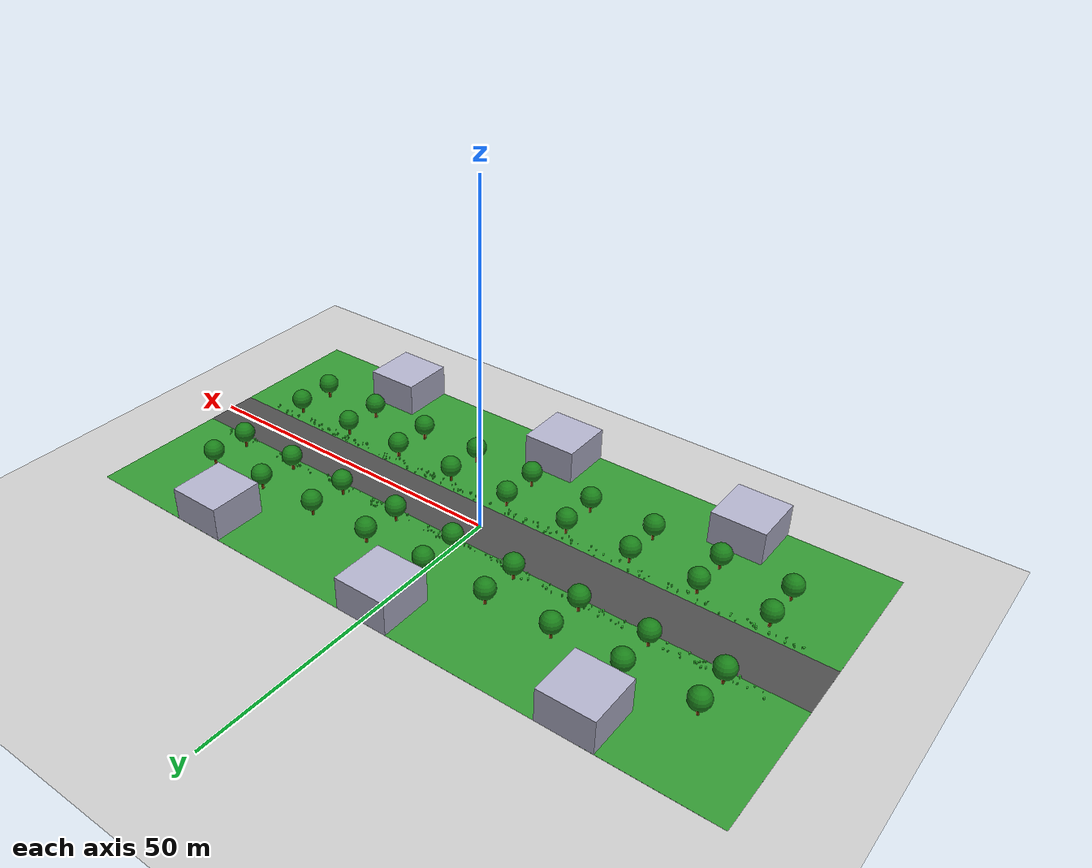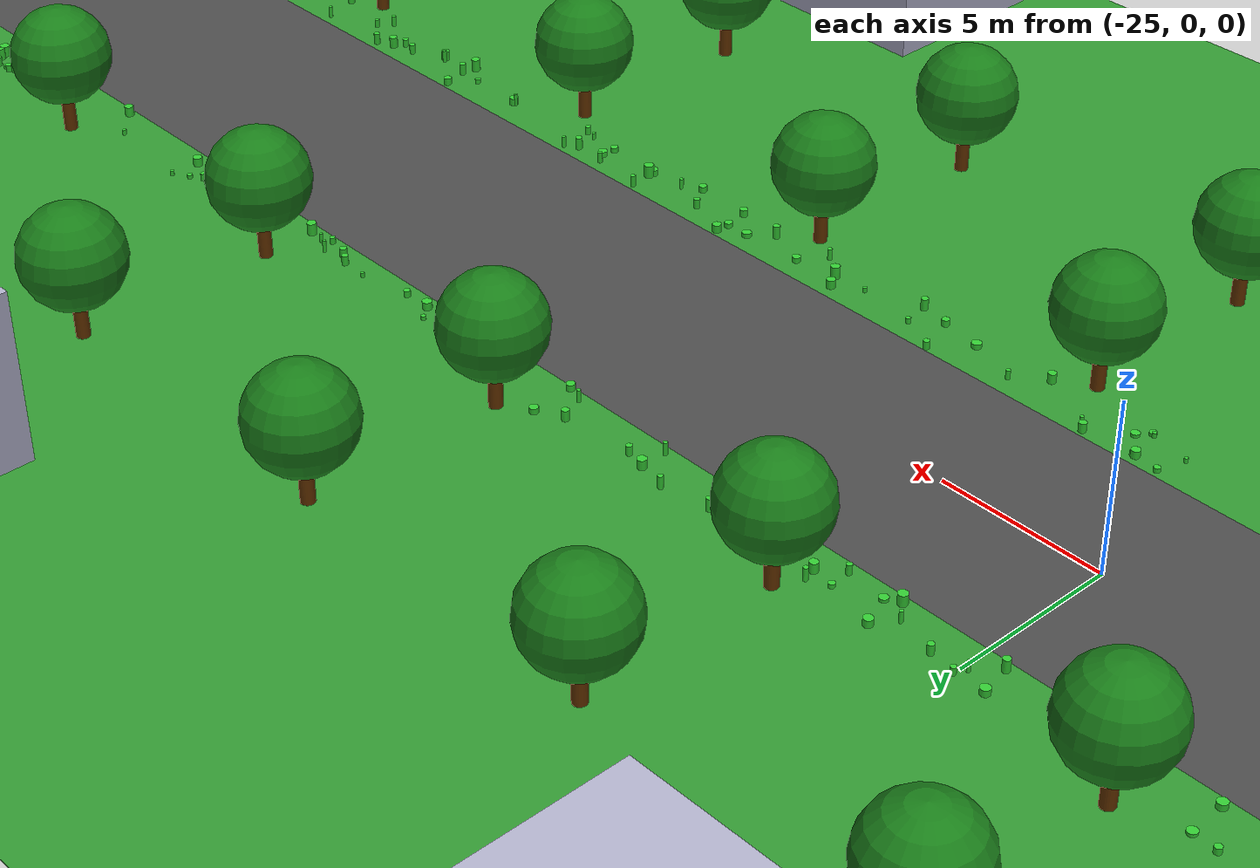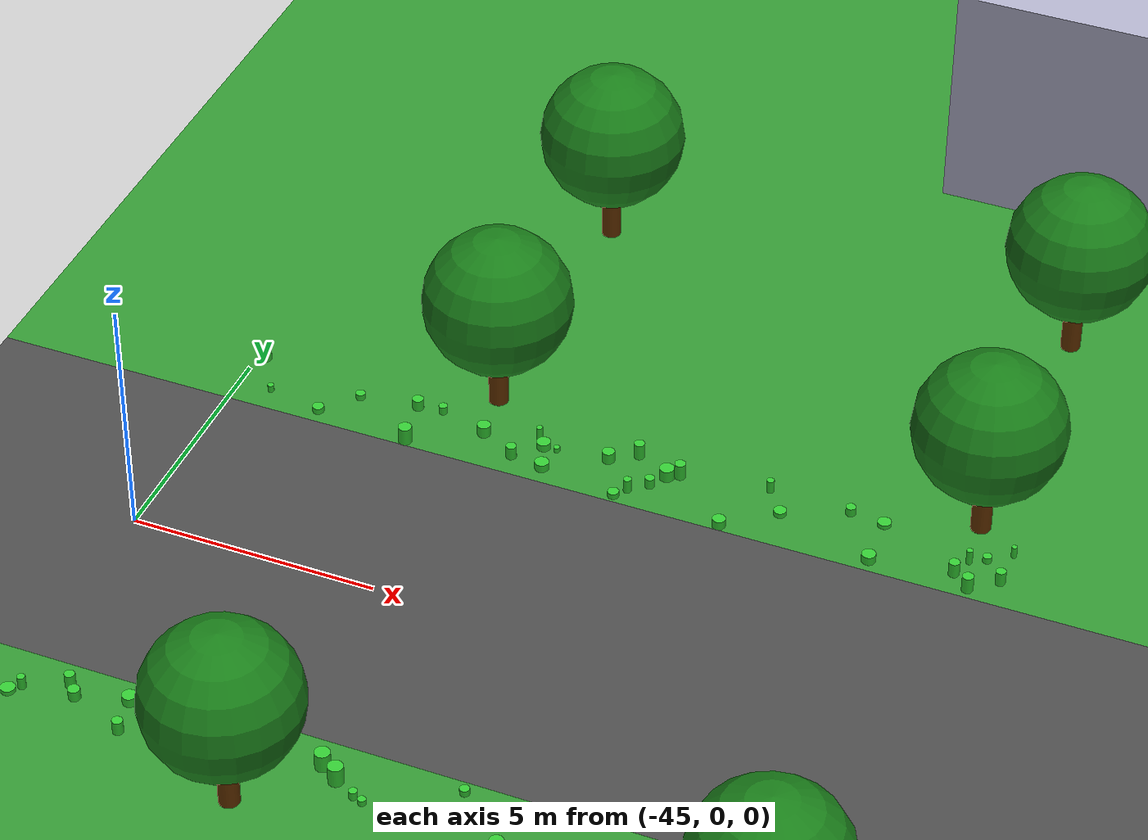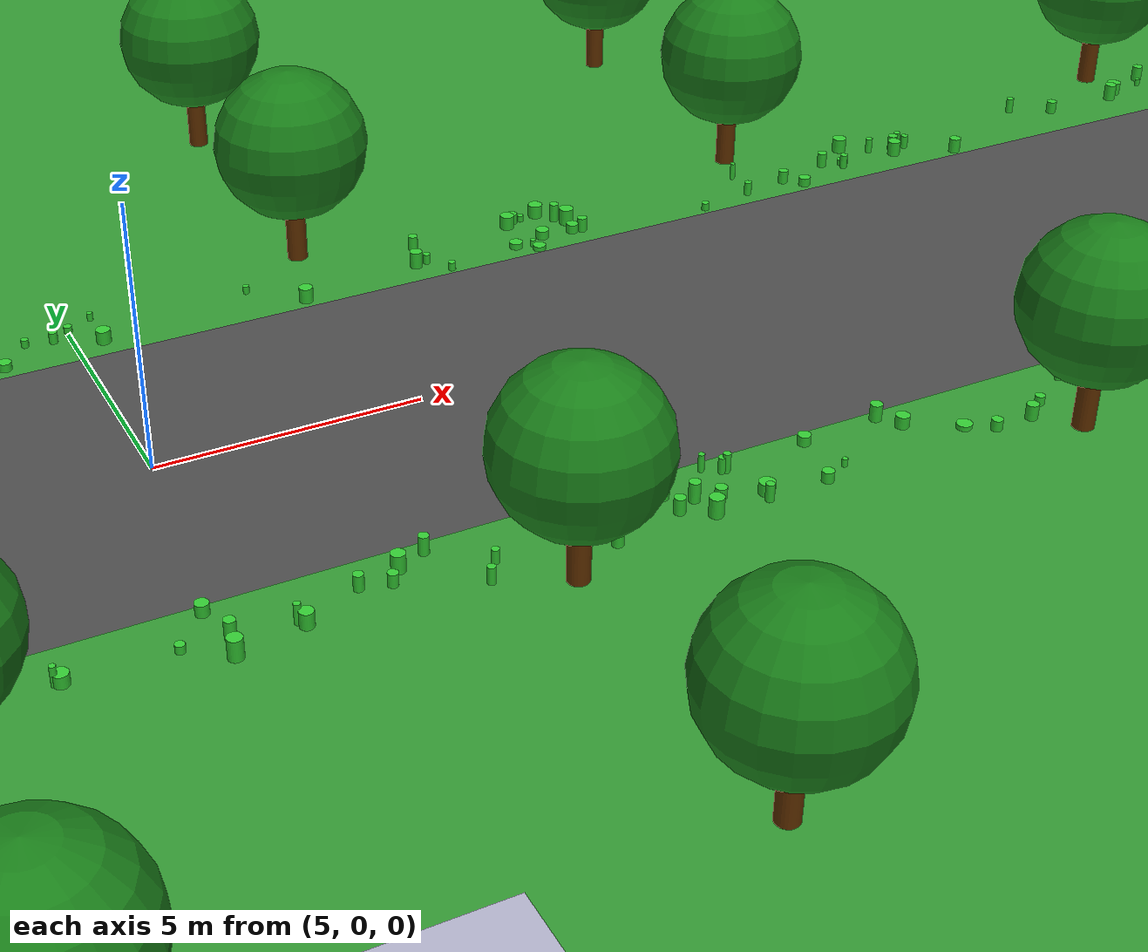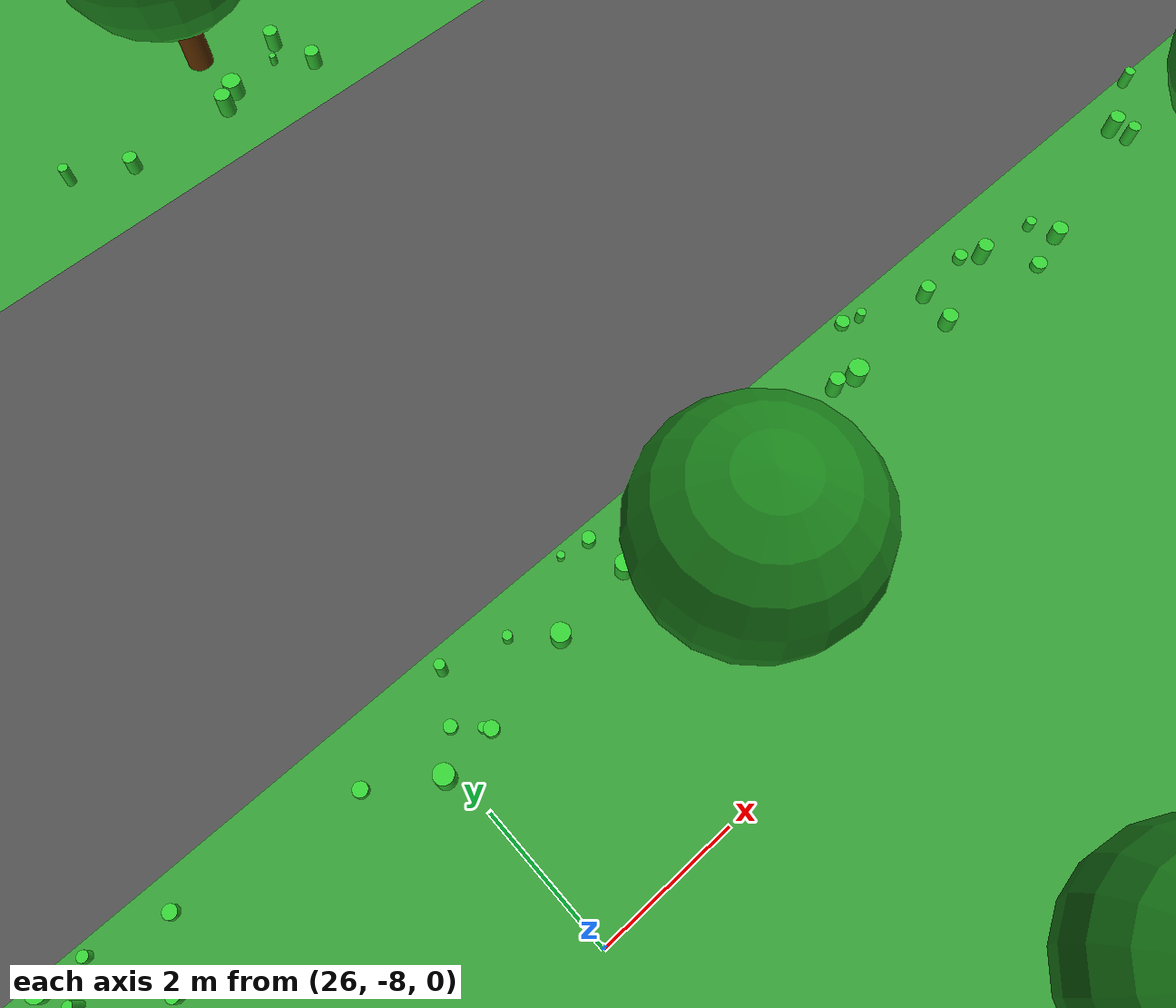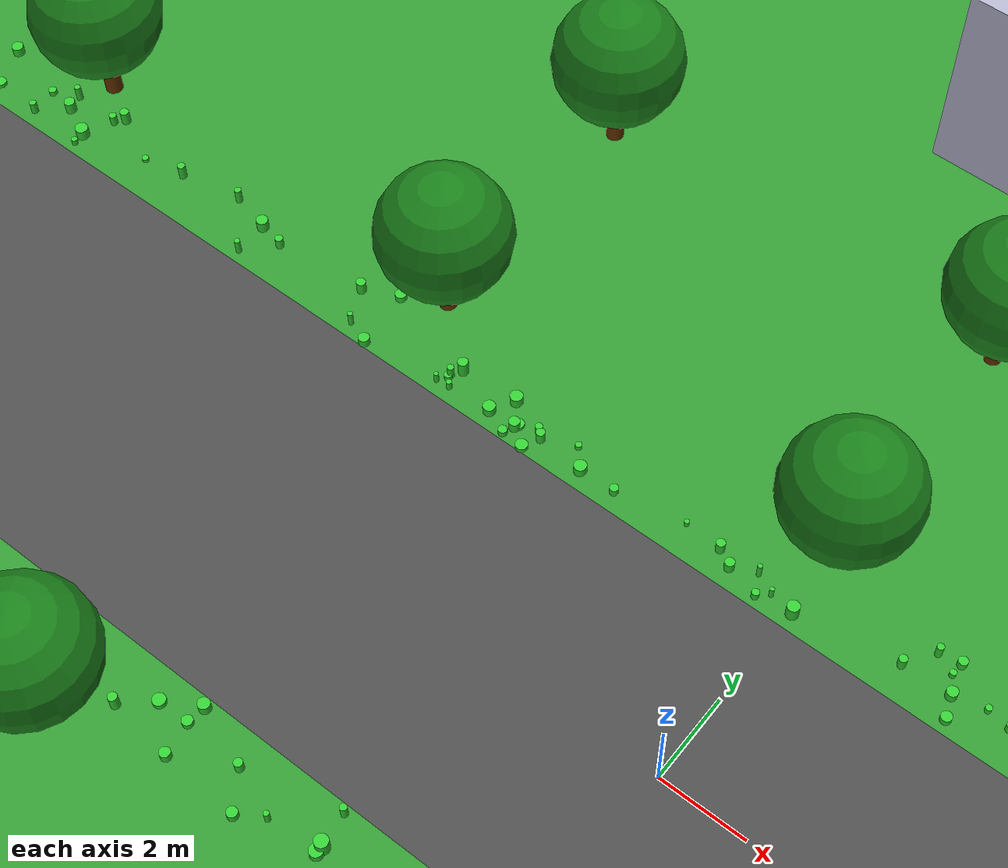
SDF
<?xml version="1.0" ?>
<sdf version="1.6">
  <world name="street_park_world">
    <include>
      <uri>model://sun</uri>
    </include>
    <include>
      <uri>model://ground_plane</uri>
    </include>

    <!-- Street -->
    <model name="street">
      <pose>0 0 0.005 0 0 0</pose>
      <static>true</static>
      <link name="link">
        <collision name="collision">
          <geometry>
            <box><size>100 8 0.01</size></box>
          </geometry>
        </collision>
        <visual name="visual">
          <geometry>
            <box><size>100 8 0.01</size></box>
          </geometry>
          <material><ambient>0.3 0.3 0.3 1</ambient></material>
        </visual>
      </link>
    </model>

    <!-- Grass North -->
    <model name="grass_north">
      <pose>0 14 0.005 0 0 0</pose>
      <static>true</static>
      <link name="link">
        <collision name="collision">
          <geometry>
            <box><size>100 20 0.01</size></box>
          </geometry>
        </collision>
        <visual name="visual">
          <geometry>
            <box><size>100 20 0.01</size></box>
          </geometry>
          <material><ambient>0.2 0.6 0.2 1</ambient></material>
        </visual>
      </link>
    </model>

    <!-- Grass South -->
    <model name="grass_south">
      <pose>0 -14 0.005 0 0 0</pose>
      <static>true</static>
      <link name="link">
        <collision name="collision">
          <geometry>
            <box><size>100 20 0.01</size></box>
          </geometry>
        </collision>
        <visual name="visual">
          <geometry>
            <box><size>100 20 0.01</size></box>
          </geometry>
          <material><ambient>0.2 0.6 0.2 1</ambient></material>
        </visual>
      </link>
    </model>

    <!-- Tree 0 -->
    <model name="tree_0">
      <pose>-40 6 0 0 0 0</pose>
      <static>true</static>
      <link name="trunk">
        <pose>0 0 1 0 0 0</pose>
        <collision name="collision">
          <geometry><cylinder><radius>0.2</radius><length>2</length></cylinder></geometry>
        </collision>
        <visual name="visual">
          <geometry><cylinder><radius>0.2</radius><length>2</length></cylinder></geometry>
          <material><ambient>0.4 0.2 0.0 1</ambient></material>
        </visual>
      </link>
      <link name="leaves">
        <pose>0 0 2.5 0 0 0</pose>
        <collision name="collision">
          <geometry><sphere><radius>1.5</radius></sphere></geometry>
        </collision>
        <visual name="visual">
          <geometry><sphere><radius>1.5</radius></sphere></geometry>
          <material><ambient>0.1 0.5 0.1 1</ambient></material>
        </visual>
      </link>
    </model>

    <!-- Tree 1 -->
    <model name="tree_1">
      <pose>-40 -6 0 0 0 0</pose>
      <static>true</static>
      <link name="trunk">
        <pose>0 0 1 0 0 0</pose>
        <collision name="collision">
          <geometry><cylinder><radius>0.2</radius><length>2</length></cylinder></geometry>
        </collision>
        <visual name="visual">
          <geometry><cylinder><radius>0.2</radius><length>2</length></cylinder></geometry>
          <material><ambient>0.4 0.2 0.0 1</ambient></material>
        </visual>
      </link>
      <link name="leaves">
        <pose>0 0 2.5 0 0 0</pose>
        <collision name="collision">
          <geometry><sphere><radius>1.5</radius></sphere></geometry>
        </collision>
        <visual name="visual">
          <geometry><sphere><radius>1.5</radius></sphere></geometry>
          <material><ambient>0.1 0.5 0.1 1</ambient></material>
        </visual>
      </link>
    </model>

    <!-- Tree 2 -->
    <model name="tree_2">
      <pose>-40 12 0 0 0 0</pose>
      <static>true</static>
      <link name="trunk">
        <pose>0 0 1 0 0 0</pose>
        <collision name="collision">
          <geometry><cylinder><radius>0.2</radius><length>2</length></cylinder></geometry>
        </collision>
        <visual name="visual">
          <geometry><cylinder><radius>0.2</radius><length>2</length></cylinder></geometry>
          <material><ambient>0.4 0.2 0.0 1</ambient></material>
        </visual>
      </link>
      <link name="leaves">
        <pose>0 0 2.5 0 0 0</pose>
        <collision name="collision">
          <geometry><sphere><radius>1.5</radius></sphere></geometry>
        </collision>
        <visual name="visual">
          <geometry><sphere><radius>1.5</radius></sphere></geometry>
          <material><ambient>0.1 0.5 0.1 1</ambient></material>
        </visual>
      </link>
    </model>

    <!-- Tree 3 -->
    <model name="tree_3">
      <pose>-40 -12 0 0 0 0</pose>
      <static>true</static>
      <link name="trunk">
        <pose>0 0 1 0 0 0</pose>
        <collision name="collision">
          <geometry><cylinder><radius>0.2</radius><length>2</length></cylinder></geometry>
        </collision>
        <visual name="visual">
          <geometry><cylinder><radius>0.2</radius><length>2</length></cylinder></geometry>
          <material><ambient>0.4 0.2 0.0 1</ambient></material>
        </visual>
      </link>
      <link name="leaves">
        <pose>0 0 2.5 0 0 0</pose>
        <collision name="collision">
          <geometry><sphere><radius>1.5</radius></sphere></geometry>
        </collision>
        <visual name="visual">
          <geometry><sphere><radius>1.5</radius></sphere></geometry>
          <material><ambient>0.1 0.5 0.1 1</ambient></material>
        </visual>
      </link>
    </model>

    <!-- Tree 4 -->
    <model name="tree_4">
      <pose>-30 6 0 0 0 0</pose>
      <static>true</static>
      <link name="trunk">
        <pose>0 0 1 0 0 0</pose>
        <collision name="collision">
          <geometry><cylinder><radius>0.2</radius><length>2</length></cylinder></geometry>
        </collision>
        <visual name="visual">
          <geometry><cylinder><radius>0.2</radius><length>2</length></cylinder></geometry>
          <material><ambient>0.4 0.2 0.0 1</ambient></material>
        </visual>
      </link>
      <link name="leaves">
        <pose>0 0 2.5 0 0 0</pose>
        <collision name="collision">
          <geometry><sphere><radius>1.5</radius></sphere></geometry>
        </collision>
        <visual name="visual">
          <geometry><sphere><radius>1.5</radius></sphere></geometry>
          <material><ambient>0.1 0.5 0.1 1</ambient></material>
        </visual>
      </link>
    </model>

    <!-- Tree 5 -->
    <model name="tree_5">
      <pose>-30 -6 0 0 0 0</pose>
      <static>true</static>
      <link name="trunk">
        <pose>0 0 1 0 0 0</pose>
        <collision name="collision">
          <geometry><cylinder><radius>0.2</radius><length>2</length></cylinder></geometry>
        </collision>
        <visual name="visual">
          <geometry><cylinder><radius>0.2</radius><length>2</length></cylinder></geometry>
          <material><ambient>0.4 0.2 0.0 1</ambient></material>
        </visual>
      </link>
      <link name="leaves">
        <pose>0 0 2.5 0 0 0</pose>
        <collision name="collision">
          <geometry><sphere><radius>1.5</radius></sphere></geometry>
        </collision>
        <visual name="visual">
          <geometry><sphere><radius>1.5</radius></sphere></geometry>
          <material><ambient>0.1 0.5 0.1 1</ambient></material>
        </visual>
      </link>
    </model>

    <!-- Tree 6 -->
    <model name="tree_6">
      <pose>-30 12 0 0 0 0</pose>
      <static>true</static>
      <link name="trunk">
        <pose>0 0 1 0 0 0</pose>
        <collision name="collision">
          <geometry><cylinder><radius>0.2</radius><length>2</length></cylinder></geometry>
        </collision>
        <visual name="visual">
          <geometry><cylinder><radius>0.2</radius><length>2</length></cylinder></geometry>
          <material><ambient>0.4 0.2 0.0 1</ambient></material>
        </visual>
      </link>
      <link name="leaves">
        <pose>0 0 2.5 0 0 0</pose>
        <collision name="collision">
          <geometry><sphere><radius>1.5</radius></sphere></geometry>
        </collision>
        <visual name="visual">
          <geometry><sphere><radius>1.5</radius></sphere></geometry>
          <material><ambient>0.1 0.5 0.1 1</ambient></material>
        </visual>
      </link>
    </model>

    <!-- Tree 7 -->
    <model name="tree_7">
      <pose>-30 -12 0 0 0 0</pose>
      <static>true</static>
      <link name="trunk">
        <pose>0 0 1 0 0 0</pose>
        <collision name="collision">
          <geometry><cylinder><radius>0.2</radius><length>2</length></cylinder></geometry>
        </collision>
        <visual name="visual">
          <geometry><cylinder><radius>0.2</radius><length>2</length></cylinder></geometry>
          <material><ambient>0.4 0.2 0.0 1</ambient></material>
        </visual>
      </link>
      <link name="leaves">
        <pose>0 0 2.5 0 0 0</pose>
        <collision name="collision">
          <geometry><sphere><radius>1.5</radius></sphere></geometry>
        </collision>
        <visual name="visual">
          <geometry><sphere><radius>1.5</radius></sphere></geometry>
          <material><ambient>0.1 0.5 0.1 1</ambient></material>
        </visual>
      </link>
    </model>

    <!-- Tree 8 -->
    <model name="tree_8">
      <pose>-20 6 0 0 0 0</pose>
      <static>true</static>
      <link name="trunk">
        <pose>0 0 1 0 0 0</pose>
        <collision name="collision">
          <geometry><cylinder><radius>0.2</radius><length>2</length></cylinder></geometry>
        </collision>
        <visual name="visual">
          <geometry><cylinder><radius>0.2</radius><length>2</length></cylinder></geometry>
          <material><ambient>0.4 0.2 0.0 1</ambient></material>
        </visual>
      </link>
      <link name="leaves">
        <pose>0 0 2.5 0 0 0</pose>
        <collision name="collision">
          <geometry><sphere><radius>1.5</radius></sphere></geometry>
        </collision>
        <visual name="visual">
          <geometry><sphere><radius>1.5</radius></sphere></geometry>
          <material><ambient>0.1 0.5 0.1 1</ambient></material>
        </visual>
      </link>
    </model>

    <!-- Tree 9 -->
    <model name="tree_9">
      <pose>-20 -6 0 0 0 0</pose>
      <static>true</static>
      <link name="trunk">
        <pose>0 0 1 0 0 0</pose>
        <collision name="collision">
          <geometry><cylinder><radius>0.2</radius><length>2</length></cylinder></geometry>
        </collision>
        <visual name="visual">
          <geometry><cylinder><radius>0.2</radius><length>2</length></cylinder></geometry>
          <material><ambient>0.4 0.2 0.0 1</ambient></material>
        </visual>
      </link>
      <link name="leaves">
        <pose>0 0 2.5 0 0 0</pose>
        <collision name="collision">
          <geometry><sphere><radius>1.5</radius></sphere></geometry>
        </collision>
        <visual name="visual">
          <geometry><sphere><radius>1.5</radius></sphere></geometry>
          <material><ambient>0.1 0.5 0.1 1</ambient></material>
        </visual>
      </link>
    </model>

    <!-- Tree 10 -->
    <model name="tree_10">
      <pose>-20 12 0 0 0 0</pose>
      <static>true</static>
      <link name="trunk">
        <pose>0 0 1 0 0 0</pose>
        <collision name="collision">
          <geometry><cylinder><radius>0.2</radius><length>2</length></cylinder></geometry>
        </collision>
        <visual name="visual">
          <geometry><cylinder><radius>0.2</radius><length>2</length></cylinder></geometry>
          <material><ambient>0.4 0.2 0.0 1</ambient></material>
        </visual>
      </link>
      <link name="leaves">
        <pose>0 0 2.5 0 0 0</pose>
        <collision name="collision">
          <geometry><sphere><radius>1.5</radius></sphere></geometry>
        </collision>
        <visual name="visual">
          <geometry><sphere><radius>1.5</radius></sphere></geometry>
          <material><ambient>0.1 0.5 0.1 1</ambient></material>
        </visual>
      </link>
    </model>

    <!-- Tree 11 -->
    <model name="tree_11">
      <pose>-20 -12 0 0 0 0</pose>
      <static>true</static>
      <link name="trunk">
        <pose>0 0 1 0 0 0</pose>
        <collision name="collision">
          <geometry><cylinder><radius>0.2</radius><length>2</length></cylinder></geometry>
        </collision>
        <visual name="visual">
          <geometry><cylinder><radius>0.2</radius><length>2</length></cylinder></geometry>
          <material><ambient>0.4 0.2 0.0 1</ambient></material>
        </visual>
      </link>
      <link name="leaves">
        <pose>0 0 2.5 0 0 0</pose>
        <collision name="collision">
          <geometry><sphere><radius>1.5</radius></sphere></geometry>
        </collision>
        <visual name="visual">
          <geometry><sphere><radius>1.5</radius></sphere></geometry>
          <material><ambient>0.1 0.5 0.1 1</ambient></material>
        </visual>
      </link>
    </model>

    <!-- Tree 12 -->
    <model name="tree_12">
      <pose>-10 6 0 0 0 0</pose>
      <static>true</static>
      <link name="trunk">
        <pose>0 0 1 0 0 0</pose>
        <collision name="collision">
          <geometry><cylinder><radius>0.2</radius><length>2</length></cylinder></geometry>
        </collision>
        <visual name="visual">
          <geometry><cylinder><radius>0.2</radius><length>2</length></cylinder></geometry>
          <material><ambient>0.4 0.2 0.0 1</ambient></material>
        </visual>
      </link>
      <link name="leaves">
        <pose>0 0 2.5 0 0 0</pose>
        <collision name="collision">
          <geometry><sphere><radius>1.5</radius></sphere></geometry>
        </collision>
        <visual name="visual">
          <geometry><sphere><radius>1.5</radius></sphere></geometry>
          <material><ambient>0.1 0.5 0.1 1</ambient></material>
        </visual>
      </link>
    </model>

    <!-- Tree 13 -->
    <model name="tree_13">
      <pose>-10 -6 0 0 0 0</pose>
      <static>true</static>
      <link name="trunk">
        <pose>0 0 1 0 0 0</pose>
        <collision name="collision">
          <geometry><cylinder><radius>0.2</radius><length>2</length></cylinder></geometry>
        </collision>
        <visual name="visual">
          <geometry><cylinder><radius>0.2</radius><length>2</length></cylinder></geometry>
          <material><ambient>0.4 0.2 0.0 1</ambient></material>
        </visual>
      </link>
      <link name="leaves">
        <pose>0 0 2.5 0 0 0</pose>
        <collision name="collision">
          <geometry><sphere><radius>1.5</radius></sphere></geometry>
        </collision>
        <visual name="visual">
          <geometry><sphere><radius>1.5</radius></sphere></geometry>
          <material><ambient>0.1 0.5 0.1 1</ambient></material>
        </visual>
      </link>
    </model>

    <!-- Tree 14 -->
    <model name="tree_14">
      <pose>-10 12 0 0 0 0</pose>
      <static>true</static>
      <link name="trunk">
        <pose>0 0 1 0 0 0</pose>
        <collision name="collision">
          <geometry><cylinder><radius>0.2</radius><length>2</length></cylinder></geometry>
        </collision>
        <visual name="visual">
          <geometry><cylinder><radius>0.2</radius><length>2</length></cylinder></geometry>
          <material><ambient>0.4 0.2 0.0 1</ambient></material>
        </visual>
      </link>
      <link name="leaves">
        <pose>0 0 2.5 0 0 0</pose>
        <collision name="collision">
          <geometry><sphere><radius>1.5</radius></sphere></geometry>
        </collision>
        <visual name="visual">
          <geometry><sphere><radius>1.5</radius></sphere></geometry>
          <material><ambient>0.1 0.5 0.1 1</ambient></material>
        </visual>
      </link>
    </model>

    <!-- Tree 15 -->
    <model name="tree_15">
      <pose>-10 -12 0 0 0 0</pose>
      <static>true</static>
      <link name="trunk">
        <pose>0 0 1 0 0 0</pose>
        <collision name="collision">
          <geometry><cylinder><radius>0.2</radius><length>2</length></cylinder></geometry>
        </collision>
        <visual name="visual">
          <geometry><cylinder><radius>0.2</radius><length>2</length></cylinder></geometry>
          <material><ambient>0.4 0.2 0.0 1</ambient></material>
        </visual>
      </link>
      <link name="leaves">
        <pose>0 0 2.5 0 0 0</pose>
        <collision name="collision">
          <geometry><sphere><radius>1.5</radius></sphere></geometry>
        </collision>
        <visual name="visual">
          <geometry><sphere><radius>1.5</radius></sphere></geometry>
          <material><ambient>0.1 0.5 0.1 1</ambient></material>
        </visual>
      </link>
    </model>

    <!-- Tree 16 -->
    <model name="tree_16">
      <pose>0 6 0 0 0 0</pose>
      <static>true</static>
      <link name="trunk">
        <pose>0 0 1 0 0 0</pose>
        <collision name="collision">
          <geometry><cylinder><radius>0.2</radius><length>2</length></cylinder></geometry>
        </collision>
        <visual name="visual">
          <geometry><cylinder><radius>0.2</radius><length>2</length></cylinder></geometry>
          <material><ambient>0.4 0.2 0.0 1</ambient></material>
        </visual>
      </link>
      <link name="leaves">
        <pose>0 0 2.5 0 0 0</pose>
        <collision name="collision">
          <geometry><sphere><radius>1.5</radius></sphere></geometry>
        </collision>
        <visual name="visual">
          <geometry><sphere><radius>1.5</radius></sphere></geometry>
          <material><ambient>0.1 0.5 0.1 1</ambient></material>
        </visual>
      </link>
    </model>

    <!-- Tree 17 -->
    <model name="tree_17">
      <pose>0 -6 0 0 0 0</pose>
      <static>true</static>
      <link name="trunk">
        <pose>0 0 1 0 0 0</pose>
        <collision name="collision">
          <geometry><cylinder><radius>0.2</radius><length>2</length></cylinder></geometry>
        </collision>
        <visual name="visual">
          <geometry><cylinder><radius>0.2</radius><length>2</length></cylinder></geometry>
          <material><ambient>0.4 0.2 0.0 1</ambient></material>
        </visual>
      </link>
      <link name="leaves">
        <pose>0 0 2.5 0 0 0</pose>
        <collision name="collision">
          <geometry><sphere><radius>1.5</radius></sphere></geometry>
        </collision>
        <visual name="visual">
          <geometry><sphere><radius>1.5</radius></sphere></geometry>
          <material><ambient>0.1 0.5 0.1 1</ambient></material>
        </visual>
      </link>
    </model>

    <!-- Tree 18 -->
    <model name="tree_18">
      <pose>0 12 0 0 0 0</pose>
      <static>true</static>
      <link name="trunk">
        <pose>0 0 1 0 0 0</pose>
        <collision name="collision">
          <geometry><cylinder><radius>0.2</radius><length>2</length></cylinder></geometry>
        </collision>
        <visual name="visual">
          <geometry><cylinder><radius>0.2</radius><length>2</length></cylinder></geometry>
          <material><ambient>0.4 0.2 0.0 1</ambient></material>
        </visual>
      </link>
      <link name="leaves">
        <pose>0 0 2.5 0 0 0</pose>
        <collision name="collision">
          <geometry><sphere><radius>1.5</radius></sphere></geometry>
        </collision>
        <visual name="visual">
          <geometry><sphere><radius>1.5</radius></sphere></geometry>
          <material><ambient>0.1 0.5 0.1 1</ambient></material>
        </visual>
      </link>
    </model>

    <!-- Tree 19 -->
    <model name="tree_19">
      <pose>0 -12 0 0 0 0</pose>
      <static>true</static>
      <link name="trunk">
        <pose>0 0 1 0 0 0</pose>
        <collision name="collision">
          <geometry><cylinder><radius>0.2</radius><length>2</length></cylinder></geometry>
        </collision>
        <visual name="visual">
          <geometry><cylinder><radius>0.2</radius><length>2</length></cylinder></geometry>
          <material><ambient>0.4 0.2 0.0 1</ambient></material>
        </visual>
      </link>
      <link name="leaves">
        <pose>0 0 2.5 0 0 0</pose>
        <collision name="collision">
          <geometry><sphere><radius>1.5</radius></sphere></geometry>
        </collision>
        <visual name="visual">
          <geometry><sphere><radius>1.5</radius></sphere></geometry>
          <material><ambient>0.1 0.5 0.1 1</ambient></material>
        </visual>
      </link>
    </model>

    <!-- Tree 20 -->
    <model name="tree_20">
      <pose>10 6 0 0 0 0</pose>
      <static>true</static>
      <link name="trunk">
        <pose>0 0 1 0 0 0</pose>
        <collision name="collision">
          <geometry><cylinder><radius>0.2</radius><length>2</length></cylinder></geometry>
        </collision>
        <visual name="visual">
          <geometry><cylinder><radius>0.2</radius><length>2</length></cylinder></geometry>
          <material><ambient>0.4 0.2 0.0 1</ambient></material>
        </visual>
      </link>
      <link name="leaves">
        <pose>0 0 2.5 0 0 0</pose>
        <collision name="collision">
          <geometry><sphere><radius>1.5</radius></sphere></geometry>
        </collision>
        <visual name="visual">
          <geometry><sphere><radius>1.5</radius></sphere></geometry>
          <material><ambient>0.1 0.5 0.1 1</ambient></material>
        </visual>
      </link>
    </model>

    <!-- Tree 21 -->
    <model name="tree_21">
      <pose>10 -6 0 0 0 0</pose>
      <static>true</static>
      <link name="trunk">
        <pose>0 0 1 0 0 0</pose>
        <collision name="collision">
          <geometry><cylinder><radius>0.2</radius><length>2</length></cylinder></geometry>
        </collision>
        <visual name="visual">
          <geometry><cylinder><radius>0.2</radius><length>2</length></cylinder></geometry>
          <material><ambient>0.4 0.2 0.0 1</ambient></material>
        </visual>
      </link>
      <link name="leaves">
        <pose>0 0 2.5 0 0 0</pose>
        <collision name="collision">
          <geometry><sphere><radius>1.5</radius></sphere></geometry>
        </collision>
        <visual name="visual">
          <geometry><sphere><radius>1.5</radius></sphere></geometry>
          <material><ambient>0.1 0.5 0.1 1</ambient></material>
        </visual>
      </link>
    </model>

    <!-- Tree 22 -->
    <model name="tree_22">
      <pose>10 12 0 0 0 0</pose>
      <static>true</static>
      <link name="trunk">
        <pose>0 0 1 0 0 0</pose>
        <collision name="collision">
          <geometry><cylinder><radius>0.2</radius><length>2</length></cylinder></geometry>
        </collision>
        <visual name="visual">
          <geometry><cylinder><radius>0.2</radius><length>2</length></cylinder></geometry>
          <material><ambient>0.4 0.2 0.0 1</ambient></material>
        </visual>
      </link>
      <link name="leaves">
        <pose>0 0 2.5 0 0 0</pose>
        <collision name="collision">
          <geometry><sphere><radius>1.5</radius></sphere></geometry>
        </collision>
        <visual name="visual">
          <geometry><sphere><radius>1.5</radius></sphere></geometry>
          <material><ambient>0.1 0.5 0.1 1</ambient></material>
        </visual>
      </link>
    </model>

    <!-- Tree 23 -->
    <model name="tree_23">
      <pose>10 -12 0 0 0 0</pose>
      <static>true</static>
      <link name="trunk">
        <pose>0 0 1 0 0 0</pose>
        <collision name="collision">
          <geometry><cylinder><radius>0.2</radius><length>2</length></cylinder></geometry>
        </collision>
        <visual name="visual">
          <geometry><cylinder><radius>0.2</radius><length>2</length></cylinder></geometry>
          <material><ambient>0.4 0.2 0.0 1</ambient></material>
        </visual>
      </link>
      <link name="leaves">
        <pose>0 0 2.5 0 0 0</pose>
        <collision name="collision">
          <geometry><sphere><radius>1.5</radius></sphere></geometry>
        </collision>
        <visual name="visual">
          <geometry><sphere><radius>1.5</radius></sphere></geometry>
          <material><ambient>0.1 0.5 0.1 1</ambient></material>
        </visual>
      </link>
    </model>

    <!-- Tree 24 -->
    <model name="tree_24">
      <pose>20 6 0 0 0 0</pose>
      <static>true</static>
      <link name="trunk">
        <pose>0 0 1 0 0 0</pose>
        <collision name="collision">
          <geometry><cylinder><radius>0.2</radius><length>2</length></cylinder></geometry>
        </collision>
        <visual name="visual">
          <geometry><cylinder><radius>0.2</radius><length>2</length></cylinder></geometry>
          <material><ambient>0.4 0.2 0.0 1</ambient></material>
        </visual>
      </link>
      <link name="leaves">
        <pose>0 0 2.5 0 0 0</pose>
        <collision name="collision">
          <geometry><sphere><radius>1.5</radius></sphere></geometry>
        </collision>
        <visual name="visual">
          <geometry><sphere><radius>1.5</radius></sphere></geometry>
          <material><ambient>0.1 0.5 0.1 1</ambient></material>
        </visual>
      </link>
    </model>

    <!-- Tree 25 -->
    <model name="tree_25">
      <pose>20 -6 0 0 0 0</pose>
      <static>true</static>
      <link name="trunk">
        <pose>0 0 1 0 0 0</pose>
        <collision name="collision">
          <geometry><cylinder><radius>0.2</radius><length>2</length></cylinder></geometry>
        </collision>
        <visual name="visual">
          <geometry><cylinder><radius>0.2</radius><length>2</length></cylinder></geometry>
          <material><ambient>0.4 0.2 0.0 1</ambient></material>
        </visual>
      </link>
      <link name="leaves">
        <pose>0 0 2.5 0 0 0</pose>
        <collision name="collision">
          <geometry><sphere><radius>1.5</radius></sphere></geometry>
        </collision>
        <visual name="visual">
          <geometry><sphere><radius>1.5</radius></sphere></geometry>
          <material><ambient>0.1 0.5 0.1 1</ambient></material>
        </visual>
      </link>
    </model>

    <!-- Tree 26 -->
    <model name="tree_26">
      <pose>20 12 0 0 0 0</pose>
      <static>true</static>
      <link name="trunk">
        <pose>0 0 1 0 0 0</pose>
        <collision name="collision">
          <geometry><cylinder><radius>0.2</radius><length>2</length></cylinder></geometry>
        </collision>
        <visual name="visual">
          <geometry><cylinder><radius>0.2</radius><length>2</length></cylinder></geometry>
          <material><ambient>0.4 0.2 0.0 1</ambient></material>
        </visual>
      </link>
      <link name="leaves">
        <pose>0 0 2.5 0 0 0</pose>
        <collision name="collision">
          <geometry><sphere><radius>1.5</radius></sphere></geometry>
        </collision>
        <visual name="visual">
          <geometry><sphere><radius>1.5</radius></sphere></geometry>
          <material><ambient>0.1 0.5 0.1 1</ambient></material>
        </visual>
      </link>
    </model>

    <!-- Tree 27 -->
    <model name="tree_27">
      <pose>20 -12 0 0 0 0</pose>
      <static>true</static>
      <link name="trunk">
        <pose>0 0 1 0 0 0</pose>
        <collision name="collision">
          <geometry><cylinder><radius>0.2</radius><length>2</length></cylinder></geometry>
        </collision>
        <visual name="visual">
          <geometry><cylinder><radius>0.2</radius><length>2</length></cylinder></geometry>
          <material><ambient>0.4 0.2 0.0 1</ambient></material>
        </visual>
      </link>
      <link name="leaves">
        <pose>0 0 2.5 0 0 0</pose>
        <collision name="collision">
          <geometry><sphere><radius>1.5</radius></sphere></geometry>
        </collision>
        <visual name="visual">
          <geometry><sphere><radius>1.5</radius></sphere></geometry>
          <material><ambient>0.1 0.5 0.1 1</ambient></material>
        </visual>
      </link>
    </model>

    <!-- Tree 28 -->
    <model name="tree_28">
      <pose>30 6 0 0 0 0</pose>
      <static>true</static>
      <link name="trunk">
        <pose>0 0 1 0 0 0</pose>
        <collision name="collision">
          <geometry><cylinder><radius>0.2</radius><length>2</length></cylinder></geometry>
        </collision>
        <visual name="visual">
          <geometry><cylinder><radius>0.2</radius><length>2</length></cylinder></geometry>
          <material><ambient>0.4 0.2 0.0 1</ambient></material>
        </visual>
      </link>
      <link name="leaves">
        <pose>0 0 2.5 0 0 0</pose>
        <collision name="collision">
          <geometry><sphere><radius>1.5</radius></sphere></geometry>
        </collision>
        <visual name="visual">
          <geometry><sphere><radius>1.5</radius></sphere></geometry>
          <material><ambient>0.1 0.5 0.1 1</ambient></material>
        </visual>
      </link>
    </model>

    <!-- Tree 29 -->
    <model name="tree_29">
      <pose>30 -6 0 0 0 0</pose>
      <static>true</static>
      <link name="trunk">
        <pose>0 0 1 0 0 0</pose>
        <collision name="collision">
          <geometry><cylinder><radius>0.2</radius><length>2</length></cylinder></geometry>
        </collision>
        <visual name="visual">
          <geometry><cylinder><radius>0.2</radius><length>2</length></cylinder></geometry>
          <material><ambient>0.4 0.2 0.0 1</ambient></material>
        </visual>
      </link>
      <link name="leaves">
        <pose>0 0 2.5 0 0 0</pose>
        <collision name="collision">
          <geometry><sphere><radius>1.5</radius></sphere></geometry>
        </collision>
        <visual name="visual">
          <geometry><sphere><radius>1.5</radius></sphere></geometry>
          <material><ambient>0.1 0.5 0.1 1</ambient></material>
        </visual>
      </link>
    </model>

    <!-- Tree 30 -->
    <model name="tree_30">
      <pose>30 12 0 0 0 0</pose>
      <static>true</static>
      <link name="trunk">
        <pose>0 0 1 0 0 0</pose>
        <collision name="collision">
          <geometry><cylinder><radius>0.2</radius><length>2</length></cylinder></geometry>
        </collision>
        <visual name="visual">
          <geometry><cylinder><radius>0.2</radius><length>2</length></cylinder></geometry>
          <material><ambient>0.4 0.2 0.0 1</ambient></material>
        </visual>
      </link>
      <link name="leaves">
        <pose>0 0 2.5 0 0 0</pose>
        <collision name="collision">
          <geometry><sphere><radius>1.5</radius></sphere></geometry>
        </collision>
        <visual name="visual">
          <geometry><sphere><radius>1.5</radius></sphere></geometry>
          <material><ambient>0.1 0.5 0.1 1</ambient></material>
        </visual>
      </link>
    </model>

    <!-- Tree 31 -->
    <model name="tree_31">
      <pose>30 -12 0 0 0 0</pose>
      <static>true</static>
      <link name="trunk">
        <pose>0 0 1 0 0 0</pose>
        <collision name="collision">
          <geometry><cylinder><radius>0.2</radius><length>2</length></cylinder></geometry>
        </collision>
        <visual name="visual">
          <geometry><cylinder><radius>0.2</radius><length>2</length></cylinder></geometry>
          <material><ambient>0.4 0.2 0.0 1</ambient></material>
        </visual>
      </link>
      <link name="leaves">
        <pose>0 0 2.5 0 0 0</pose>
        <collision name="collision">
          <geometry><sphere><radius>1.5</radius></sphere></geometry>
        </collision>
        <visual name="visual">
          <geometry><sphere><radius>1.5</radius></sphere></geometry>
          <material><ambient>0.1 0.5 0.1 1</ambient></material>
        </visual>
      </link>
    </model>

    <!-- Tree 32 -->
    <model name="tree_32">
      <pose>40 6 0 0 0 0</pose>
      <static>true</static>
      <link name="trunk">
        <pose>0 0 1 0 0 0</pose>
        <collision name="collision">
          <geometry><cylinder><radius>0.2</radius><length>2</length></cylinder></geometry>
        </collision>
        <visual name="visual">
          <geometry><cylinder><radius>0.2</radius><length>2</length></cylinder></geometry>
          <material><ambient>0.4 0.2 0.0 1</ambient></material>
        </visual>
      </link>
      <link name="leaves">
        <pose>0 0 2.5 0 0 0</pose>
        <collision name="collision">
          <geometry><sphere><radius>1.5</radius></sphere></geometry>
        </collision>
        <visual name="visual">
          <geometry><sphere><radius>1.5</radius></sphere></geometry>
          <material><ambient>0.1 0.5 0.1 1</ambient></material>
        </visual>
      </link>
    </model>

    <!-- Tree 33 -->
    <model name="tree_33">
      <pose>40 -6 0 0 0 0</pose>
      <static>true</static>
      <link name="trunk">
        <pose>0 0 1 0 0 0</pose>
        <collision name="collision">
          <geometry><cylinder><radius>0.2</radius><length>2</length></cylinder></geometry>
        </collision>
        <visual name="visual">
          <geometry><cylinder><radius>0.2</radius><length>2</length></cylinder></geometry>
          <material><ambient>0.4 0.2 0.0 1</ambient></material>
        </visual>
      </link>
      <link name="leaves">
        <pose>0 0 2.5 0 0 0</pose>
        <collision name="collision">
          <geometry><sphere><radius>1.5</radius></sphere></geometry>
        </collision>
        <visual name="visual">
          <geometry><sphere><radius>1.5</radius></sphere></geometry>
          <material><ambient>0.1 0.5 0.1 1</ambient></material>
        </visual>
      </link>
    </model>

    <!-- Tree 34 -->
    <model name="tree_34">
      <pose>40 12 0 0 0 0</pose>
      <static>true</static>
      <link name="trunk">
        <pose>0 0 1 0 0 0</pose>
        <collision name="collision">
          <geometry><cylinder><radius>0.2</radius><length>2</length></cylinder></geometry>
        </collision>
        <visual name="visual">
          <geometry><cylinder><radius>0.2</radius><length>2</length></cylinder></geometry>
          <material><ambient>0.4 0.2 0.0 1</ambient></material>
        </visual>
      </link>
      <link name="leaves">
        <pose>0 0 2.5 0 0 0</pose>
        <collision name="collision">
          <geometry><sphere><radius>1.5</radius></sphere></geometry>
        </collision>
        <visual name="visual">
          <geometry><sphere><radius>1.5</radius></sphere></geometry>
          <material><ambient>0.1 0.5 0.1 1</ambient></material>
        </visual>
      </link>
    </model>

    <!-- Tree 35 -->
    <model name="tree_35">
      <pose>40 -12 0 0 0 0</pose>
      <static>true</static>
      <link name="trunk">
        <pose>0 0 1 0 0 0</pose>
        <collision name="collision">
          <geometry><cylinder><radius>0.2</radius><length>2</length></cylinder></geometry>
        </collision>
        <visual name="visual">
          <geometry><cylinder><radius>0.2</radius><length>2</length></cylinder></geometry>
          <material><ambient>0.4 0.2 0.0 1</ambient></material>
        </visual>
      </link>
      <link name="leaves">
        <pose>0 0 2.5 0 0 0</pose>
        <collision name="collision">
          <geometry><sphere><radius>1.5</radius></sphere></geometry>
        </collision>
        <visual name="visual">
          <geometry><sphere><radius>1.5</radius></sphere></geometry>
          <material><ambient>0.1 0.5 0.1 1</ambient></material>
        </visual>
      </link>
    </model>

    <!-- Building 0 -->
    <model name="building_0">
      <pose>-30 20 2.5 0 0 0</pose>
      <static>true</static>
      <link name="link">
        <collision name="collision">
          <geometry><box><size>8 8 5</size></box></geometry>
        </collision>
        <visual name="visual">
          <geometry><box><size>8 8 5</size></box></geometry>
          <material><ambient>0.7 0.7 0.8 1</ambient></material>
        </visual>
      </link>
    </model>

    <!-- Building 1 -->
    <model name="building_1">
      <pose>-30 -20 2.5 0 0 0</pose>
      <static>true</static>
      <link name="link">
        <collision name="collision">
          <geometry><box><size>8 8 5</size></box></geometry>
        </collision>
        <visual name="visual">
          <geometry><box><size>8 8 5</size></box></geometry>
          <material><ambient>0.7 0.7 0.8 1</ambient></material>
        </visual>
      </link>
    </model>

    <!-- Building 2 -->
    <model name="building_2">
      <pose>0 20 2.5 0 0 0</pose>
      <static>true</static>
      <link name="link">
        <collision name="collision">
          <geometry><box><size>8 8 5</size></box></geometry>
        </collision>
        <visual name="visual">
          <geometry><box><size>8 8 5</size></box></geometry>
          <material><ambient>0.7 0.7 0.8 1</ambient></material>
        </visual>
      </link>
    </model>

    <!-- Building 3 -->
    <model name="building_3">
      <pose>0 -20 2.5 0 0 0</pose>
      <static>true</static>
      <link name="link">
        <collision name="collision">
          <geometry><box><size>8 8 5</size></box></geometry>
        </collision>
        <visual name="visual">
          <geometry><box><size>8 8 5</size></box></geometry>
          <material><ambient>0.7 0.7 0.8 1</ambient></material>
        </visual>
      </link>
    </model>

    <!-- Building 4 -->
    <model name="building_4">
      <pose>30 20 2.5 0 0 0</pose>
      <static>true</static>
      <link name="link">
        <collision name="collision">
          <geometry><box><size>8 8 5</size></box></geometry>
        </collision>
        <visual name="visual">
          <geometry><box><size>8 8 5</size></box></geometry>
          <material><ambient>0.7 0.7 0.8 1</ambient></material>
        </visual>
      </link>
    </model>

    <!-- Building 5 -->
    <model name="building_5">
      <pose>30 -20 2.5 0 0 0</pose>
      <static>true</static>
      <link name="link">
        <collision name="collision">
          <geometry><box><size>8 8 5</size></box></geometry>
        </collision>
        <visual name="visual">
          <geometry><box><size>8 8 5</size></box></geometry>
          <material><ambient>0.7 0.7 0.8 1</ambient></material>
        </visual>
      </link>
    </model>

    <!-- Weed 0 -->
    <model name="weed_0">
      <pose>12.548411861209537 4.135015057311733 0.0912543977553679 0 0 0</pose>
      <static>true</static>
      <link name="link">
        <collision name="collision">
          <geometry><cylinder><radius>0.07232107381488227</radius><length>0.1825087955107358</length></cylinder></geometry>
        </collision>
        <visual name="visual">
          <geometry><cylinder><radius>0.07232107381488227</radius><length>0.1825087955107358</length></cylinder></geometry>
          <material><ambient>0.2 0.8 0.2 1</ambient></material>
        </visual>
      </link>
    </model>

    <!-- Weed 1 -->
    <model name="weed_1">
      <pose>21.28240927476112 -4.552620717607924 0.18382693515572684 0 0 0</pose>
      <static>true</static>
      <link name="link">
        <collision name="collision">
          <geometry><cylinder><radius>0.058693883262941615</radius><length>0.3676538703114537</length></cylinder></geometry>
        </collision>
        <visual name="visual">
          <geometry><cylinder><radius>0.058693883262941615</radius><length>0.3676538703114537</length></cylinder></geometry>
          <material><ambient>0.2 0.8 0.2 1</ambient></material>
        </visual>
      </link>
    </model>

    <!-- Weed 2 -->
    <model name="weed_2">
      <pose>-7.027036228325663 4.141716107213298 0.0827956962205405 0 0 0</pose>
      <static>true</static>
      <link name="link">
        <collision name="collision">
          <geometry><cylinder><radius>0.10053552881033623</radius><length>0.165591392441081</length></cylinder></geometry>
        </collision>
        <visual name="visual">
          <geometry><cylinder><radius>0.10053552881033623</radius><length>0.165591392441081</length></cylinder></geometry>
          <material><ambient>0.2 0.8 0.2 1</ambient></material>
        </visual>
      </link>
    </model>

    <!-- Weed 3 -->
    <model name="weed_3">
      <pose>-42.61176272845228 -5.221627289038692 0.1474826656669285 0 0 0</pose>
      <static>true</static>
      <link name="link">
        <collision name="collision">
          <geometry><cylinder><radius>0.10449414806032167</radius><length>0.294965331333857</length></cylinder></geometry>
        </collision>
        <visual name="visual">
          <geometry><cylinder><radius>0.10449414806032167</radius><length>0.294965331333857</length></cylinder></geometry>
          <material><ambient>0.2 0.8 0.2 1</ambient></material>
        </visual>
      </link>
    </model>

    <!-- Weed 4 -->
    <model name="weed_4">
      <pose>-25.160344016337298 4.924971957426272 0.17141456850167403 0 0 0</pose>
      <static>true</static>
      <link name="link">
        <collision name="collision">
          <geometry><cylinder><radius>0.0506498759678061</radius><length>0.34282913700334805</length></cylinder></geometry>
        </collision>
        <visual name="visual">
          <geometry><cylinder><radius>0.0506498759678061</radius><length>0.34282913700334805</length></cylinder></geometry>
          <material><ambient>0.2 0.8 0.2 1</ambient></material>
        </visual>
      </link>
    </model>

    <!-- Weed 5 -->
    <model name="weed_5">
      <pose>27.523732664952703 -4.522604847016482 0.10103757747769879 0 0 0</pose>
      <static>true</static>
      <link name="link">
        <collision name="collision">
          <geometry><cylinder><radius>0.06554794998117816</radius><length>0.20207515495539757</length></cylinder></geometry>
        </collision>
        <visual name="visual">
          <geometry><cylinder><radius>0.06554794998117816</radius><length>0.20207515495539757</length></cylinder></geometry>
          <material><ambient>0.2 0.8 0.2 1</ambient></material>
        </visual>
      </link>
    </model>

    <!-- Weed 6 -->
    <model name="weed_6">
      <pose>41.1491764986103 4.5712323631576774 0.0639118765070222 0 0 0</pose>
      <static>true</static>
      <link name="link">
        <collision name="collision">
          <geometry><cylinder><radius>0.05967163768334641</radius><length>0.1278237530140444</length></cylinder></geometry>
        </collision>
        <visual name="visual">
          <geometry><cylinder><radius>0.05967163768334641</radius><length>0.1278237530140444</length></cylinder></geometry>
          <material><ambient>0.2 0.8 0.2 1</ambient></material>
        </visual>
      </link>
    </model>

    <!-- Weed 7 -->
    <model name="weed_7">
      <pose>31.274492971271385 -4.654783556086352 0.17106924099115706 0 0 0</pose>
      <static>true</static>
      <link name="link">
        <collision name="collision">
          <geometry><cylinder><radius>0.12297317866938179</radius><length>0.3421384819823141</length></cylinder></geometry>
        </collision>
        <visual name="visual">
          <geometry><cylinder><radius>0.12297317866938179</radius><length>0.3421384819823141</length></cylinder></geometry>
          <material><ambient>0.2 0.8 0.2 1</ambient></material>
        </visual>
      </link>
    </model>

    <!-- Weed 8 -->
    <model name="weed_8">
      <pose>3.2605282309230645 5.462362069571119 0.10678015658125303 0 0 0</pose>
      <static>true</static>
      <link name="link">
        <collision name="collision">
          <geometry><cylinder><radius>0.1052040631273227</radius><length>0.21356031316250607</length></cylinder></geometry>
        </collision>
        <visual name="visual">
          <geometry><cylinder><radius>0.1052040631273227</radius><length>0.21356031316250607</length></cylinder></geometry>
          <material><ambient>0.2 0.8 0.2 1</ambient></material>
        </visual>
      </link>
    </model>

    <!-- Weed 9 -->
    <model name="weed_9">
      <pose>29.64641978276954 -4.634072346690055 0.17925603504661658 0 0 0</pose>
      <static>true</static>
      <link name="link">
        <collision name="collision">
          <geometry><cylinder><radius>0.10773521452567619</radius><length>0.35851207009323316</length></cylinder></geometry>
        </collision>
        <visual name="visual">
          <geometry><cylinder><radius>0.10773521452567619</radius><length>0.35851207009323316</length></cylinder></geometry>
          <material><ambient>0.2 0.8 0.2 1</ambient></material>
        </visual>
      </link>
    </model>

    <!-- Weed 10 -->
    <model name="weed_10">
      <pose>18.41146525934311 4.164154137117927 0.08418474134773204 0 0 0</pose>
      <static>true</static>
      <link name="link">
        <collision name="collision">
          <geometry><cylinder><radius>0.07893879636021071</radius><length>0.1683694826954641</length></cylinder></geometry>
        </collision>
        <visual name="visual">
          <geometry><cylinder><radius>0.07893879636021071</radius><length>0.1683694826954641</length></cylinder></geometry>
          <material><ambient>0.2 0.8 0.2 1</ambient></material>
        </visual>
      </link>
    </model>

    <!-- Weed 11 -->
    <model name="weed_11">
      <pose>-37.81872207687353 -5.174092759094558 0.06515021441145938 0 0 0</pose>
      <static>true</static>
      <link name="link">
        <collision name="collision">
          <geometry><cylinder><radius>0.07779736031100921</radius><length>0.13030042882291876</length></cylinder></geometry>
        </collision>
        <visual name="visual">
          <geometry><cylinder><radius>0.07779736031100921</radius><length>0.13030042882291876</length></cylinder></geometry>
          <material><ambient>0.2 0.8 0.2 1</ambient></material>
        </visual>
      </link>
    </model>

    <!-- Weed 12 -->
    <model name="weed_12">
      <pose>12.211599983796013 4.6107650505581175 0.10552714506753241 0 0 0</pose>
      <static>true</static>
      <link name="link">
        <collision name="collision">
          <geometry><cylinder><radius>0.07095070307714876</radius><length>0.21105429013506483</length></cylinder></geometry>
        </collision>
        <visual name="visual">
          <geometry><cylinder><radius>0.07095070307714876</radius><length>0.21105429013506483</length></cylinder></geometry>
          <material><ambient>0.2 0.8 0.2 1</ambient></material>
        </visual>
      </link>
    </model>

    <!-- Weed 13 -->
    <model name="weed_13">
      <pose>-20.971996015579798 -4.188683577202508 0.14720530778698904 0 0 0</pose>
      <static>true</static>
      <link name="link">
        <collision name="collision">
          <geometry><cylinder><radius>0.11091310056669881</radius><length>0.2944106155739781</length></cylinder></geometry>
        </collision>
        <visual name="visual">
          <geometry><cylinder><radius>0.11091310056669881</radius><length>0.2944106155739781</length></cylinder></geometry>
          <material><ambient>0.2 0.8 0.2 1</ambient></material>
        </visual>
      </link>
    </model>

    <!-- Weed 14 -->
    <model name="weed_14">
      <pose>-29.59752166217127 5.120777517130489 0.07451037406428926 0 0 0</pose>
      <static>true</static>
      <link name="link">
        <collision name="collision">
          <geometry><cylinder><radius>0.08794554417576478</radius><length>0.14902074812857852</length></cylinder></geometry>
        </collision>
        <visual name="visual">
          <geometry><cylinder><radius>0.08794554417576478</radius><length>0.14902074812857852</length></cylinder></geometry>
          <material><ambient>0.2 0.8 0.2 1</ambient></material>
        </visual>
      </link>
    </model>

    <!-- Weed 15 -->
    <model name="weed_15">
      <pose>44.05710155729358 -4.60400033620427 0.13354246156619695 0 0 0</pose>
      <static>true</static>
      <link name="link">
        <collision name="collision">
          <geometry><cylinder><radius>0.11846142509898745</radius><length>0.2670849231323939</length></cylinder></geometry>
        </collision>
        <visual name="visual">
          <geometry><cylinder><radius>0.11846142509898745</radius><length>0.2670849231323939</length></cylinder></geometry>
          <material><ambient>0.2 0.8 0.2 1</ambient></material>
        </visual>
      </link>
    </model>

    <!-- Weed 16 -->
    <model name="weed_16">
      <pose>30.856672817082867 5.186399876164742 0.08435721079461567 0 0 0</pose>
      <static>true</static>
      <link name="link">
        <collision name="collision">
          <geometry><cylinder><radius>0.05321002439040378</radius><length>0.16871442158923133</length></cylinder></geometry>
        </collision>
        <visual name="visual">
          <geometry><cylinder><radius>0.05321002439040378</radius><length>0.16871442158923133</length></cylinder></geometry>
          <material><ambient>0.2 0.8 0.2 1</ambient></material>
        </visual>
      </link>
    </model>

    <!-- Weed 17 -->
    <model name="weed_17">
      <pose>-16.609225674682627 -5.125162773634016 0.08164742653794899 0 0 0</pose>
      <static>true</static>
      <link name="link">
        <collision name="collision">
          <geometry><cylinder><radius>0.14429097143350544</radius><length>0.16329485307589797</length></cylinder></geometry>
        </collision>
        <visual name="visual">
          <geometry><cylinder><radius>0.14429097143350544</radius><length>0.16329485307589797</length></cylinder></geometry>
          <material><ambient>0.2 0.8 0.2 1</ambient></material>
        </visual>
      </link>
    </model>

    <!-- Weed 18 -->
    <model name="weed_18">
      <pose>33.873086382540194 4.540549033117869 0.14831579979423204 0 0 0</pose>
      <static>true</static>
      <link name="link">
        <collision name="collision">
          <geometry><cylinder><radius>0.08956319010606642</radius><length>0.2966315995884641</length></cylinder></geometry>
        </collision>
        <visual name="visual">
          <geometry><cylinder><radius>0.08956319010606642</radius><length>0.2966315995884641</length></cylinder></geometry>
          <material><ambient>0.2 0.8 0.2 1</ambient></material>
        </visual>
      </link>
    </model>

    <!-- Weed 19 -->
    <model name="weed_19">
      <pose>37.30928307664891 -4.8576074063776415 0.08973202497470788 0 0 0</pose>
      <static>true</static>
      <link name="link">
        <collision name="collision">
          <geometry><cylinder><radius>0.07466275076939835</radius><length>0.17946404994941575</length></cylinder></geometry>
        </collision>
        <visual name="visual">
          <geometry><cylinder><radius>0.07466275076939835</radius><length>0.17946404994941575</length></cylinder></geometry>
          <material><ambient>0.2 0.8 0.2 1</ambient></material>
        </visual>
      </link>
    </model>

    <!-- Weed 20 -->
    <model name="weed_20">
      <pose>5.5231320746835735 4.467838251932109 0.13768789853353108 0 0 0</pose>
      <static>true</static>
      <link name="link">
        <collision name="collision">
          <geometry><cylinder><radius>0.1397822883602477</radius><length>0.27537579706706217</length></cylinder></geometry>
        </collision>
        <visual name="visual">
          <geometry><cylinder><radius>0.1397822883602477</radius><length>0.27537579706706217</length></cylinder></geometry>
          <material><ambient>0.2 0.8 0.2 1</ambient></material>
        </visual>
      </link>
    </model>

    <!-- Weed 21 -->
    <model name="weed_21">
      <pose>-9.053954537364248 -5.192950937179804 0.19963064097426658 0 0 0</pose>
      <static>true</static>
      <link name="link">
        <collision name="collision">
          <geometry><cylinder><radius>0.10095262936764646</radius><length>0.39926128194853316</length></cylinder></geometry>
        </collision>
        <visual name="visual">
          <geometry><cylinder><radius>0.10095262936764646</radius><length>0.39926128194853316</length></cylinder></geometry>
          <material><ambient>0.2 0.8 0.2 1</ambient></material>
        </visual>
      </link>
    </model>

    <!-- Weed 22 -->
    <model name="weed_22">
      <pose>-36.81815290435855 4.165962925594628 0.06644736955259888 0 0 0</pose>
      <static>true</static>
      <link name="link">
        <collision name="collision">
          <geometry><cylinder><radius>0.112744604170309</radius><length>0.13289473910519775</length></cylinder></geometry>
        </collision>
        <visual name="visual">
          <geometry><cylinder><radius>0.112744604170309</radius><length>0.13289473910519775</length></cylinder></geometry>
          <material><ambient>0.2 0.8 0.2 1</ambient></material>
        </visual>
      </link>
    </model>

    <!-- Weed 23 -->
    <model name="weed_23">
      <pose>26.28714279266677 -4.908976046480442 0.05952915592279358 0 0 0</pose>
      <static>true</static>
      <link name="link">
        <collision name="collision">
          <geometry><cylinder><radius>0.08816192865065367</radius><length>0.11905831184558716</length></cylinder></geometry>
        </collision>
        <visual name="visual">
          <geometry><cylinder><radius>0.08816192865065367</radius><length>0.11905831184558716</length></cylinder></geometry>
          <material><ambient>0.2 0.8 0.2 1</ambient></material>
        </visual>
      </link>
    </model>

    <!-- Weed 24 -->
    <model name="weed_24">
      <pose>44.650924221608705 4.840760083138791 0.19566175664204277 0 0 0</pose>
      <static>true</static>
      <link name="link">
        <collision name="collision">
          <geometry><cylinder><radius>0.1360779702234498</radius><length>0.39132351328408554</length></cylinder></geometry>
        </collision>
        <visual name="visual">
          <geometry><cylinder><radius>0.1360779702234498</radius><length>0.39132351328408554</length></cylinder></geometry>
          <material><ambient>0.2 0.8 0.2 1</ambient></material>
        </visual>
      </link>
    </model>

    <!-- Weed 25 -->
    <model name="weed_25">
      <pose>-43.96670802514623 -4.490989452895727 0.15225655535398624 0 0 0</pose>
      <static>true</static>
      <link name="link">
        <collision name="collision">
          <geometry><cylinder><radius>0.10369703304087952</radius><length>0.3045131107079725</length></cylinder></geometry>
        </collision>
        <visual name="visual">
          <geometry><cylinder><radius>0.10369703304087952</radius><length>0.3045131107079725</length></cylinder></geometry>
          <material><ambient>0.2 0.8 0.2 1</ambient></material>
        </visual>
      </link>
    </model>

    <!-- Weed 26 -->
    <model name="weed_26">
      <pose>-20.98573290427115 4.997346518011732 0.06673282603938147 0 0 0</pose>
      <static>true</static>
      <link name="link">
        <collision name="collision">
          <geometry><cylinder><radius>0.0934765250669105</radius><length>0.13346565207876293</length></cylinder></geometry>
        </collision>
        <visual name="visual">
          <geometry><cylinder><radius>0.0934765250669105</radius><length>0.13346565207876293</length></cylinder></geometry>
          <material><ambient>0.2 0.8 0.2 1</ambient></material>
        </visual>
      </link>
    </model>

    <!-- Weed 27 -->
    <model name="weed_27">
      <pose>-4.1648664303714185 -4.164657701470487 0.1813779410567291 0 0 0</pose>
      <static>true</static>
      <link name="link">
        <collision name="collision">
          <geometry><cylinder><radius>0.07633890507510907</radius><length>0.3627558821134582</length></cylinder></geometry>
        </collision>
        <visual name="visual">
          <geometry><cylinder><radius>0.07633890507510907</radius><length>0.3627558821134582</length></cylinder></geometry>
          <material><ambient>0.2 0.8 0.2 1</ambient></material>
        </visual>
      </link>
    </model>

    <!-- Weed 28 -->
    <model name="weed_28">
      <pose>0.05275017452684949 4.350112632742183 0.18689417590172308 0 0 0</pose>
      <static>true</static>
      <link name="link">
        <collision name="collision">
          <geometry><cylinder><radius>0.13705185698367667</radius><length>0.37378835180344616</length></cylinder></geometry>
        </collision>
        <visual name="visual">
          <geometry><cylinder><radius>0.13705185698367667</radius><length>0.37378835180344616</length></cylinder></geometry>
          <material><ambient>0.2 0.8 0.2 1</ambient></material>
        </visual>
      </link>
    </model>

    <!-- Weed 29 -->
    <model name="weed_29">
      <pose>-18.13996876962304 -4.605470707187592 0.14134553171572586 0 0 0</pose>
      <static>true</static>
      <link name="link">
        <collision name="collision">
          <geometry><cylinder><radius>0.06528392685496348</radius><length>0.28269106343145173</length></cylinder></geometry>
        </collision>
        <visual name="visual">
          <geometry><cylinder><radius>0.06528392685496348</radius><length>0.28269106343145173</length></cylinder></geometry>
          <material><ambient>0.2 0.8 0.2 1</ambient></material>
        </visual>
      </link>
    </model>

    <!-- Weed 30 -->
    <model name="weed_30">
      <pose>23.625972006763618 4.855130642167476 0.16679397179458377 0 0 0</pose>
      <static>true</static>
      <link name="link">
        <collision name="collision">
          <geometry><cylinder><radius>0.10303536721951775</radius><length>0.33358794358916755</length></cylinder></geometry>
        </collision>
        <visual name="visual">
          <geometry><cylinder><radius>0.10303536721951775</radius><length>0.33358794358916755</length></cylinder></geometry>
          <material><ambient>0.2 0.8 0.2 1</ambient></material>
        </visual>
      </link>
    </model>

    <!-- Weed 31 -->
    <model name="weed_31">
      <pose>-44.94852934848508 -5.046181520193458 0.052921511357874845 0 0 0</pose>
      <static>true</static>
      <link name="link">
        <collision name="collision">
          <geometry><cylinder><radius>0.1429098616264617</radius><length>0.10584302271574969</length></cylinder></geometry>
        </collision>
        <visual name="visual">
          <geometry><cylinder><radius>0.1429098616264617</radius><length>0.10584302271574969</length></cylinder></geometry>
          <material><ambient>0.2 0.8 0.2 1</ambient></material>
        </visual>
      </link>
    </model>

    <!-- Weed 32 -->
    <model name="weed_32">
      <pose>34.084969004086574 5.264331741105651 0.09612711881039923 0 0 0</pose>
      <static>true</static>
      <link name="link">
        <collision name="collision">
          <geometry><cylinder><radius>0.055792516649418755</radius><length>0.19225423762079846</length></cylinder></geometry>
        </collision>
        <visual name="visual">
          <geometry><cylinder><radius>0.055792516649418755</radius><length>0.19225423762079846</length></cylinder></geometry>
          <material><ambient>0.2 0.8 0.2 1</ambient></material>
        </visual>
      </link>
    </model>

    <!-- Weed 33 -->
    <model name="weed_33">
      <pose>34.02086392836365 -4.174270776582808 0.06284801781018182 0 0 0</pose>
      <static>true</static>
      <link name="link">
        <collision name="collision">
          <geometry><cylinder><radius>0.09859904633166137</radius><length>0.12569603562036363</length></cylinder></geometry>
        </collision>
        <visual name="visual">
          <geometry><cylinder><radius>0.09859904633166137</radius><length>0.12569603562036363</length></cylinder></geometry>
          <material><ambient>0.2 0.8 0.2 1</ambient></material>
        </visual>
      </link>
    </model>

    <!-- Weed 34 -->
    <model name="weed_34">
      <pose>-38.77087333784547 5.164843031360125 0.16487516439604818 0 0 0</pose>
      <static>true</static>
      <link name="link">
        <collision name="collision">
          <geometry><cylinder><radius>0.06283914644997628</radius><length>0.32975032879209637</length></cylinder></geometry>
        </collision>
        <visual name="visual">
          <geometry><cylinder><radius>0.06283914644997628</radius><length>0.32975032879209637</length></cylinder></geometry>
          <material><ambient>0.2 0.8 0.2 1</ambient></material>
        </visual>
      </link>
    </model>

    <!-- Weed 35 -->
    <model name="weed_35">
      <pose>-2.2245859711141804 -4.730274969107079 0.08975849434100888 0 0 0</pose>
      <static>true</static>
      <link name="link">
        <collision name="collision">
          <geometry><cylinder><radius>0.13724330410852575</radius><length>0.17951698868201776</length></cylinder></geometry>
        </collision>
        <visual name="visual">
          <geometry><cylinder><radius>0.13724330410852575</radius><length>0.17951698868201776</length></cylinder></geometry>
          <material><ambient>0.2 0.8 0.2 1</ambient></material>
        </visual>
      </link>
    </model>

    <!-- Weed 36 -->
    <model name="weed_36">
      <pose>-6.917585381920176 4.396517487618914 0.13089441331691876 0 0 0</pose>
      <static>true</static>
      <link name="link">
        <collision name="collision">
          <geometry><cylinder><radius>0.12299310690899762</radius><length>0.2617888266338375</length></cylinder></geometry>
        </collision>
        <visual name="visual">
          <geometry><cylinder><radius>0.12299310690899762</radius><length>0.2617888266338375</length></cylinder></geometry>
          <material><ambient>0.2 0.8 0.2 1</ambient></material>
        </visual>
      </link>
    </model>

    <!-- Weed 37 -->
    <model name="weed_37">
      <pose>-26.89640429492737 -5.063597192178747 0.19927240349913422 0 0 0</pose>
      <static>true</static>
      <link name="link">
        <collision name="collision">
          <geometry><cylinder><radius>0.11498780576394535</radius><length>0.39854480699826844</length></cylinder></geometry>
        </collision>
        <visual name="visual">
          <geometry><cylinder><radius>0.11498780576394535</radius><length>0.39854480699826844</length></cylinder></geometry>
          <material><ambient>0.2 0.8 0.2 1</ambient></material>
        </visual>
      </link>
    </model>

    <!-- Weed 38 -->
    <model name="weed_38">
      <pose>-5.5709924476946355 4.824606177449827 0.06815062938023986 0 0 0</pose>
      <static>true</static>
      <link name="link">
        <collision name="collision">
          <geometry><cylinder><radius>0.07246973370315574</radius><length>0.13630125876047972</length></cylinder></geometry>
        </collision>
        <visual name="visual">
          <geometry><cylinder><radius>0.07246973370315574</radius><length>0.13630125876047972</length></cylinder></geometry>
          <material><ambient>0.2 0.8 0.2 1</ambient></material>
        </visual>
      </link>
    </model>

    <!-- Weed 39 -->
    <model name="weed_39">
      <pose>-14.57229940672902 -4.676367794159873 0.08451720988948655 0 0 0</pose>
      <static>true</static>
      <link name="link">
        <collision name="collision">
          <geometry><cylinder><radius>0.07202173844515594</radius><length>0.1690344197789731</length></cylinder></geometry>
        </collision>
        <visual name="visual">
          <geometry><cylinder><radius>0.07202173844515594</radius><length>0.1690344197789731</length></cylinder></geometry>
          <material><ambient>0.2 0.8 0.2 1</ambient></material>
        </visual>
      </link>
    </model>

    <!-- Weed 40 -->
    <model name="weed_40">
      <pose>-38.610622259187075 4.983544140178139 0.08434126757167316 0 0 0</pose>
      <static>true</static>
      <link name="link">
        <collision name="collision">
          <geometry><cylinder><radius>0.14054200130061278</radius><length>0.16868253514334633</length></cylinder></geometry>
        </collision>
        <visual name="visual">
          <geometry><cylinder><radius>0.14054200130061278</radius><length>0.16868253514334633</length></cylinder></geometry>
          <material><ambient>0.2 0.8 0.2 1</ambient></material>
        </visual>
      </link>
    </model>

    <!-- Weed 41 -->
    <model name="weed_41">
      <pose>32.36718602283719 -5.400799710155885 0.08570069515534928 0 0 0</pose>
      <static>true</static>
      <link name="link">
        <collision name="collision">
          <geometry><cylinder><radius>0.11689777782962806</radius><length>0.17140139031069856</length></cylinder></geometry>
        </collision>
        <visual name="visual">
          <geometry><cylinder><radius>0.11689777782962806</radius><length>0.17140139031069856</length></cylinder></geometry>
          <material><ambient>0.2 0.8 0.2 1</ambient></material>
        </visual>
      </link>
    </model>

    <!-- Weed 42 -->
    <model name="weed_42">
      <pose>-25.718687336660526 4.285236588215034 0.19032713608710067 0 0 0</pose>
      <static>true</static>
      <link name="link">
        <collision name="collision">
          <geometry><cylinder><radius>0.10710430933252844</radius><length>0.38065427217420134</length></cylinder></geometry>
        </collision>
        <visual name="visual">
          <geometry><cylinder><radius>0.10710430933252844</radius><length>0.38065427217420134</length></cylinder></geometry>
          <material><ambient>0.2 0.8 0.2 1</ambient></material>
        </visual>
      </link>
    </model>

    <!-- Weed 43 -->
    <model name="weed_43">
      <pose>-2.4596076319385247 -4.401532805992945 0.17112454966499652 0 0 0</pose>
      <static>true</static>
      <link name="link">
        <collision name="collision">
          <geometry><cylinder><radius>0.06904099143618778</radius><length>0.34224909932999303</length></cylinder></geometry>
        </collision>
        <visual name="visual">
          <geometry><cylinder><radius>0.06904099143618778</radius><length>0.34224909932999303</length></cylinder></geometry>
          <material><ambient>0.2 0.8 0.2 1</ambient></material>
        </visual>
      </link>
    </model>

    <!-- Weed 44 -->
    <model name="weed_44">
      <pose>-36.2762267194059 4.703471655368928 0.11353679345298813 0 0 0</pose>
      <static>true</static>
      <link name="link">
        <collision name="collision">
          <geometry><cylinder><radius>0.0967024668036675</radius><length>0.22707358690597626</length></cylinder></geometry>
        </collision>
        <visual name="visual">
          <geometry><cylinder><radius>0.0967024668036675</radius><length>0.22707358690597626</length></cylinder></geometry>
          <material><ambient>0.2 0.8 0.2 1</ambient></material>
        </visual>
      </link>
    </model>

    <!-- Weed 45 -->
    <model name="weed_45">
      <pose>20.616826451386558 -4.557289633789377 0.19762478170489495 0 0 0</pose>
      <static>true</static>
      <link name="link">
        <collision name="collision">
          <geometry><cylinder><radius>0.05984178711519589</radius><length>0.3952495634097899</length></cylinder></geometry>
        </collision>
        <visual name="visual">
          <geometry><cylinder><radius>0.05984178711519589</radius><length>0.3952495634097899</length></cylinder></geometry>
          <material><ambient>0.2 0.8 0.2 1</ambient></material>
        </visual>
      </link>
    </model>

    <!-- Weed 46 -->
    <model name="weed_46">
      <pose>-8.764084610795813 4.575023647552948 0.1792508804529187 0 0 0</pose>
      <static>true</static>
      <link name="link">
        <collision name="collision">
          <geometry><cylinder><radius>0.07486563339202856</radius><length>0.3585017609058374</length></cylinder></geometry>
        </collision>
        <visual name="visual">
          <geometry><cylinder><radius>0.07486563339202856</radius><length>0.3585017609058374</length></cylinder></geometry>
          <material><ambient>0.2 0.8 0.2 1</ambient></material>
        </visual>
      </link>
    </model>

    <!-- Weed 47 -->
    <model name="weed_47">
      <pose>-27.881198240326963 -4.8719410330336155 0.11328224597516064 0 0 0</pose>
      <static>true</static>
      <link name="link">
        <collision name="collision">
          <geometry><cylinder><radius>0.07785451446669404</radius><length>0.22656449195032127</length></cylinder></geometry>
        </collision>
        <visual name="visual">
          <geometry><cylinder><radius>0.07785451446669404</radius><length>0.22656449195032127</length></cylinder></geometry>
          <material><ambient>0.2 0.8 0.2 1</ambient></material>
        </visual>
      </link>
    </model>

    <!-- Weed 48 -->
    <model name="weed_48">
      <pose>-22.517419690610957 5.392571838986418 0.11646961175801855 0 0 0</pose>
      <static>true</static>
      <link name="link">
        <collision name="collision">
          <geometry><cylinder><radius>0.13613491047618304</radius><length>0.2329392235160371</length></cylinder></geometry>
        </collision>
        <visual name="visual">
          <geometry><cylinder><radius>0.13613491047618304</radius><length>0.2329392235160371</length></cylinder></geometry>
          <material><ambient>0.2 0.8 0.2 1</ambient></material>
        </visual>
      </link>
    </model>

    <!-- Weed 49 -->
    <model name="weed_49">
      <pose>4.529278120486325 -5.429176338665166 0.19989237026190904 0 0 0</pose>
      <static>true</static>
      <link name="link">
        <collision name="collision">
          <geometry><cylinder><radius>0.1336027585079952</radius><length>0.39978474052381807</length></cylinder></geometry>
        </collision>
        <visual name="visual">
          <geometry><cylinder><radius>0.1336027585079952</radius><length>0.39978474052381807</length></cylinder></geometry>
          <material><ambient>0.2 0.8 0.2 1</ambient></material>
        </visual>
      </link>
    </model>

    <!-- Weed 50 -->
    <model name="weed_50">
      <pose>42.20966315562761 5.396913776211378 0.17730436016214585 0 0 0</pose>
      <static>true</static>
      <link name="link">
        <collision name="collision">
          <geometry><cylinder><radius>0.06663111106039141</radius><length>0.3546087203242917</length></cylinder></geometry>
        </collision>
        <visual name="visual">
          <geometry><cylinder><radius>0.06663111106039141</radius><length>0.3546087203242917</length></cylinder></geometry>
          <material><ambient>0.2 0.8 0.2 1</ambient></material>
        </visual>
      </link>
    </model>

    <!-- Weed 51 -->
    <model name="weed_51">
      <pose>-1.292298709435336 -5.200753781121145 0.1101560438824179 0 0 0</pose>
      <static>true</static>
      <link name="link">
        <collision name="collision">
          <geometry><cylinder><radius>0.055863539997217895</radius><length>0.2203120877648358</length></cylinder></geometry>
        </collision>
        <visual name="visual">
          <geometry><cylinder><radius>0.055863539997217895</radius><length>0.2203120877648358</length></cylinder></geometry>
          <material><ambient>0.2 0.8 0.2 1</ambient></material>
        </visual>
      </link>
    </model>

    <!-- Weed 52 -->
    <model name="weed_52">
      <pose>-10.892419292077548 5.479432381291616 0.0897804587258228 0 0 0</pose>
      <static>true</static>
      <link name="link">
        <collision name="collision">
          <geometry><cylinder><radius>0.12840706019485693</radius><length>0.1795609174516456</length></cylinder></geometry>
        </collision>
        <visual name="visual">
          <geometry><cylinder><radius>0.12840706019485693</radius><length>0.1795609174516456</length></cylinder></geometry>
          <material><ambient>0.2 0.8 0.2 1</ambient></material>
        </visual>
      </link>
    </model>

    <!-- Weed 53 -->
    <model name="weed_53">
      <pose>-4.049246939477101 -4.907789519613772 0.19359764612895103 0 0 0</pose>
      <static>true</static>
      <link name="link">
        <collision name="collision">
          <geometry><cylinder><radius>0.14954226894927136</radius><length>0.38719529225790206</length></cylinder></geometry>
        </collision>
        <visual name="visual">
          <geometry><cylinder><radius>0.14954226894927136</radius><length>0.38719529225790206</length></cylinder></geometry>
          <material><ambient>0.2 0.8 0.2 1</ambient></material>
        </visual>
      </link>
    </model>

    <!-- Weed 54 -->
    <model name="weed_54">
      <pose>5.019149106505637 5.105771585414856 0.07321952379110963 0 0 0</pose>
      <static>true</static>
      <link name="link">
        <collision name="collision">
          <geometry><cylinder><radius>0.07967078254945642</radius><length>0.14643904758221926</length></cylinder></geometry>
        </collision>
        <visual name="visual">
          <geometry><cylinder><radius>0.07967078254945642</radius><length>0.14643904758221926</length></cylinder></geometry>
          <material><ambient>0.2 0.8 0.2 1</ambient></material>
        </visual>
      </link>
    </model>

    <!-- Weed 55 -->
    <model name="weed_55">
      <pose>42.1838428472243 -4.689147592857241 0.13132928020614115 0 0 0</pose>
      <static>true</static>
      <link name="link">
        <collision name="collision">
          <geometry><cylinder><radius>0.1247975560379064</radius><length>0.2626585604122823</length></cylinder></geometry>
        </collision>
        <visual name="visual">
          <geometry><cylinder><radius>0.1247975560379064</radius><length>0.2626585604122823</length></cylinder></geometry>
          <material><ambient>0.2 0.8 0.2 1</ambient></material>
        </visual>
      </link>
    </model>

    <!-- Weed 56 -->
    <model name="weed_56">
      <pose>-39.855125438326525 4.91784863224256 0.12542755743792705 0 0 0</pose>
      <static>true</static>
      <link name="link">
        <collision name="collision">
          <geometry><cylinder><radius>0.13527198920482852</radius><length>0.2508551148758541</length></cylinder></geometry>
        </collision>
        <visual name="visual">
          <geometry><cylinder><radius>0.13527198920482852</radius><length>0.2508551148758541</length></cylinder></geometry>
          <material><ambient>0.2 0.8 0.2 1</ambient></material>
        </visual>
      </link>
    </model>

    <!-- Weed 57 -->
    <model name="weed_57">
      <pose>-30.831054485446508 -4.1549095354157695 0.06201671978608804 0 0 0</pose>
      <static>true</static>
      <link name="link">
        <collision name="collision">
          <geometry><cylinder><radius>0.06858249609807232</radius><length>0.12403343957217608</length></cylinder></geometry>
        </collision>
        <visual name="visual">
          <geometry><cylinder><radius>0.06858249609807232</radius><length>0.12403343957217608</length></cylinder></geometry>
          <material><ambient>0.2 0.8 0.2 1</ambient></material>
        </visual>
      </link>
    </model>

    <!-- Weed 58 -->
    <model name="weed_58">
      <pose>8.553159580502488 5.045297575045726 0.08528058425013968 0 0 0</pose>
      <static>true</static>
      <link name="link">
        <collision name="collision">
          <geometry><cylinder><radius>0.06198866139471242</radius><length>0.17056116850027936</length></cylinder></geometry>
        </collision>
        <visual name="visual">
          <geometry><cylinder><radius>0.06198866139471242</radius><length>0.17056116850027936</length></cylinder></geometry>
          <material><ambient>0.2 0.8 0.2 1</ambient></material>
        </visual>
      </link>
    </model>

    <!-- Weed 59 -->
    <model name="weed_59">
      <pose>35.12585827164938 -5.155298513095925 0.1391778730300162 0 0 0</pose>
      <static>true</static>
      <link name="link">
        <collision name="collision">
          <geometry><cylinder><radius>0.11193815103321031</radius><length>0.2783557460600324</length></cylinder></geometry>
        </collision>
        <visual name="visual">
          <geometry><cylinder><radius>0.11193815103321031</radius><length>0.2783557460600324</length></cylinder></geometry>
          <material><ambient>0.2 0.8 0.2 1</ambient></material>
        </visual>
      </link>
    </model>

    <!-- Weed 60 -->
    <model name="weed_60">
      <pose>-7.269757619771475 4.917141205007715 0.12841740732979384 0 0 0</pose>
      <static>true</static>
      <link name="link">
        <collision name="collision">
          <geometry><cylinder><radius>0.14347062577364272</radius><length>0.2568348146595877</length></cylinder></geometry>
        </collision>
        <visual name="visual">
          <geometry><cylinder><radius>0.14347062577364272</radius><length>0.2568348146595877</length></cylinder></geometry>
          <material><ambient>0.2 0.8 0.2 1</ambient></material>
        </visual>
      </link>
    </model>

    <!-- Weed 61 -->
    <model name="weed_61">
      <pose>-26.61667205188172 -4.497331478894819 0.08580289289237691 0 0 0</pose>
      <static>true</static>
      <link name="link">
        <collision name="collision">
          <geometry><cylinder><radius>0.08957858467912545</radius><length>0.17160578578475383</length></cylinder></geometry>
        </collision>
        <visual name="visual">
          <geometry><cylinder><radius>0.08957858467912545</radius><length>0.17160578578475383</length></cylinder></geometry>
          <material><ambient>0.2 0.8 0.2 1</ambient></material>
        </visual>
      </link>
    </model>

    <!-- Weed 62 -->
    <model name="weed_62">
      <pose>15.452120066397413 4.519995911718267 0.09742657944077812 0 0 0</pose>
      <static>true</static>
      <link name="link">
        <collision name="collision">
          <geometry><cylinder><radius>0.1251864492414402</radius><length>0.19485315888155624</length></cylinder></geometry>
        </collision>
        <visual name="visual">
          <geometry><cylinder><radius>0.1251864492414402</radius><length>0.19485315888155624</length></cylinder></geometry>
          <material><ambient>0.2 0.8 0.2 1</ambient></material>
        </visual>
      </link>
    </model>

    <!-- Weed 63 -->
    <model name="weed_63">
      <pose>-38.47111969561584 -4.8584002683339795 0.1997681661281664 0 0 0</pose>
      <static>true</static>
      <link name="link">
        <collision name="collision">
          <geometry><cylinder><radius>0.14960964478550942</radius><length>0.3995363322563328</length></cylinder></geometry>
        </collision>
        <visual name="visual">
          <geometry><cylinder><radius>0.14960964478550942</radius><length>0.3995363322563328</length></cylinder></geometry>
          <material><ambient>0.2 0.8 0.2 1</ambient></material>
        </visual>
      </link>
    </model>

    <!-- Weed 64 -->
    <model name="weed_64">
      <pose>-38.40653510103303 4.398416037173856 0.08978006221256021 0 0 0</pose>
      <static>true</static>
      <link name="link">
        <collision name="collision">
          <geometry><cylinder><radius>0.14332593779937092</radius><length>0.17956012442512043</length></cylinder></geometry>
        </collision>
        <visual name="visual">
          <geometry><cylinder><radius>0.14332593779937092</radius><length>0.17956012442512043</length></cylinder></geometry>
          <material><ambient>0.2 0.8 0.2 1</ambient></material>
        </visual>
      </link>
    </model>

    <!-- Weed 65 -->
    <model name="weed_65">
      <pose>34.27777563177956 -4.26902166052164 0.1054290633108326 0 0 0</pose>
      <static>true</static>
      <link name="link">
        <collision name="collision">
          <geometry><cylinder><radius>0.06577468323572319</radius><length>0.2108581266216652</length></cylinder></geometry>
        </collision>
        <visual name="visual">
          <geometry><cylinder><radius>0.06577468323572319</radius><length>0.2108581266216652</length></cylinder></geometry>
          <material><ambient>0.2 0.8 0.2 1</ambient></material>
        </visual>
      </link>
    </model>

    <!-- Weed 66 -->
    <model name="weed_66">
      <pose>30.03704591758263 5.084955895122319 0.14175166485889254 0 0 0</pose>
      <static>true</static>
      <link name="link">
        <collision name="collision">
          <geometry><cylinder><radius>0.14872330636315043</radius><length>0.2835033297177851</length></cylinder></geometry>
        </collision>
        <visual name="visual">
          <geometry><cylinder><radius>0.14872330636315043</radius><length>0.2835033297177851</length></cylinder></geometry>
          <material><ambient>0.2 0.8 0.2 1</ambient></material>
        </visual>
      </link>
    </model>

    <!-- Weed 67 -->
    <model name="weed_67">
      <pose>13.857868593965932 -5.489047649986979 0.17256562026731925 0 0 0</pose>
      <static>true</static>
      <link name="link">
        <collision name="collision">
          <geometry><cylinder><radius>0.07993787521999779</radius><length>0.3451312405346385</length></cylinder></geometry>
        </collision>
        <visual name="visual">
          <geometry><cylinder><radius>0.07993787521999779</radius><length>0.3451312405346385</length></cylinder></geometry>
          <material><ambient>0.2 0.8 0.2 1</ambient></material>
        </visual>
      </link>
    </model>

    <!-- Weed 68 -->
    <model name="weed_68">
      <pose>14.704984346946958 5.414502005497946 0.07014366715900516 0 0 0</pose>
      <static>true</static>
      <link name="link">
        <collision name="collision">
          <geometry><cylinder><radius>0.061542867041910226</radius><length>0.14028733431801033</length></cylinder></geometry>
        </collision>
        <visual name="visual">
          <geometry><cylinder><radius>0.061542867041910226</radius><length>0.14028733431801033</length></cylinder></geometry>
          <material><ambient>0.2 0.8 0.2 1</ambient></material>
        </visual>
      </link>
    </model>

    <!-- Weed 69 -->
    <model name="weed_69">
      <pose>-35.36676200615241 -4.725486902761258 0.09085223184722246 0 0 0</pose>
      <static>true</static>
      <link name="link">
        <collision name="collision">
          <geometry><cylinder><radius>0.1104829827030224</radius><length>0.18170446369444493</length></cylinder></geometry>
        </collision>
        <visual name="visual">
          <geometry><cylinder><radius>0.1104829827030224</radius><length>0.18170446369444493</length></cylinder></geometry>
          <material><ambient>0.2 0.8 0.2 1</ambient></material>
        </visual>
      </link>
    </model>

    <!-- Weed 70 -->
    <model name="weed_70">
      <pose>19.585096842491808 4.385036237258434 0.14513569383276198 0 0 0</pose>
      <static>true</static>
      <link name="link">
        <collision name="collision">
          <geometry><cylinder><radius>0.07639839016304094</radius><length>0.29027138766552396</length></cylinder></geometry>
        </collision>
        <visual name="visual">
          <geometry><cylinder><radius>0.07639839016304094</radius><length>0.29027138766552396</length></cylinder></geometry>
          <material><ambient>0.2 0.8 0.2 1</ambient></material>
        </visual>
      </link>
    </model>

    <!-- Weed 71 -->
    <model name="weed_71">
      <pose>-1.032133306556112 -4.232528912488947 0.17691555699422834 0 0 0</pose>
      <static>true</static>
      <link name="link">
        <collision name="collision">
          <geometry><cylinder><radius>0.059229846771273346</radius><length>0.3538311139884567</length></cylinder></geometry>
        </collision>
        <visual name="visual">
          <geometry><cylinder><radius>0.059229846771273346</radius><length>0.3538311139884567</length></cylinder></geometry>
          <material><ambient>0.2 0.8 0.2 1</ambient></material>
        </visual>
      </link>
    </model>

    <!-- Weed 72 -->
    <model name="weed_72">
      <pose>-6.878180469264628 4.487352313561152 0.050531853363167345 0 0 0</pose>
      <static>true</static>
      <link name="link">
        <collision name="collision">
          <geometry><cylinder><radius>0.12711192230196272</radius><length>0.10106370672633469</length></cylinder></geometry>
        </collision>
        <visual name="visual">
          <geometry><cylinder><radius>0.12711192230196272</radius><length>0.10106370672633469</length></cylinder></geometry>
          <material><ambient>0.2 0.8 0.2 1</ambient></material>
        </visual>
      </link>
    </model>

    <!-- Weed 73 -->
    <model name="weed_73">
      <pose>12.340203957124167 -5.133262632591912 0.16118463625218965 0 0 0</pose>
      <static>true</static>
      <link name="link">
        <collision name="collision">
          <geometry><cylinder><radius>0.10516804211263912</radius><length>0.3223692725043793</length></cylinder></geometry>
        </collision>
        <visual name="visual">
          <geometry><cylinder><radius>0.10516804211263912</radius><length>0.3223692725043793</length></cylinder></geometry>
          <material><ambient>0.2 0.8 0.2 1</ambient></material>
        </visual>
      </link>
    </model>

    <!-- Weed 74 -->
    <model name="weed_74">
      <pose>-6.5081772917388605 4.113537579451676 0.06128657901106506 0 0 0</pose>
      <static>true</static>
      <link name="link">
        <collision name="collision">
          <geometry><cylinder><radius>0.1383106393300143</radius><length>0.12257315802213012</length></cylinder></geometry>
        </collision>
        <visual name="visual">
          <geometry><cylinder><radius>0.1383106393300143</radius><length>0.12257315802213012</length></cylinder></geometry>
          <material><ambient>0.2 0.8 0.2 1</ambient></material>
        </visual>
      </link>
    </model>

    <!-- Weed 75 -->
    <model name="weed_75">
      <pose>36.35357144039038 -4.736173595112269 0.1751892529829025 0 0 0</pose>
      <static>true</static>
      <link name="link">
        <collision name="collision">
          <geometry><cylinder><radius>0.10825095664897941</radius><length>0.350378505965805</length></cylinder></geometry>
        </collision>
        <visual name="visual">
          <geometry><cylinder><radius>0.10825095664897941</radius><length>0.350378505965805</length></cylinder></geometry>
          <material><ambient>0.2 0.8 0.2 1</ambient></material>
        </visual>
      </link>
    </model>

    <!-- Weed 76 -->
    <model name="weed_76">
      <pose>-31.67155929892656 4.278423726994994 0.09623875248952006 0 0 0</pose>
      <static>true</static>
      <link name="link">
        <collision name="collision">
          <geometry><cylinder><radius>0.139898148874259</radius><length>0.19247750497904012</length></cylinder></geometry>
        </collision>
        <visual name="visual">
          <geometry><cylinder><radius>0.139898148874259</radius><length>0.19247750497904012</length></cylinder></geometry>
          <material><ambient>0.2 0.8 0.2 1</ambient></material>
        </visual>
      </link>
    </model>

    <!-- Weed 77 -->
    <model name="weed_77">
      <pose>26.65100743992376 -4.2950163851987355 0.1848386954789712 0 0 0</pose>
      <static>true</static>
      <link name="link">
        <collision name="collision">
          <geometry><cylinder><radius>0.0710076538339754</radius><length>0.3696773909579424</length></cylinder></geometry>
        </collision>
        <visual name="visual">
          <geometry><cylinder><radius>0.0710076538339754</radius><length>0.3696773909579424</length></cylinder></geometry>
          <material><ambient>0.2 0.8 0.2 1</ambient></material>
        </visual>
      </link>
    </model>

    <!-- Weed 78 -->
    <model name="weed_78">
      <pose>-22.5423234699368 4.243911070340499 0.1670174362807164 0 0 0</pose>
      <static>true</static>
      <link name="link">
        <collision name="collision">
          <geometry><cylinder><radius>0.1384134701451009</radius><length>0.3340348725614328</length></cylinder></geometry>
        </collision>
        <visual name="visual">
          <geometry><cylinder><radius>0.1384134701451009</radius><length>0.3340348725614328</length></cylinder></geometry>
          <material><ambient>0.2 0.8 0.2 1</ambient></material>
        </visual>
      </link>
    </model>

    <!-- Weed 79 -->
    <model name="weed_79">
      <pose>-8.42603491510949 -4.631073885789002 0.0731830007498307 0 0 0</pose>
      <static>true</static>
      <link name="link">
        <collision name="collision">
          <geometry><cylinder><radius>0.14298810156936742</radius><length>0.1463660014996614</length></cylinder></geometry>
        </collision>
        <visual name="visual">
          <geometry><cylinder><radius>0.14298810156936742</radius><length>0.1463660014996614</length></cylinder></geometry>
          <material><ambient>0.2 0.8 0.2 1</ambient></material>
        </visual>
      </link>
    </model>

    <!-- Weed 80 -->
    <model name="weed_80">
      <pose>32.81451265979676 5.466688446103348 0.17161575799105955 0 0 0</pose>
      <static>true</static>
      <link name="link">
        <collision name="collision">
          <geometry><cylinder><radius>0.13814162046633244</radius><length>0.3432315159821191</length></cylinder></geometry>
        </collision>
        <visual name="visual">
          <geometry><cylinder><radius>0.13814162046633244</radius><length>0.3432315159821191</length></cylinder></geometry>
          <material><ambient>0.2 0.8 0.2 1</ambient></material>
        </visual>
      </link>
    </model>

    <!-- Weed 81 -->
    <model name="weed_81">
      <pose>-42.76922742916302 -4.468809739542885 0.09982782019196432 0 0 0</pose>
      <static>true</static>
      <link name="link">
        <collision name="collision">
          <geometry><cylinder><radius>0.14308158860483255</radius><length>0.19965564038392863</length></cylinder></geometry>
        </collision>
        <visual name="visual">
          <geometry><cylinder><radius>0.14308158860483255</radius><length>0.19965564038392863</length></cylinder></geometry>
          <material><ambient>0.2 0.8 0.2 1</ambient></material>
        </visual>
      </link>
    </model>

    <!-- Weed 82 -->
    <model name="weed_82">
      <pose>27.201162504342506 5.309689639725391 0.17161239748615836 0 0 0</pose>
      <static>true</static>
      <link name="link">
        <collision name="collision">
          <geometry><cylinder><radius>0.0766805709594472</radius><length>0.3432247949723167</length></cylinder></geometry>
        </collision>
        <visual name="visual">
          <geometry><cylinder><radius>0.0766805709594472</radius><length>0.3432247949723167</length></cylinder></geometry>
          <material><ambient>0.2 0.8 0.2 1</ambient></material>
        </visual>
      </link>
    </model>

    <!-- Weed 83 -->
    <model name="weed_83">
      <pose>25.8637058221924 -5.34866612303586 0.1808250174359135 0 0 0</pose>
      <static>true</static>
      <link name="link">
        <collision name="collision">
          <geometry><cylinder><radius>0.13585932513377816</radius><length>0.361650034871827</length></cylinder></geometry>
        </collision>
        <visual name="visual">
          <geometry><cylinder><radius>0.13585932513377816</radius><length>0.361650034871827</length></cylinder></geometry>
          <material><ambient>0.2 0.8 0.2 1</ambient></material>
        </visual>
      </link>
    </model>

    <!-- Weed 84 -->
    <model name="weed_84">
      <pose>-24.9809654208902 5.2432212478357005 0.11904548520184133 0 0 0</pose>
      <static>true</static>
      <link name="link">
        <collision name="collision">
          <geometry><cylinder><radius>0.08051908673386006</radius><length>0.23809097040368266</length></cylinder></geometry>
        </collision>
        <visual name="visual">
          <geometry><cylinder><radius>0.08051908673386006</radius><length>0.23809097040368266</length></cylinder></geometry>
          <material><ambient>0.2 0.8 0.2 1</ambient></material>
        </visual>
      </link>
    </model>

    <!-- Weed 85 -->
    <model name="weed_85">
      <pose>26.58109492375756 -5.181366317629122 0.05354966520521773 0 0 0</pose>
      <static>true</static>
      <link name="link">
        <collision name="collision">
          <geometry><cylinder><radius>0.06931297883277086</radius><length>0.10709933041043546</length></cylinder></geometry>
        </collision>
        <visual name="visual">
          <geometry><cylinder><radius>0.06931297883277086</radius><length>0.10709933041043546</length></cylinder></geometry>
          <material><ambient>0.2 0.8 0.2 1</ambient></material>
        </visual>
      </link>
    </model>

    <!-- Weed 86 -->
    <model name="weed_86">
      <pose>-15.456424392206415 5.310094118842401 0.1950333656072542 0 0 0</pose>
      <static>true</static>
      <link name="link">
        <collision name="collision">
          <geometry><cylinder><radius>0.07791249927218714</radius><length>0.3900667312145084</length></cylinder></geometry>
        </collision>
        <visual name="visual">
          <geometry><cylinder><radius>0.07791249927218714</radius><length>0.3900667312145084</length></cylinder></geometry>
          <material><ambient>0.2 0.8 0.2 1</ambient></material>
        </visual>
      </link>
    </model>

    <!-- Weed 87 -->
    <model name="weed_87">
      <pose>12.733356474686495 -4.940450261895915 0.19717245307973902 0 0 0</pose>
      <static>true</static>
      <link name="link">
        <collision name="collision">
          <geometry><cylinder><radius>0.10362157324787219</radius><length>0.39434490615947804</length></cylinder></geometry>
        </collision>
        <visual name="visual">
          <geometry><cylinder><radius>0.10362157324787219</radius><length>0.39434490615947804</length></cylinder></geometry>
          <material><ambient>0.2 0.8 0.2 1</ambient></material>
        </visual>
      </link>
    </model>

    <!-- Weed 88 -->
    <model name="weed_88">
      <pose>39.53134262922441 4.261478452591998 0.1955600916533342 0 0 0</pose>
      <static>true</static>
      <link name="link">
        <collision name="collision">
          <geometry><cylinder><radius>0.06785678161724637</radius><length>0.3911201833066684</length></cylinder></geometry>
        </collision>
        <visual name="visual">
          <geometry><cylinder><radius>0.06785678161724637</radius><length>0.3911201833066684</length></cylinder></geometry>
          <material><ambient>0.2 0.8 0.2 1</ambient></material>
        </visual>
      </link>
    </model>

    <!-- Weed 89 -->
    <model name="weed_89">
      <pose>41.62808841853999 -5.128347092467844 0.06626038208220666 0 0 0</pose>
      <static>true</static>
      <link name="link">
        <collision name="collision">
          <geometry><cylinder><radius>0.09345637585646444</radius><length>0.13252076416441333</length></cylinder></geometry>
        </collision>
        <visual name="visual">
          <geometry><cylinder><radius>0.09345637585646444</radius><length>0.13252076416441333</length></cylinder></geometry>
          <material><ambient>0.2 0.8 0.2 1</ambient></material>
        </visual>
      </link>
    </model>

    <!-- Weed 90 -->
    <model name="weed_90">
      <pose>20.569055458743392 4.539148239872987 0.1409313279959215 0 0 0</pose>
      <static>true</static>
      <link name="link">
        <collision name="collision">
          <geometry><cylinder><radius>0.10114230596694782</radius><length>0.281862655991843</length></cylinder></geometry>
        </collision>
        <visual name="visual">
          <geometry><cylinder><radius>0.10114230596694782</radius><length>0.281862655991843</length></cylinder></geometry>
          <material><ambient>0.2 0.8 0.2 1</ambient></material>
        </visual>
      </link>
    </model>

    <!-- Weed 91 -->
    <model name="weed_91">
      <pose>-10.332410998974552 -4.692776739104761 0.0882083759207873 0 0 0</pose>
      <static>true</static>
      <link name="link">
        <collision name="collision">
          <geometry><cylinder><radius>0.12087852838341706</radius><length>0.1764167518415746</length></cylinder></geometry>
        </collision>
        <visual name="visual">
          <geometry><cylinder><radius>0.12087852838341706</radius><length>0.1764167518415746</length></cylinder></geometry>
          <material><ambient>0.2 0.8 0.2 1</ambient></material>
        </visual>
      </link>
    </model>

    <!-- Weed 92 -->
    <model name="weed_92">
      <pose>-44.847784960323345 5.3958052316987155 0.13076779956391882 0 0 0</pose>
      <static>true</static>
      <link name="link">
        <collision name="collision">
          <geometry><cylinder><radius>0.12194299991448455</radius><length>0.26153559912783764</length></cylinder></geometry>
        </collision>
        <visual name="visual">
          <geometry><cylinder><radius>0.12194299991448455</radius><length>0.26153559912783764</length></cylinder></geometry>
          <material><ambient>0.2 0.8 0.2 1</ambient></material>
        </visual>
      </link>
    </model>

    <!-- Weed 93 -->
    <model name="weed_93">
      <pose>21.775507005552882 -4.5611200937938 0.10463322076718964 0 0 0</pose>
      <static>true</static>
      <link name="link">
        <collision name="collision">
          <geometry><cylinder><radius>0.05699738111263102</radius><length>0.2092664415343793</length></cylinder></geometry>
        </collision>
        <visual name="visual">
          <geometry><cylinder><radius>0.05699738111263102</radius><length>0.2092664415343793</length></cylinder></geometry>
          <material><ambient>0.2 0.8 0.2 1</ambient></material>
        </visual>
      </link>
    </model>

    <!-- Weed 94 -->
    <model name="weed_94">
      <pose>14.781391642014512 4.562280050459635 0.09708734675875397 0 0 0</pose>
      <static>true</static>
      <link name="link">
        <collision name="collision">
          <geometry><cylinder><radius>0.13480152795063355</radius><length>0.19417469351750793</length></cylinder></geometry>
        </collision>
        <visual name="visual">
          <geometry><cylinder><radius>0.13480152795063355</radius><length>0.19417469351750793</length></cylinder></geometry>
          <material><ambient>0.2 0.8 0.2 1</ambient></material>
        </visual>
      </link>
    </model>

    <!-- Weed 95 -->
    <model name="weed_95">
      <pose>19.777883671255523 -5.07954882450423 0.09639269933129799 0 0 0</pose>
      <static>true</static>
      <link name="link">
        <collision name="collision">
          <geometry><cylinder><radius>0.09083929086192169</radius><length>0.19278539866259597</length></cylinder></geometry>
        </collision>
        <visual name="visual">
          <geometry><cylinder><radius>0.09083929086192169</radius><length>0.19278539866259597</length></cylinder></geometry>
          <material><ambient>0.2 0.8 0.2 1</ambient></material>
        </visual>
      </link>
    </model>

    <!-- Weed 96 -->
    <model name="weed_96">
      <pose>-8.783965164804783 4.513917283536325 0.06909316985887298 0 0 0</pose>
      <static>true</static>
      <link name="link">
        <collision name="collision">
          <geometry><cylinder><radius>0.09204463337729082</radius><length>0.13818633971774597</length></cylinder></geometry>
        </collision>
        <visual name="visual">
          <geometry><cylinder><radius>0.09204463337729082</radius><length>0.13818633971774597</length></cylinder></geometry>
          <material><ambient>0.2 0.8 0.2 1</ambient></material>
        </visual>
      </link>
    </model>

    <!-- Weed 97 -->
    <model name="weed_97">
      <pose>39.63273036571647 -4.5517548766181735 0.18542083185988745 0 0 0</pose>
      <static>true</static>
      <link name="link">
        <collision name="collision">
          <geometry><cylinder><radius>0.11155149159513805</radius><length>0.3708416637197749</length></cylinder></geometry>
        </collision>
        <visual name="visual">
          <geometry><cylinder><radius>0.11155149159513805</radius><length>0.3708416637197749</length></cylinder></geometry>
          <material><ambient>0.2 0.8 0.2 1</ambient></material>
        </visual>
      </link>
    </model>

    <!-- Weed 98 -->
    <model name="weed_98">
      <pose>-17.91451128909912 4.867112098389978 0.05006089095459313 0 0 0</pose>
      <static>true</static>
      <link name="link">
        <collision name="collision">
          <geometry><cylinder><radius>0.07869137168689272</radius><length>0.10012178190918626</length></cylinder></geometry>
        </collision>
        <visual name="visual">
          <geometry><cylinder><radius>0.07869137168689272</radius><length>0.10012178190918626</length></cylinder></geometry>
          <material><ambient>0.2 0.8 0.2 1</ambient></material>
        </visual>
      </link>
    </model>

    <!-- Weed 99 -->
    <model name="weed_99">
      <pose>-6.3100665009148855 -4.688021306326045 0.14820584355546076 0 0 0</pose>
      <static>true</static>
      <link name="link">
        <collision name="collision">
          <geometry><cylinder><radius>0.09649881902470142</radius><length>0.29641168711092153</length></cylinder></geometry>
        </collision>
        <visual name="visual">
          <geometry><cylinder><radius>0.09649881902470142</radius><length>0.29641168711092153</length></cylinder></geometry>
          <material><ambient>0.2 0.8 0.2 1</ambient></material>
        </visual>
      </link>
    </model>

    <!-- Weed 100 -->
    <model name="weed_100">
      <pose>-5.205618062567332 4.39918196138474 0.12097792788639895 0 0 0</pose>
      <static>true</static>
      <link name="link">
        <collision name="collision">
          <geometry><cylinder><radius>0.14011808258282543</radius><length>0.2419558557727979</length></cylinder></geometry>
        </collision>
        <visual name="visual">
          <geometry><cylinder><radius>0.14011808258282543</radius><length>0.2419558557727979</length></cylinder></geometry>
          <material><ambient>0.2 0.8 0.2 1</ambient></material>
        </visual>
      </link>
    </model>

    <!-- Weed 101 -->
    <model name="weed_101">
      <pose>26.64222841141023 -5.262432045322723 0.06271933050876827 0 0 0</pose>
      <static>true</static>
      <link name="link">
        <collision name="collision">
          <geometry><cylinder><radius>0.10154520099152164</radius><length>0.12543866101753653</length></cylinder></geometry>
        </collision>
        <visual name="visual">
          <geometry><cylinder><radius>0.10154520099152164</radius><length>0.12543866101753653</length></cylinder></geometry>
          <material><ambient>0.2 0.8 0.2 1</ambient></material>
        </visual>
      </link>
    </model>

    <!-- Weed 102 -->
    <model name="weed_102">
      <pose>11.964677018921613 4.569263557573721 0.17276351968049966 0 0 0</pose>
      <static>true</static>
      <link name="link">
        <collision name="collision">
          <geometry><cylinder><radius>0.1251138137540732</radius><length>0.3455270393609993</length></cylinder></geometry>
        </collision>
        <visual name="visual">
          <geometry><cylinder><radius>0.1251138137540732</radius><length>0.3455270393609993</length></cylinder></geometry>
          <material><ambient>0.2 0.8 0.2 1</ambient></material>
        </visual>
      </link>
    </model>

    <!-- Weed 103 -->
    <model name="weed_103">
      <pose>15.551610350145033 -5.185503067603796 0.0798694899089865 0 0 0</pose>
      <static>true</static>
      <link name="link">
        <collision name="collision">
          <geometry><cylinder><radius>0.05244253877268264</radius><length>0.159738979817973</length></cylinder></geometry>
        </collision>
        <visual name="visual">
          <geometry><cylinder><radius>0.05244253877268264</radius><length>0.159738979817973</length></cylinder></geometry>
          <material><ambient>0.2 0.8 0.2 1</ambient></material>
        </visual>
      </link>
    </model>

    <!-- Weed 104 -->
    <model name="weed_104">
      <pose>-22.964171032948485 4.765190881906327 0.17746065419370982 0 0 0</pose>
      <static>true</static>
      <link name="link">
        <collision name="collision">
          <geometry><cylinder><radius>0.05728282291845691</radius><length>0.35492130838741964</length></cylinder></geometry>
        </collision>
        <visual name="visual">
          <geometry><cylinder><radius>0.05728282291845691</radius><length>0.35492130838741964</length></cylinder></geometry>
          <material><ambient>0.2 0.8 0.2 1</ambient></material>
        </visual>
      </link>
    </model>

    <!-- Weed 105 -->
    <model name="weed_105">
      <pose>-7.70030901020526 -4.618328466967201 0.0791652855109564 0 0 0</pose>
      <static>true</static>
      <link name="link">
        <collision name="collision">
          <geometry><cylinder><radius>0.11963542504905049</radius><length>0.1583305710219128</length></cylinder></geometry>
        </collision>
        <visual name="visual">
          <geometry><cylinder><radius>0.11963542504905049</radius><length>0.1583305710219128</length></cylinder></geometry>
          <material><ambient>0.2 0.8 0.2 1</ambient></material>
        </visual>
      </link>
    </model>

    <!-- Weed 106 -->
    <model name="weed_106">
      <pose>-0.506054789060677 4.441578215409814 0.14840870166676762 0 0 0</pose>
      <static>true</static>
      <link name="link">
        <collision name="collision">
          <geometry><cylinder><radius>0.050554481813803176</radius><length>0.29681740333353523</length></cylinder></geometry>
        </collision>
        <visual name="visual">
          <geometry><cylinder><radius>0.050554481813803176</radius><length>0.29681740333353523</length></cylinder></geometry>
          <material><ambient>0.2 0.8 0.2 1</ambient></material>
        </visual>
      </link>
    </model>

    <!-- Weed 107 -->
    <model name="weed_107">
      <pose>22.586802895662558 -4.4219353359963645 0.06598809448453084 0 0 0</pose>
      <static>true</static>
      <link name="link">
        <collision name="collision">
          <geometry><cylinder><radius>0.09251461939427341</radius><length>0.1319761889690617</length></cylinder></geometry>
        </collision>
        <visual name="visual">
          <geometry><cylinder><radius>0.09251461939427341</radius><length>0.1319761889690617</length></cylinder></geometry>
          <material><ambient>0.2 0.8 0.2 1</ambient></material>
        </visual>
      </link>
    </model>

    <!-- Weed 108 -->
    <model name="weed_108">
      <pose>-29.170198646412153 5.441152459191356 0.12769366256656112 0 0 0</pose>
      <static>true</static>
      <link name="link">
        <collision name="collision">
          <geometry><cylinder><radius>0.05502183851406409</radius><length>0.25538732513312223</length></cylinder></geometry>
        </collision>
        <visual name="visual">
          <geometry><cylinder><radius>0.05502183851406409</radius><length>0.25538732513312223</length></cylinder></geometry>
          <material><ambient>0.2 0.8 0.2 1</ambient></material>
        </visual>
      </link>
    </model>

    <!-- Weed 109 -->
    <model name="weed_109">
      <pose>-22.57215483060255 -4.312329113707676 0.1184692738205259 0 0 0</pose>
      <static>true</static>
      <link name="link">
        <collision name="collision">
          <geometry><cylinder><radius>0.13014166017222645</radius><length>0.2369385476410518</length></cylinder></geometry>
        </collision>
        <visual name="visual">
          <geometry><cylinder><radius>0.13014166017222645</radius><length>0.2369385476410518</length></cylinder></geometry>
          <material><ambient>0.2 0.8 0.2 1</ambient></material>
        </visual>
      </link>
    </model>

    <!-- Weed 110 -->
    <model name="weed_110">
      <pose>15.081995932771783 5.483049434293028 0.13931784777041298 0 0 0</pose>
      <static>true</static>
      <link name="link">
        <collision name="collision">
          <geometry><cylinder><radius>0.1450039608443156</radius><length>0.27863569554082596</length></cylinder></geometry>
        </collision>
        <visual name="visual">
          <geometry><cylinder><radius>0.1450039608443156</radius><length>0.27863569554082596</length></cylinder></geometry>
          <material><ambient>0.2 0.8 0.2 1</ambient></material>
        </visual>
      </link>
    </model>

    <!-- Weed 111 -->
    <model name="weed_111">
      <pose>35.228333322939335 -4.6422867481335315 0.15789109419139508 0 0 0</pose>
      <static>true</static>
      <link name="link">
        <collision name="collision">
          <geometry><cylinder><radius>0.1004778164824402</radius><length>0.31578218838279015</length></cylinder></geometry>
        </collision>
        <visual name="visual">
          <geometry><cylinder><radius>0.1004778164824402</radius><length>0.31578218838279015</length></cylinder></geometry>
          <material><ambient>0.2 0.8 0.2 1</ambient></material>
        </visual>
      </link>
    </model>

    <!-- Weed 112 -->
    <model name="weed_112">
      <pose>29.75122527492735 4.86702073085516 0.18458121548498935 0 0 0</pose>
      <static>true</static>
      <link name="link">
        <collision name="collision">
          <geometry><cylinder><radius>0.12436554421595848</radius><length>0.3691624309699787</length></cylinder></geometry>
        </collision>
        <visual name="visual">
          <geometry><cylinder><radius>0.12436554421595848</radius><length>0.3691624309699787</length></cylinder></geometry>
          <material><ambient>0.2 0.8 0.2 1</ambient></material>
        </visual>
      </link>
    </model>

    <!-- Weed 113 -->
    <model name="weed_113">
      <pose>-2.2793006859252003 -5.137131832148973 0.08708596062644894 0 0 0</pose>
      <static>true</static>
      <link name="link">
        <collision name="collision">
          <geometry><cylinder><radius>0.11376614367761563</radius><length>0.17417192125289788</length></cylinder></geometry>
        </collision>
        <visual name="visual">
          <geometry><cylinder><radius>0.11376614367761563</radius><length>0.17417192125289788</length></cylinder></geometry>
          <material><ambient>0.2 0.8 0.2 1</ambient></material>
        </visual>
      </link>
    </model>

    <!-- Weed 114 -->
    <model name="weed_114">
      <pose>23.92323158674489 4.829819737959175 0.1440122655472672 0 0 0</pose>
      <static>true</static>
      <link name="link">
        <collision name="collision">
          <geometry><cylinder><radius>0.07745974469175383</radius><length>0.2880245310945344</length></cylinder></geometry>
        </collision>
        <visual name="visual">
          <geometry><cylinder><radius>0.07745974469175383</radius><length>0.2880245310945344</length></cylinder></geometry>
          <material><ambient>0.2 0.8 0.2 1</ambient></material>
        </visual>
      </link>
    </model>

    <!-- Weed 115 -->
    <model name="weed_115">
      <pose>-38.02649815217378 -5.0999805887915866 0.0907572660623277 0 0 0</pose>
      <static>true</static>
      <link name="link">
        <collision name="collision">
          <geometry><cylinder><radius>0.08197095684187623</radius><length>0.1815145321246554</length></cylinder></geometry>
        </collision>
        <visual name="visual">
          <geometry><cylinder><radius>0.08197095684187623</radius><length>0.1815145321246554</length></cylinder></geometry>
          <material><ambient>0.2 0.8 0.2 1</ambient></material>
        </visual>
      </link>
    </model>

    <!-- Weed 116 -->
    <model name="weed_116">
      <pose>3.6137000266610784 4.293723686122617 0.08468922195922803 0 0 0</pose>
      <static>true</static>
      <link name="link">
        <collision name="collision">
          <geometry><cylinder><radius>0.11939498122990523</radius><length>0.16937844391845605</length></cylinder></geometry>
        </collision>
        <visual name="visual">
          <geometry><cylinder><radius>0.11939498122990523</radius><length>0.16937844391845605</length></cylinder></geometry>
          <material><ambient>0.2 0.8 0.2 1</ambient></material>
        </visual>
      </link>
    </model>

    <!-- Weed 117 -->
    <model name="weed_117">
      <pose>18.5777227525097 -5.4100796090005705 0.11113990544998803 0 0 0</pose>
      <static>true</static>
      <link name="link">
        <collision name="collision">
          <geometry><cylinder><radius>0.10426111405039154</radius><length>0.22227981089997606</length></cylinder></geometry>
        </collision>
        <visual name="visual">
          <geometry><cylinder><radius>0.10426111405039154</radius><length>0.22227981089997606</length></cylinder></geometry>
          <material><ambient>0.2 0.8 0.2 1</ambient></material>
        </visual>
      </link>
    </model>

    <!-- Weed 118 -->
    <model name="weed_118">
      <pose>-7.580318930715961 4.389568145320174 0.11302152766601385 0 0 0</pose>
      <static>true</static>
      <link name="link">
        <collision name="collision">
          <geometry><cylinder><radius>0.14048384783401768</radius><length>0.2260430553320277</length></cylinder></geometry>
        </collision>
        <visual name="visual">
          <geometry><cylinder><radius>0.14048384783401768</radius><length>0.2260430553320277</length></cylinder></geometry>
          <material><ambient>0.2 0.8 0.2 1</ambient></material>
        </visual>
      </link>
    </model>

    <!-- Weed 119 -->
    <model name="weed_119">
      <pose>7.567147278380261 -4.526267818902845 0.17850980484559015 0 0 0</pose>
      <static>true</static>
      <link name="link">
        <collision name="collision">
          <geometry><cylinder><radius>0.12655945761180692</radius><length>0.3570196096911803</length></cylinder></geometry>
        </collision>
        <visual name="visual">
          <geometry><cylinder><radius>0.12655945761180692</radius><length>0.3570196096911803</length></cylinder></geometry>
          <material><ambient>0.2 0.8 0.2 1</ambient></material>
        </visual>
      </link>
    </model>

    <!-- Weed 120 -->
    <model name="weed_120">
      <pose>-10.765707396505952 4.10825451701759 0.10276382040077371 0 0 0</pose>
      <static>true</static>
      <link name="link">
        <collision name="collision">
          <geometry><cylinder><radius>0.12534751250593856</radius><length>0.20552764080154742</length></cylinder></geometry>
        </collision>
        <visual name="visual">
          <geometry><cylinder><radius>0.12534751250593856</radius><length>0.20552764080154742</length></cylinder></geometry>
          <material><ambient>0.2 0.8 0.2 1</ambient></material>
        </visual>
      </link>
    </model>

    <!-- Weed 121 -->
    <model name="weed_121">
      <pose>31.810315551219418 -4.165197526141851 0.11285319239447329 0 0 0</pose>
      <static>true</static>
      <link name="link">
        <collision name="collision">
          <geometry><cylinder><radius>0.12475156689780507</radius><length>0.22570638478894658</length></cylinder></geometry>
        </collision>
        <visual name="visual">
          <geometry><cylinder><radius>0.12475156689780507</radius><length>0.22570638478894658</length></cylinder></geometry>
          <material><ambient>0.2 0.8 0.2 1</ambient></material>
        </visual>
      </link>
    </model>

    <!-- Weed 122 -->
    <model name="weed_122">
      <pose>4.15190787604552 4.944553624517738 0.08308080414857284 0 0 0</pose>
      <static>true</static>
      <link name="link">
        <collision name="collision">
          <geometry><cylinder><radius>0.07194216346214362</radius><length>0.16616160829714569</length></cylinder></geometry>
        </collision>
        <visual name="visual">
          <geometry><cylinder><radius>0.07194216346214362</radius><length>0.16616160829714569</length></cylinder></geometry>
          <material><ambient>0.2 0.8 0.2 1</ambient></material>
        </visual>
      </link>
    </model>

    <!-- Weed 123 -->
    <model name="weed_123">
      <pose>-5.774762155802705 -5.4593652520745986 0.10041943155475738 0 0 0</pose>
      <static>true</static>
      <link name="link">
        <collision name="collision">
          <geometry><cylinder><radius>0.11791418850283497</radius><length>0.20083886310951476</length></cylinder></geometry>
        </collision>
        <visual name="visual">
          <geometry><cylinder><radius>0.11791418850283497</radius><length>0.20083886310951476</length></cylinder></geometry>
          <material><ambient>0.2 0.8 0.2 1</ambient></material>
        </visual>
      </link>
    </model>

    <!-- Weed 124 -->
    <model name="weed_124">
      <pose>-8.611499777612664 4.331062623684912 0.12010852238484654 0 0 0</pose>
      <static>true</static>
      <link name="link">
        <collision name="collision">
          <geometry><cylinder><radius>0.06276277972811607</radius><length>0.24021704476969308</length></cylinder></geometry>
        </collision>
        <visual name="visual">
          <geometry><cylinder><radius>0.06276277972811607</radius><length>0.24021704476969308</length></cylinder></geometry>
          <material><ambient>0.2 0.8 0.2 1</ambient></material>
        </visual>
      </link>
    </model>

    <!-- Weed 125 -->
    <model name="weed_125">
      <pose>11.003126487665824 -5.462246967332807 0.10910303845095572 0 0 0</pose>
      <static>true</static>
      <link name="link">
        <collision name="collision">
          <geometry><cylinder><radius>0.10643919830247742</radius><length>0.21820607690191143</length></cylinder></geometry>
        </collision>
        <visual name="visual">
          <geometry><cylinder><radius>0.10643919830247742</radius><length>0.21820607690191143</length></cylinder></geometry>
          <material><ambient>0.2 0.8 0.2 1</ambient></material>
        </visual>
      </link>
    </model>

    <!-- Weed 126 -->
    <model name="weed_126">
      <pose>-42.56081582937188 4.99984950721307 0.07035492308458464 0 0 0</pose>
      <static>true</static>
      <link name="link">
        <collision name="collision">
          <geometry><cylinder><radius>0.09616984440515117</radius><length>0.1407098461691693</length></cylinder></geometry>
        </collision>
        <visual name="visual">
          <geometry><cylinder><radius>0.09616984440515117</radius><length>0.1407098461691693</length></cylinder></geometry>
          <material><ambient>0.2 0.8 0.2 1</ambient></material>
        </visual>
      </link>
    </model>

    <!-- Weed 127 -->
    <model name="weed_127">
      <pose>-40.47438298602352 -4.969254590136605 0.08174904263172224 0 0 0</pose>
      <static>true</static>
      <link name="link">
        <collision name="collision">
          <geometry><cylinder><radius>0.08268458048813085</radius><length>0.16349808526344448</length></cylinder></geometry>
        </collision>
        <visual name="visual">
          <geometry><cylinder><radius>0.08268458048813085</radius><length>0.16349808526344448</length></cylinder></geometry>
          <material><ambient>0.2 0.8 0.2 1</ambient></material>
        </visual>
      </link>
    </model>

    <!-- Weed 128 -->
    <model name="weed_128">
      <pose>23.51067371046244 4.630776701789791 0.16280147353321775 0 0 0</pose>
      <static>true</static>
      <link name="link">
        <collision name="collision">
          <geometry><cylinder><radius>0.13319242851552726</radius><length>0.3256029470664355</length></cylinder></geometry>
        </collision>
        <visual name="visual">
          <geometry><cylinder><radius>0.13319242851552726</radius><length>0.3256029470664355</length></cylinder></geometry>
          <material><ambient>0.2 0.8 0.2 1</ambient></material>
        </visual>
      </link>
    </model>

    <!-- Weed 129 -->
    <model name="weed_129">
      <pose>-22.295562139585748 -5.3853312741337005 0.05290749305750161 0 0 0</pose>
      <static>true</static>
      <link name="link">
        <collision name="collision">
          <geometry><cylinder><radius>0.10394190479225338</radius><length>0.10581498611500322</length></cylinder></geometry>
        </collision>
        <visual name="visual">
          <geometry><cylinder><radius>0.10394190479225338</radius><length>0.10581498611500322</length></cylinder></geometry>
          <material><ambient>0.2 0.8 0.2 1</ambient></material>
        </visual>
      </link>
    </model>

    <!-- Weed 130 -->
    <model name="weed_130">
      <pose>44.991704565828826 4.589944481208257 0.14752161398748126 0 0 0</pose>
      <static>true</static>
      <link name="link">
        <collision name="collision">
          <geometry><cylinder><radius>0.12812330496108948</radius><length>0.2950432279749625</length></cylinder></geometry>
        </collision>
        <visual name="visual">
          <geometry><cylinder><radius>0.12812330496108948</radius><length>0.2950432279749625</length></cylinder></geometry>
          <material><ambient>0.2 0.8 0.2 1</ambient></material>
        </visual>
      </link>
    </model>

    <!-- Weed 131 -->
    <model name="weed_131">
      <pose>13.657918971950046 -4.444073514316663 0.19244175990739837 0 0 0</pose>
      <static>true</static>
      <link name="link">
        <collision name="collision">
          <geometry><cylinder><radius>0.06993606823625328</radius><length>0.38488351981479674</length></cylinder></geometry>
        </collision>
        <visual name="visual">
          <geometry><cylinder><radius>0.06993606823625328</radius><length>0.38488351981479674</length></cylinder></geometry>
          <material><ambient>0.2 0.8 0.2 1</ambient></material>
        </visual>
      </link>
    </model>

    <!-- Weed 132 -->
    <model name="weed_132">
      <pose>-43.16579844117009 4.313335284098706 0.06893314623113095 0 0 0</pose>
      <static>true</static>
      <link name="link">
        <collision name="collision">
          <geometry><cylinder><radius>0.11694588446199107</radius><length>0.1378662924622619</length></cylinder></geometry>
        </collision>
        <visual name="visual">
          <geometry><cylinder><radius>0.11694588446199107</radius><length>0.1378662924622619</length></cylinder></geometry>
          <material><ambient>0.2 0.8 0.2 1</ambient></material>
        </visual>
      </link>
    </model>

    <!-- Weed 133 -->
    <model name="weed_133">
      <pose>5.757262373701721 -5.194849642730895 0.15491974568692263 0 0 0</pose>
      <static>true</static>
      <link name="link">
        <collision name="collision">
          <geometry><cylinder><radius>0.12668980983562406</radius><length>0.30983949137384525</length></cylinder></geometry>
        </collision>
        <visual name="visual">
          <geometry><cylinder><radius>0.12668980983562406</radius><length>0.30983949137384525</length></cylinder></geometry>
          <material><ambient>0.2 0.8 0.2 1</ambient></material>
        </visual>
      </link>
    </model>

    <!-- Weed 134 -->
    <model name="weed_134">
      <pose>-29.898977096897795 4.950146491447304 0.1621888477932929 0 0 0</pose>
      <static>true</static>
      <link name="link">
        <collision name="collision">
          <geometry><cylinder><radius>0.06145328713788977</radius><length>0.3243776955865858</length></cylinder></geometry>
        </collision>
        <visual name="visual">
          <geometry><cylinder><radius>0.06145328713788977</radius><length>0.3243776955865858</length></cylinder></geometry>
          <material><ambient>0.2 0.8 0.2 1</ambient></material>
        </visual>
      </link>
    </model>

    <!-- Weed 135 -->
    <model name="weed_135">
      <pose>28.737105687997655 -4.149390917752277 0.066214812448641 0 0 0</pose>
      <static>true</static>
      <link name="link">
        <collision name="collision">
          <geometry><cylinder><radius>0.052567842549746606</radius><length>0.132429624897282</length></cylinder></geometry>
        </collision>
        <visual name="visual">
          <geometry><cylinder><radius>0.052567842549746606</radius><length>0.132429624897282</length></cylinder></geometry>
          <material><ambient>0.2 0.8 0.2 1</ambient></material>
        </visual>
      </link>
    </model>

    <!-- Weed 136 -->
    <model name="weed_136">
      <pose>-16.923848004477435 5.048286201590572 0.19372592573088443 0 0 0</pose>
      <static>true</static>
      <link name="link">
        <collision name="collision">
          <geometry><cylinder><radius>0.08966544415166273</radius><length>0.38745185146176886</length></cylinder></geometry>
        </collision>
        <visual name="visual">
          <geometry><cylinder><radius>0.08966544415166273</radius><length>0.38745185146176886</length></cylinder></geometry>
          <material><ambient>0.2 0.8 0.2 1</ambient></material>
        </visual>
      </link>
    </model>

    <!-- Weed 137 -->
    <model name="weed_137">
      <pose>19.351323454452157 -5.393604931019716 0.15359216238994705 0 0 0</pose>
      <static>true</static>
      <link name="link">
        <collision name="collision">
          <geometry><cylinder><radius>0.11272423956010444</radius><length>0.3071843247798941</length></cylinder></geometry>
        </collision>
        <visual name="visual">
          <geometry><cylinder><radius>0.11272423956010444</radius><length>0.3071843247798941</length></cylinder></geometry>
          <material><ambient>0.2 0.8 0.2 1</ambient></material>
        </visual>
      </link>
    </model>

    <!-- Weed 138 -->
    <model name="weed_138">
      <pose>-35.82888250986211 5.181473238931714 0.1775439858633195 0 0 0</pose>
      <static>true</static>
      <link name="link">
        <collision name="collision">
          <geometry><cylinder><radius>0.11004116148168441</radius><length>0.355087971726639</length></cylinder></geometry>
        </collision>
        <visual name="visual">
          <geometry><cylinder><radius>0.11004116148168441</radius><length>0.355087971726639</length></cylinder></geometry>
          <material><ambient>0.2 0.8 0.2 1</ambient></material>
        </visual>
      </link>
    </model>

    <!-- Weed 139 -->
    <model name="weed_139">
      <pose>-34.10504414394164 -4.12261790787946 0.16739530195415298 0 0 0</pose>
      <static>true</static>
      <link name="link">
        <collision name="collision">
          <geometry><cylinder><radius>0.0847203765308449</radius><length>0.33479060390830595</length></cylinder></geometry>
        </collision>
        <visual name="visual">
          <geometry><cylinder><radius>0.0847203765308449</radius><length>0.33479060390830595</length></cylinder></geometry>
          <material><ambient>0.2 0.8 0.2 1</ambient></material>
        </visual>
      </link>
    </model>

    <!-- Weed 140 -->
    <model name="weed_140">
      <pose>-6.445978808873001 4.618799226705279 0.1258941184515617 0 0 0</pose>
      <static>true</static>
      <link name="link">
        <collision name="collision">
          <geometry><cylinder><radius>0.08412311748612832</radius><length>0.2517882369031234</length></cylinder></geometry>
        </collision>
        <visual name="visual">
          <geometry><cylinder><radius>0.08412311748612832</radius><length>0.2517882369031234</length></cylinder></geometry>
          <material><ambient>0.2 0.8 0.2 1</ambient></material>
        </visual>
      </link>
    </model>

    <!-- Weed 141 -->
    <model name="weed_141">
      <pose>31.461806429961968 -4.348736714673919 0.06583083059659979 0 0 0</pose>
      <static>true</static>
      <link name="link">
        <collision name="collision">
          <geometry><cylinder><radius>0.14607875672145787</radius><length>0.13166166119319958</length></cylinder></geometry>
        </collision>
        <visual name="visual">
          <geometry><cylinder><radius>0.14607875672145787</radius><length>0.13166166119319958</length></cylinder></geometry>
          <material><ambient>0.2 0.8 0.2 1</ambient></material>
        </visual>
      </link>
    </model>

    <!-- Weed 142 -->
    <model name="weed_142">
      <pose>12.202659549130132 5.260190235403441 0.15609629655591156 0 0 0</pose>
      <static>true</static>
      <link name="link">
        <collision name="collision">
          <geometry><cylinder><radius>0.09354871450076771</radius><length>0.3121925931118231</length></cylinder></geometry>
        </collision>
        <visual name="visual">
          <geometry><cylinder><radius>0.09354871450076771</radius><length>0.3121925931118231</length></cylinder></geometry>
          <material><ambient>0.2 0.8 0.2 1</ambient></material>
        </visual>
      </link>
    </model>

    <!-- Weed 143 -->
    <model name="weed_143">
      <pose>21.04157736120527 -4.1483367762666905 0.09051235945811013 0 0 0</pose>
      <static>true</static>
      <link name="link">
        <collision name="collision">
          <geometry><cylinder><radius>0.1308199218806756</radius><length>0.18102471891622027</length></cylinder></geometry>
        </collision>
        <visual name="visual">
          <geometry><cylinder><radius>0.1308199218806756</radius><length>0.18102471891622027</length></cylinder></geometry>
          <material><ambient>0.2 0.8 0.2 1</ambient></material>
        </visual>
      </link>
    </model>

    <!-- Weed 144 -->
    <model name="weed_144">
      <pose>3.4355615803430197 4.776896505436475 0.11533617395058415 0 0 0</pose>
      <static>true</static>
      <link name="link">
        <collision name="collision">
          <geometry><cylinder><radius>0.12310262143051222</radius><length>0.2306723479011683</length></cylinder></geometry>
        </collision>
        <visual name="visual">
          <geometry><cylinder><radius>0.12310262143051222</radius><length>0.2306723479011683</length></cylinder></geometry>
          <material><ambient>0.2 0.8 0.2 1</ambient></material>
        </visual>
      </link>
    </model>

    <!-- Weed 145 -->
    <model name="weed_145">
      <pose>-20.84440157556972 -4.307601575972935 0.17460965283359053 0 0 0</pose>
      <static>true</static>
      <link name="link">
        <collision name="collision">
          <geometry><cylinder><radius>0.05866628980556744</radius><length>0.34921930566718107</length></cylinder></geometry>
        </collision>
        <visual name="visual">
          <geometry><cylinder><radius>0.05866628980556744</radius><length>0.34921930566718107</length></cylinder></geometry>
          <material><ambient>0.2 0.8 0.2 1</ambient></material>
        </visual>
      </link>
    </model>

    <!-- Weed 146 -->
    <model name="weed_146">
      <pose>34.346806560249476 4.441408814867338 0.11970626999048477 0 0 0</pose>
      <static>true</static>
      <link name="link">
        <collision name="collision">
          <geometry><cylinder><radius>0.11103317042305205</radius><length>0.23941253998096954</length></cylinder></geometry>
        </collision>
        <visual name="visual">
          <geometry><cylinder><radius>0.11103317042305205</radius><length>0.23941253998096954</length></cylinder></geometry>
          <material><ambient>0.2 0.8 0.2 1</ambient></material>
        </visual>
      </link>
    </model>

    <!-- Weed 147 -->
    <model name="weed_147">
      <pose>-10.890962628456236 -5.459820003121875 0.17764292544686888 0 0 0</pose>
      <static>true</static>
      <link name="link">
        <collision name="collision">
          <geometry><cylinder><radius>0.06818398571576918</radius><length>0.35528585089373776</length></cylinder></geometry>
        </collision>
        <visual name="visual">
          <geometry><cylinder><radius>0.06818398571576918</radius><length>0.35528585089373776</length></cylinder></geometry>
          <material><ambient>0.2 0.8 0.2 1</ambient></material>
        </visual>
      </link>
    </model>

    <!-- Weed 148 -->
    <model name="weed_148">
      <pose>-25.90921348382349 5.216965299559335 0.10105082647464256 0 0 0</pose>
      <static>true</static>
      <link name="link">
        <collision name="collision">
          <geometry><cylinder><radius>0.13803199797582255</radius><length>0.20210165294928512</length></cylinder></geometry>
        </collision>
        <visual name="visual">
          <geometry><cylinder><radius>0.13803199797582255</radius><length>0.20210165294928512</length></cylinder></geometry>
          <material><ambient>0.2 0.8 0.2 1</ambient></material>
        </visual>
      </link>
    </model>

    <!-- Weed 149 -->
    <model name="weed_149">
      <pose>18.10653752989814 -5.113223993941341 0.05152266716580157 0 0 0</pose>
      <static>true</static>
      <link name="link">
        <collision name="collision">
          <geometry><cylinder><radius>0.14480625777770312</radius><length>0.10304533433160314</length></cylinder></geometry>
        </collision>
        <visual name="visual">
          <geometry><cylinder><radius>0.14480625777770312</radius><length>0.10304533433160314</length></cylinder></geometry>
          <material><ambient>0.2 0.8 0.2 1</ambient></material>
        </visual>
      </link>
    </model>

    <!-- Weed 150 -->
    <model name="weed_150">
      <pose>-37.29483342377809 5.108104529745872 0.12328667702731812 0 0 0</pose>
      <static>true</static>
      <link name="link">
        <collision name="collision">
          <geometry><cylinder><radius>0.12581646534824664</radius><length>0.24657335405463623</length></cylinder></geometry>
        </collision>
        <visual name="visual">
          <geometry><cylinder><radius>0.12581646534824664</radius><length>0.24657335405463623</length></cylinder></geometry>
          <material><ambient>0.2 0.8 0.2 1</ambient></material>
        </visual>
      </link>
    </model>

    <!-- Weed 151 -->
    <model name="weed_151">
      <pose>17.154840550187075 -4.595735940362666 0.12362320026178794 0 0 0</pose>
      <static>true</static>
      <link name="link">
        <collision name="collision">
          <geometry><cylinder><radius>0.12929328681323174</radius><length>0.24724640052357588</length></cylinder></geometry>
        </collision>
        <visual name="visual">
          <geometry><cylinder><radius>0.12929328681323174</radius><length>0.24724640052357588</length></cylinder></geometry>
          <material><ambient>0.2 0.8 0.2 1</ambient></material>
        </visual>
      </link>
    </model>

    <!-- Weed 152 -->
    <model name="weed_152">
      <pose>-36.62519845007955 4.410234960661542 0.1537680732942803 0 0 0</pose>
      <static>true</static>
      <link name="link">
        <collision name="collision">
          <geometry><cylinder><radius>0.08062060301300884</radius><length>0.3075361465885606</length></cylinder></geometry>
        </collision>
        <visual name="visual">
          <geometry><cylinder><radius>0.08062060301300884</radius><length>0.3075361465885606</length></cylinder></geometry>
          <material><ambient>0.2 0.8 0.2 1</ambient></material>
        </visual>
      </link>
    </model>

    <!-- Weed 153 -->
    <model name="weed_153">
      <pose>7.340002679913049 -4.837435315736665 0.1296382896718652 0 0 0</pose>
      <static>true</static>
      <link name="link">
        <collision name="collision">
          <geometry><cylinder><radius>0.09255038127052148</radius><length>0.2592765793437304</length></cylinder></geometry>
        </collision>
        <visual name="visual">
          <geometry><cylinder><radius>0.09255038127052148</radius><length>0.2592765793437304</length></cylinder></geometry>
          <material><ambient>0.2 0.8 0.2 1</ambient></material>
        </visual>
      </link>
    </model>

    <!-- Weed 154 -->
    <model name="weed_154">
      <pose>22.13418930422486 4.563107816074302 0.15542824132786537 0 0 0</pose>
      <static>true</static>
      <link name="link">
        <collision name="collision">
          <geometry><cylinder><radius>0.07709164269761963</radius><length>0.31085648265573074</length></cylinder></geometry>
        </collision>
        <visual name="visual">
          <geometry><cylinder><radius>0.07709164269761963</radius><length>0.31085648265573074</length></cylinder></geometry>
          <material><ambient>0.2 0.8 0.2 1</ambient></material>
        </visual>
      </link>
    </model>

    <!-- Weed 155 -->
    <model name="weed_155">
      <pose>-22.373669141915265 -5.331081761346772 0.07888764401772762 0 0 0</pose>
      <static>true</static>
      <link name="link">
        <collision name="collision">
          <geometry><cylinder><radius>0.06195547412550528</radius><length>0.15777528803545524</length></cylinder></geometry>
        </collision>
        <visual name="visual">
          <geometry><cylinder><radius>0.06195547412550528</radius><length>0.15777528803545524</length></cylinder></geometry>
          <material><ambient>0.2 0.8 0.2 1</ambient></material>
        </visual>
      </link>
    </model>

    <!-- Weed 156 -->
    <model name="weed_156">
      <pose>3.2277568845374844 5.167065453277744 0.0777724763656493 0 0 0</pose>
      <static>true</static>
      <link name="link">
        <collision name="collision">
          <geometry><cylinder><radius>0.07163846398786057</radius><length>0.1555449527312986</length></cylinder></geometry>
        </collision>
        <visual name="visual">
          <geometry><cylinder><radius>0.07163846398786057</radius><length>0.1555449527312986</length></cylinder></geometry>
          <material><ambient>0.2 0.8 0.2 1</ambient></material>
        </visual>
      </link>
    </model>

    <!-- Weed 157 -->
    <model name="weed_157">
      <pose>-1.4221271508562197 -4.485580998469727 0.19649105343245854 0 0 0</pose>
      <static>true</static>
      <link name="link">
        <collision name="collision">
          <geometry><cylinder><radius>0.10246368691086077</radius><length>0.3929821068649171</length></cylinder></geometry>
        </collision>
        <visual name="visual">
          <geometry><cylinder><radius>0.10246368691086077</radius><length>0.3929821068649171</length></cylinder></geometry>
          <material><ambient>0.2 0.8 0.2 1</ambient></material>
        </visual>
      </link>
    </model>

    <!-- Weed 158 -->
    <model name="weed_158">
      <pose>-19.53011670525405 4.240736551327107 0.07911763671366102 0 0 0</pose>
      <static>true</static>
      <link name="link">
        <collision name="collision">
          <geometry><cylinder><radius>0.07274831634825547</radius><length>0.15823527342732205</length></cylinder></geometry>
        </collision>
        <visual name="visual">
          <geometry><cylinder><radius>0.07274831634825547</radius><length>0.15823527342732205</length></cylinder></geometry>
          <material><ambient>0.2 0.8 0.2 1</ambient></material>
        </visual>
      </link>
    </model>

    <!-- Weed 159 -->
    <model name="weed_159">
      <pose>-28.8502610683137 -5.48019228584151 0.1301202633901495 0 0 0</pose>
      <static>true</static>
      <link name="link">
        <collision name="collision">
          <geometry><cylinder><radius>0.07743113267832673</radius><length>0.260240526780299</length></cylinder></geometry>
        </collision>
        <visual name="visual">
          <geometry><cylinder><radius>0.07743113267832673</radius><length>0.260240526780299</length></cylinder></geometry>
          <material><ambient>0.2 0.8 0.2 1</ambient></material>
        </visual>
      </link>
    </model>

    <!-- Weed 160 -->
    <model name="weed_160">
      <pose>42.68654379924641 4.874702553518052 0.15461260893652917 0 0 0</pose>
      <static>true</static>
      <link name="link">
        <collision name="collision">
          <geometry><cylinder><radius>0.0626279492958409</radius><length>0.30922521787305834</length></cylinder></geometry>
        </collision>
        <visual name="visual">
          <geometry><cylinder><radius>0.0626279492958409</radius><length>0.30922521787305834</length></cylinder></geometry>
          <material><ambient>0.2 0.8 0.2 1</ambient></material>
        </visual>
      </link>
    </model>

    <!-- Weed 161 -->
    <model name="weed_161">
      <pose>33.161507753664964 -4.81276982766671 0.18090796024978023 0 0 0</pose>
      <static>true</static>
      <link name="link">
        <collision name="collision">
          <geometry><cylinder><radius>0.10740642196263323</radius><length>0.36181592049956046</length></cylinder></geometry>
        </collision>
        <visual name="visual">
          <geometry><cylinder><radius>0.10740642196263323</radius><length>0.36181592049956046</length></cylinder></geometry>
          <material><ambient>0.2 0.8 0.2 1</ambient></material>
        </visual>
      </link>
    </model>

    <!-- Weed 162 -->
    <model name="weed_162">
      <pose>-2.754274956254079 4.716656317390414 0.07765455055851227 0 0 0</pose>
      <static>true</static>
      <link name="link">
        <collision name="collision">
          <geometry><cylinder><radius>0.05513767171835779</radius><length>0.15530910111702453</length></cylinder></geometry>
        </collision>
        <visual name="visual">
          <geometry><cylinder><radius>0.05513767171835779</radius><length>0.15530910111702453</length></cylinder></geometry>
          <material><ambient>0.2 0.8 0.2 1</ambient></material>
        </visual>
      </link>
    </model>

    <!-- Weed 163 -->
    <model name="weed_163">
      <pose>39.6957237091293 -4.8311791378280375 0.17331734679491456 0 0 0</pose>
      <static>true</static>
      <link name="link">
        <collision name="collision">
          <geometry><cylinder><radius>0.09007074422519398</radius><length>0.3466346935898291</length></cylinder></geometry>
        </collision>
        <visual name="visual">
          <geometry><cylinder><radius>0.09007074422519398</radius><length>0.3466346935898291</length></cylinder></geometry>
          <material><ambient>0.2 0.8 0.2 1</ambient></material>
        </visual>
      </link>
    </model>

    <!-- Weed 164 -->
    <model name="weed_164">
      <pose>-38.33260467699242 4.981223989732797 0.05804136114387998 0 0 0</pose>
      <static>true</static>
      <link name="link">
        <collision name="collision">
          <geometry><cylinder><radius>0.06491975844736551</radius><length>0.11608272228775995</length></cylinder></geometry>
        </collision>
        <visual name="visual">
          <geometry><cylinder><radius>0.06491975844736551</radius><length>0.11608272228775995</length></cylinder></geometry>
          <material><ambient>0.2 0.8 0.2 1</ambient></material>
        </visual>
      </link>
    </model>

    <!-- Weed 165 -->
    <model name="weed_165">
      <pose>5.655563737610777 -5.074630283420881 0.19908771840653305 0 0 0</pose>
      <static>true</static>
      <link name="link">
        <collision name="collision">
          <geometry><cylinder><radius>0.06184515622114616</radius><length>0.3981754368130661</length></cylinder></geometry>
        </collision>
        <visual name="visual">
          <geometry><cylinder><radius>0.06184515622114616</radius><length>0.3981754368130661</length></cylinder></geometry>
          <material><ambient>0.2 0.8 0.2 1</ambient></material>
        </visual>
      </link>
    </model>

    <!-- Weed 166 -->
    <model name="weed_166">
      <pose>23.79991007935749 4.948844711740148 0.16861112447651294 0 0 0</pose>
      <static>true</static>
      <link name="link">
        <collision name="collision">
          <geometry><cylinder><radius>0.07256871370650346</radius><length>0.3372222489530259</length></cylinder></geometry>
        </collision>
        <visual name="visual">
          <geometry><cylinder><radius>0.07256871370650346</radius><length>0.3372222489530259</length></cylinder></geometry>
          <material><ambient>0.2 0.8 0.2 1</ambient></material>
        </visual>
      </link>
    </model>

    <!-- Weed 167 -->
    <model name="weed_167">
      <pose>2.0315281617196064 -4.869279749155744 0.11640815060289926 0 0 0</pose>
      <static>true</static>
      <link name="link">
        <collision name="collision">
          <geometry><cylinder><radius>0.13601666658261802</radius><length>0.23281630120579852</length></cylinder></geometry>
        </collision>
        <visual name="visual">
          <geometry><cylinder><radius>0.13601666658261802</radius><length>0.23281630120579852</length></cylinder></geometry>
          <material><ambient>0.2 0.8 0.2 1</ambient></material>
        </visual>
      </link>
    </model>

    <!-- Weed 168 -->
    <model name="weed_168">
      <pose>44.10281344201181 4.527532342047104 0.1431540981608223 0 0 0</pose>
      <static>true</static>
      <link name="link">
        <collision name="collision">
          <geometry><cylinder><radius>0.11096309122451303</radius><length>0.2863081963216446</length></cylinder></geometry>
        </collision>
        <visual name="visual">
          <geometry><cylinder><radius>0.11096309122451303</radius><length>0.2863081963216446</length></cylinder></geometry>
          <material><ambient>0.2 0.8 0.2 1</ambient></material>
        </visual>
      </link>
    </model>

    <!-- Weed 169 -->
    <model name="weed_169">
      <pose>21.608037493609046 -4.17337371954447 0.08116818587353271 0 0 0</pose>
      <static>true</static>
      <link name="link">
        <collision name="collision">
          <geometry><cylinder><radius>0.0711025195305393</radius><length>0.16233637174706542</length></cylinder></geometry>
        </collision>
        <visual name="visual">
          <geometry><cylinder><radius>0.0711025195305393</radius><length>0.16233637174706542</length></cylinder></geometry>
          <material><ambient>0.2 0.8 0.2 1</ambient></material>
        </visual>
      </link>
    </model>

    <!-- Weed 170 -->
    <model name="weed_170">
      <pose>14.4385323472833 4.319879930733228 0.07607203224896518 0 0 0</pose>
      <static>true</static>
      <link name="link">
        <collision name="collision">
          <geometry><cylinder><radius>0.057506486890116795</radius><length>0.15214406449793036</length></cylinder></geometry>
        </collision>
        <visual name="visual">
          <geometry><cylinder><radius>0.057506486890116795</radius><length>0.15214406449793036</length></cylinder></geometry>
          <material><ambient>0.2 0.8 0.2 1</ambient></material>
        </visual>
      </link>
    </model>

    <!-- Weed 171 -->
    <model name="weed_171">
      <pose>-44.75918496574028 -4.869294813535216 0.1390716792679345 0 0 0</pose>
      <static>true</static>
      <link name="link">
        <collision name="collision">
          <geometry><cylinder><radius>0.07912592890310276</radius><length>0.278143358535869</length></cylinder></geometry>
        </collision>
        <visual name="visual">
          <geometry><cylinder><radius>0.07912592890310276</radius><length>0.278143358535869</length></cylinder></geometry>
          <material><ambient>0.2 0.8 0.2 1</ambient></material>
        </visual>
      </link>
    </model>

    <!-- Weed 172 -->
    <model name="weed_172">
      <pose>-24.167138889957673 5.089738161830646 0.15544813371405758 0 0 0</pose>
      <static>true</static>
      <link name="link">
        <collision name="collision">
          <geometry><cylinder><radius>0.09540313264070432</radius><length>0.31089626742811516</length></cylinder></geometry>
        </collision>
        <visual name="visual">
          <geometry><cylinder><radius>0.09540313264070432</radius><length>0.31089626742811516</length></cylinder></geometry>
          <material><ambient>0.2 0.8 0.2 1</ambient></material>
        </visual>
      </link>
    </model>

    <!-- Weed 173 -->
    <model name="weed_173">
      <pose>16.864642806411844 -4.206524537724432 0.16817420399700972 0 0 0</pose>
      <static>true</static>
      <link name="link">
        <collision name="collision">
          <geometry><cylinder><radius>0.11250580071642219</radius><length>0.33634840799401944</length></cylinder></geometry>
        </collision>
        <visual name="visual">
          <geometry><cylinder><radius>0.11250580071642219</radius><length>0.33634840799401944</length></cylinder></geometry>
          <material><ambient>0.2 0.8 0.2 1</ambient></material>
        </visual>
      </link>
    </model>

    <!-- Weed 174 -->
    <model name="weed_174">
      <pose>14.506473856803105 5.4071358418237185 0.11377084491563176 0 0 0</pose>
      <static>true</static>
      <link name="link">
        <collision name="collision">
          <geometry><cylinder><radius>0.10445623787105787</radius><length>0.22754168983126352</length></cylinder></geometry>
        </collision>
        <visual name="visual">
          <geometry><cylinder><radius>0.10445623787105787</radius><length>0.22754168983126352</length></cylinder></geometry>
          <material><ambient>0.2 0.8 0.2 1</ambient></material>
        </visual>
      </link>
    </model>

    <!-- Weed 175 -->
    <model name="weed_175">
      <pose>13.287125106223264 -4.228223976702351 0.17399467394750895 0 0 0</pose>
      <static>true</static>
      <link name="link">
        <collision name="collision">
          <geometry><cylinder><radius>0.05714098368558142</radius><length>0.3479893478950179</length></cylinder></geometry>
        </collision>
        <visual name="visual">
          <geometry><cylinder><radius>0.05714098368558142</radius><length>0.3479893478950179</length></cylinder></geometry>
          <material><ambient>0.2 0.8 0.2 1</ambient></material>
        </visual>
      </link>
    </model>

    <!-- Weed 176 -->
    <model name="weed_176">
      <pose>-30.06694897013478 4.530656537659925 0.1623436583104435 0 0 0</pose>
      <static>true</static>
      <link name="link">
        <collision name="collision">
          <geometry><cylinder><radius>0.10692070493190924</radius><length>0.324687316620887</length></cylinder></geometry>
        </collision>
        <visual name="visual">
          <geometry><cylinder><radius>0.10692070493190924</radius><length>0.324687316620887</length></cylinder></geometry>
          <material><ambient>0.2 0.8 0.2 1</ambient></material>
        </visual>
      </link>
    </model>

    <!-- Weed 177 -->
    <model name="weed_177">
      <pose>-19.025047052474243 -5.325904878555408 0.1533016986818141 0 0 0</pose>
      <static>true</static>
      <link name="link">
        <collision name="collision">
          <geometry><cylinder><radius>0.11997336849757173</radius><length>0.3066033973636282</length></cylinder></geometry>
        </collision>
        <visual name="visual">
          <geometry><cylinder><radius>0.11997336849757173</radius><length>0.3066033973636282</length></cylinder></geometry>
          <material><ambient>0.2 0.8 0.2 1</ambient></material>
        </visual>
      </link>
    </model>

    <!-- Weed 178 -->
    <model name="weed_178">
      <pose>39.840861666963676 4.800661047965096 0.12406928290176265 0 0 0</pose>
      <static>true</static>
      <link name="link">
        <collision name="collision">
          <geometry><cylinder><radius>0.0580441851899301</radius><length>0.2481385658035253</length></cylinder></geometry>
        </collision>
        <visual name="visual">
          <geometry><cylinder><radius>0.0580441851899301</radius><length>0.2481385658035253</length></cylinder></geometry>
          <material><ambient>0.2 0.8 0.2 1</ambient></material>
        </visual>
      </link>
    </model>

    <!-- Weed 179 -->
    <model name="weed_179">
      <pose>-41.41252942347482 -4.895159870174918 0.098348237503745 0 0 0</pose>
      <static>true</static>
      <link name="link">
        <collision name="collision">
          <geometry><cylinder><radius>0.07503679024120039</radius><length>0.19669647500749</length></cylinder></geometry>
        </collision>
        <visual name="visual">
          <geometry><cylinder><radius>0.07503679024120039</radius><length>0.19669647500749</length></cylinder></geometry>
          <material><ambient>0.2 0.8 0.2 1</ambient></material>
        </visual>
      </link>
    </model>

    <!-- Weed 180 -->
    <model name="weed_180">
      <pose>-36.78058020321133 5.446675543069971 0.1753937920859272 0 0 0</pose>
      <static>true</static>
      <link name="link">
        <collision name="collision">
          <geometry><cylinder><radius>0.10751991092199303</radius><length>0.3507875841718544</length></cylinder></geometry>
        </collision>
        <visual name="visual">
          <geometry><cylinder><radius>0.10751991092199303</radius><length>0.3507875841718544</length></cylinder></geometry>
          <material><ambient>0.2 0.8 0.2 1</ambient></material>
        </visual>
      </link>
    </model>

    <!-- Weed 181 -->
    <model name="weed_181">
      <pose>40.57076500257172 -4.100598616371568 0.1508422376454859 0 0 0</pose>
      <static>true</static>
      <link name="link">
        <collision name="collision">
          <geometry><cylinder><radius>0.07695110259670539</radius><length>0.3016844752909718</length></cylinder></geometry>
        </collision>
        <visual name="visual">
          <geometry><cylinder><radius>0.07695110259670539</radius><length>0.3016844752909718</length></cylinder></geometry>
          <material><ambient>0.2 0.8 0.2 1</ambient></material>
        </visual>
      </link>
    </model>

    <!-- Weed 182 -->
    <model name="weed_182">
      <pose>-41.379149416984546 5.15877636257758 0.12057512348774505 0 0 0</pose>
      <static>true</static>
      <link name="link">
        <collision name="collision">
          <geometry><cylinder><radius>0.11515094894336864</radius><length>0.2411502469754901</length></cylinder></geometry>
        </collision>
        <visual name="visual">
          <geometry><cylinder><radius>0.11515094894336864</radius><length>0.2411502469754901</length></cylinder></geometry>
          <material><ambient>0.2 0.8 0.2 1</ambient></material>
        </visual>
      </link>
    </model>

    <!-- Weed 183 -->
    <model name="weed_183">
      <pose>37.44655091340907 -5.245915193887623 0.1377994437916782 0 0 0</pose>
      <static>true</static>
      <link name="link">
        <collision name="collision">
          <geometry><cylinder><radius>0.11347847194540868</radius><length>0.2755988875833564</length></cylinder></geometry>
        </collision>
        <visual name="visual">
          <geometry><cylinder><radius>0.11347847194540868</radius><length>0.2755988875833564</length></cylinder></geometry>
          <material><ambient>0.2 0.8 0.2 1</ambient></material>
        </visual>
      </link>
    </model>

    <!-- Weed 184 -->
    <model name="weed_184">
      <pose>-0.7446778028087948 4.227739368811358 0.10219415844419757 0 0 0</pose>
      <static>true</static>
      <link name="link">
        <collision name="collision">
          <geometry><cylinder><radius>0.0833308393665092</radius><length>0.20438831688839515</length></cylinder></geometry>
        </collision>
        <visual name="visual">
          <geometry><cylinder><radius>0.0833308393665092</radius><length>0.20438831688839515</length></cylinder></geometry>
          <material><ambient>0.2 0.8 0.2 1</ambient></material>
        </visual>
      </link>
    </model>

    <!-- Weed 185 -->
    <model name="weed_185">
      <pose>15.31201585690669 -4.299173667839506 0.09947054953684481 0 0 0</pose>
      <static>true</static>
      <link name="link">
        <collision name="collision">
          <geometry><cylinder><radius>0.11936736739834325</radius><length>0.19894109907368962</length></cylinder></geometry>
        </collision>
        <visual name="visual">
          <geometry><cylinder><radius>0.11936736739834325</radius><length>0.19894109907368962</length></cylinder></geometry>
          <material><ambient>0.2 0.8 0.2 1</ambient></material>
        </visual>
      </link>
    </model>

    <!-- Weed 186 -->
    <model name="weed_186">
      <pose>-19.06039841746898 5.423270955388495 0.17203490521069592 0 0 0</pose>
      <static>true</static>
      <link name="link">
        <collision name="collision">
          <geometry><cylinder><radius>0.10500966089717828</radius><length>0.34406981042139184</length></cylinder></geometry>
        </collision>
        <visual name="visual">
          <geometry><cylinder><radius>0.10500966089717828</radius><length>0.34406981042139184</length></cylinder></geometry>
          <material><ambient>0.2 0.8 0.2 1</ambient></material>
        </visual>
      </link>
    </model>

    <!-- Weed 187 -->
    <model name="weed_187">
      <pose>-4.065668225844348 -5.0596759799617645 0.09849106794139921 0 0 0</pose>
      <static>true</static>
      <link name="link">
        <collision name="collision">
          <geometry><cylinder><radius>0.14701847268085771</radius><length>0.19698213588279842</length></cylinder></geometry>
        </collision>
        <visual name="visual">
          <geometry><cylinder><radius>0.14701847268085771</radius><length>0.19698213588279842</length></cylinder></geometry>
          <material><ambient>0.2 0.8 0.2 1</ambient></material>
        </visual>
      </link>
    </model>

    <!-- Weed 188 -->
    <model name="weed_188">
      <pose>-8.624244869932895 4.820434753260747 0.19821788221726316 0 0 0</pose>
      <static>true</static>
      <link name="link">
        <collision name="collision">
          <geometry><cylinder><radius>0.11576603864831289</radius><length>0.3964357644345263</length></cylinder></geometry>
        </collision>
        <visual name="visual">
          <geometry><cylinder><radius>0.11576603864831289</radius><length>0.3964357644345263</length></cylinder></geometry>
          <material><ambient>0.2 0.8 0.2 1</ambient></material>
        </visual>
      </link>
    </model>

    <!-- Weed 189 -->
    <model name="weed_189">
      <pose>3.8334234921475527 -4.921453400880949 0.07813738120917907 0 0 0</pose>
      <static>true</static>
      <link name="link">
        <collision name="collision">
          <geometry><cylinder><radius>0.08617793591516752</radius><length>0.15627476241835814</length></cylinder></geometry>
        </collision>
        <visual name="visual">
          <geometry><cylinder><radius>0.08617793591516752</radius><length>0.15627476241835814</length></cylinder></geometry>
          <material><ambient>0.2 0.8 0.2 1</ambient></material>
        </visual>
      </link>
    </model>

    <!-- Weed 190 -->
    <model name="weed_190">
      <pose>23.079883865001634 4.975572239003013 0.16399858040915255 0 0 0</pose>
      <static>true</static>
      <link name="link">
        <collision name="collision">
          <geometry><cylinder><radius>0.07035582383502739</radius><length>0.3279971608183051</length></cylinder></geometry>
        </collision>
        <visual name="visual">
          <geometry><cylinder><radius>0.07035582383502739</radius><length>0.3279971608183051</length></cylinder></geometry>
          <material><ambient>0.2 0.8 0.2 1</ambient></material>
        </visual>
      </link>
    </model>

    <!-- Weed 191 -->
    <model name="weed_191">
      <pose>4.429767517679849 -4.201258134817773 0.11571741426085676 0 0 0</pose>
      <static>true</static>
      <link name="link">
        <collision name="collision">
          <geometry><cylinder><radius>0.11982500291221722</radius><length>0.23143482852171351</length></cylinder></geometry>
        </collision>
        <visual name="visual">
          <geometry><cylinder><radius>0.11982500291221722</radius><length>0.23143482852171351</length></cylinder></geometry>
          <material><ambient>0.2 0.8 0.2 1</ambient></material>
        </visual>
      </link>
    </model>

    <!-- Weed 192 -->
    <model name="weed_192">
      <pose>-34.07165249736421 5.462405542150372 0.14133075006229476 0 0 0</pose>
      <static>true</static>
      <link name="link">
        <collision name="collision">
          <geometry><cylinder><radius>0.07392974623276503</radius><length>0.2826615001245895</length></cylinder></geometry>
        </collision>
        <visual name="visual">
          <geometry><cylinder><radius>0.07392974623276503</radius><length>0.2826615001245895</length></cylinder></geometry>
          <material><ambient>0.2 0.8 0.2 1</ambient></material>
        </visual>
      </link>
    </model>

    <!-- Weed 193 -->
    <model name="weed_193">
      <pose>-30.745965257529086 -4.728825390196262 0.13283771135805997 0 0 0</pose>
      <static>true</static>
      <link name="link">
        <collision name="collision">
          <geometry><cylinder><radius>0.05932092012815226</radius><length>0.26567542271611994</length></cylinder></geometry>
        </collision>
        <visual name="visual">
          <geometry><cylinder><radius>0.05932092012815226</radius><length>0.26567542271611994</length></cylinder></geometry>
          <material><ambient>0.2 0.8 0.2 1</ambient></material>
        </visual>
      </link>
    </model>

    <!-- Weed 194 -->
    <model name="weed_194">
      <pose>44.30314254556977 5.378101829877835 0.11921718412681752 0 0 0</pose>
      <static>true</static>
      <link name="link">
        <collision name="collision">
          <geometry><cylinder><radius>0.061746614908955756</radius><length>0.23843436825363504</length></cylinder></geometry>
        </collision>
        <visual name="visual">
          <geometry><cylinder><radius>0.061746614908955756</radius><length>0.23843436825363504</length></cylinder></geometry>
          <material><ambient>0.2 0.8 0.2 1</ambient></material>
        </visual>
      </link>
    </model>

    <!-- Weed 195 -->
    <model name="weed_195">
      <pose>29.89288563920111 -4.802274293409926 0.1574904988987687 0 0 0</pose>
      <static>true</static>
      <link name="link">
        <collision name="collision">
          <geometry><cylinder><radius>0.10088720150695117</radius><length>0.3149809977975374</length></cylinder></geometry>
        </collision>
        <visual name="visual">
          <geometry><cylinder><radius>0.10088720150695117</radius><length>0.3149809977975374</length></cylinder></geometry>
          <material><ambient>0.2 0.8 0.2 1</ambient></material>
        </visual>
      </link>
    </model>

    <!-- Weed 196 -->
    <model name="weed_196">
      <pose>-20.391759295805322 5.268613523807372 0.19703669489050635 0 0 0</pose>
      <static>true</static>
      <link name="link">
        <collision name="collision">
          <geometry><cylinder><radius>0.07437309060751383</radius><length>0.3940733897810127</length></cylinder></geometry>
        </collision>
        <visual name="visual">
          <geometry><cylinder><radius>0.07437309060751383</radius><length>0.3940733897810127</length></cylinder></geometry>
          <material><ambient>0.2 0.8 0.2 1</ambient></material>
        </visual>
      </link>
    </model>

    <!-- Weed 197 -->
    <model name="weed_197">
      <pose>4.6138569192422665 -4.96297958145399 0.1882802224897343 0 0 0</pose>
      <static>true</static>
      <link name="link">
        <collision name="collision">
          <geometry><cylinder><radius>0.10082408915928939</radius><length>0.3765604449794686</length></cylinder></geometry>
        </collision>
        <visual name="visual">
          <geometry><cylinder><radius>0.10082408915928939</radius><length>0.3765604449794686</length></cylinder></geometry>
          <material><ambient>0.2 0.8 0.2 1</ambient></material>
        </visual>
      </link>
    </model>

    <!-- Weed 198 -->
    <model name="weed_198">
      <pose>34.13936296318285 5.3096377082000235 0.09143711042330616 0 0 0</pose>
      <static>true</static>
      <link name="link">
        <collision name="collision">
          <geometry><cylinder><radius>0.12900061820031133</radius><length>0.1828742208466123</length></cylinder></geometry>
        </collision>
        <visual name="visual">
          <geometry><cylinder><radius>0.12900061820031133</radius><length>0.1828742208466123</length></cylinder></geometry>
          <material><ambient>0.2 0.8 0.2 1</ambient></material>
        </visual>
      </link>
    </model>

    <!-- Weed 199 -->
    <model name="weed_199">
      <pose>-7.65518188037894 -4.192052248844472 0.1261606513714485 0 0 0</pose>
      <static>true</static>
      <link name="link">
        <collision name="collision">
          <geometry><cylinder><radius>0.13205494731855782</radius><length>0.252321302742897</length></cylinder></geometry>
        </collision>
        <visual name="visual">
          <geometry><cylinder><radius>0.13205494731855782</radius><length>0.252321302742897</length></cylinder></geometry>
          <material><ambient>0.2 0.8 0.2 1</ambient></material>
        </visual>
      </link>
    </model>

    <!-- Weed 200 -->
    <model name="weed_200">
      <pose>-19.544491504545604 4.517978189680473 0.13804065836212417 0 0 0</pose>
      <static>true</static>
      <link name="link">
        <collision name="collision">
          <geometry><cylinder><radius>0.14989023332293389</radius><length>0.27608131672424835</length></cylinder></geometry>
        </collision>
        <visual name="visual">
          <geometry><cylinder><radius>0.14989023332293389</radius><length>0.27608131672424835</length></cylinder></geometry>
          <material><ambient>0.2 0.8 0.2 1</ambient></material>
        </visual>
      </link>
    </model>

    <!-- Weed 201 -->
    <model name="weed_201">
      <pose>-0.9323688009869073 -5.291966414264095 0.1307870866555811 0 0 0</pose>
      <static>true</static>
      <link name="link">
        <collision name="collision">
          <geometry><cylinder><radius>0.08451239416930076</radius><length>0.2615741733111622</length></cylinder></geometry>
        </collision>
        <visual name="visual">
          <geometry><cylinder><radius>0.08451239416930076</radius><length>0.2615741733111622</length></cylinder></geometry>
          <material><ambient>0.2 0.8 0.2 1</ambient></material>
        </visual>
      </link>
    </model>

    <!-- Weed 202 -->
    <model name="weed_202">
      <pose>4.672567536372988 4.860802088142142 0.11830169252997517 0 0 0</pose>
      <static>true</static>
      <link name="link">
        <collision name="collision">
          <geometry><cylinder><radius>0.08217773502290374</radius><length>0.23660338505995035</length></cylinder></geometry>
        </collision>
        <visual name="visual">
          <geometry><cylinder><radius>0.08217773502290374</radius><length>0.23660338505995035</length></cylinder></geometry>
          <material><ambient>0.2 0.8 0.2 1</ambient></material>
        </visual>
      </link>
    </model>

    <!-- Weed 203 -->
    <model name="weed_203">
      <pose>-28.021286366360513 -4.523502201331199 0.1357696462977352 0 0 0</pose>
      <static>true</static>
      <link name="link">
        <collision name="collision">
          <geometry><cylinder><radius>0.07335624460578931</radius><length>0.2715392925954704</length></cylinder></geometry>
        </collision>
        <visual name="visual">
          <geometry><cylinder><radius>0.07335624460578931</radius><length>0.2715392925954704</length></cylinder></geometry>
          <material><ambient>0.2 0.8 0.2 1</ambient></material>
        </visual>
      </link>
    </model>

    <!-- Weed 204 -->
    <model name="weed_204">
      <pose>24.799002758933298 4.161106218736222 0.1617057727347794 0 0 0</pose>
      <static>true</static>
      <link name="link">
        <collision name="collision">
          <geometry><cylinder><radius>0.12052278810250025</radius><length>0.3234115454695588</length></cylinder></geometry>
        </collision>
        <visual name="visual">
          <geometry><cylinder><radius>0.12052278810250025</radius><length>0.3234115454695588</length></cylinder></geometry>
          <material><ambient>0.2 0.8 0.2 1</ambient></material>
        </visual>
      </link>
    </model>

    <!-- Weed 205 -->
    <model name="weed_205">
      <pose>28.026801230838913 -4.959489746512625 0.1495533244226802 0 0 0</pose>
      <static>true</static>
      <link name="link">
        <collision name="collision">
          <geometry><cylinder><radius>0.13207475517095552</radius><length>0.2991066488453604</length></cylinder></geometry>
        </collision>
        <visual name="visual">
          <geometry><cylinder><radius>0.13207475517095552</radius><length>0.2991066488453604</length></cylinder></geometry>
          <material><ambient>0.2 0.8 0.2 1</ambient></material>
        </visual>
      </link>
    </model>

    <!-- Weed 206 -->
    <model name="weed_206">
      <pose>43.27363247938065 4.793460109462993 0.05555294170183643 0 0 0</pose>
      <static>true</static>
      <link name="link">
        <collision name="collision">
          <geometry><cylinder><radius>0.1002291150132966</radius><length>0.11110588340367286</length></cylinder></geometry>
        </collision>
        <visual name="visual">
          <geometry><cylinder><radius>0.1002291150132966</radius><length>0.11110588340367286</length></cylinder></geometry>
          <material><ambient>0.2 0.8 0.2 1</ambient></material>
        </visual>
      </link>
    </model>

    <!-- Weed 207 -->
    <model name="weed_207">
      <pose>8.11623863786103 -4.282419561292898 0.18112855610814627 0 0 0</pose>
      <static>true</static>
      <link name="link">
        <collision name="collision">
          <geometry><cylinder><radius>0.09403062097706771</radius><length>0.36225711221629253</length></cylinder></geometry>
        </collision>
        <visual name="visual">
          <geometry><cylinder><radius>0.09403062097706771</radius><length>0.36225711221629253</length></cylinder></geometry>
          <material><ambient>0.2 0.8 0.2 1</ambient></material>
        </visual>
      </link>
    </model>

    <!-- Weed 208 -->
    <model name="weed_208">
      <pose>2.3355978126805255 4.739699304263939 0.1583665741355964 0 0 0</pose>
      <static>true</static>
      <link name="link">
        <collision name="collision">
          <geometry><cylinder><radius>0.09099786197463644</radius><length>0.3167331482711928</length></cylinder></geometry>
        </collision>
        <visual name="visual">
          <geometry><cylinder><radius>0.09099786197463644</radius><length>0.3167331482711928</length></cylinder></geometry>
          <material><ambient>0.2 0.8 0.2 1</ambient></material>
        </visual>
      </link>
    </model>

    <!-- Weed 209 -->
    <model name="weed_209">
      <pose>13.930319378496044 -5.283894293719832 0.1204235901477098 0 0 0</pose>
      <static>true</static>
      <link name="link">
        <collision name="collision">
          <geometry><cylinder><radius>0.14692036305742173</radius><length>0.2408471802954196</length></cylinder></geometry>
        </collision>
        <visual name="visual">
          <geometry><cylinder><radius>0.14692036305742173</radius><length>0.2408471802954196</length></cylinder></geometry>
          <material><ambient>0.2 0.8 0.2 1</ambient></material>
        </visual>
      </link>
    </model>

    <!-- Weed 210 -->
    <model name="weed_210">
      <pose>-14.529488935371148 5.069786438021635 0.1474754978868909 0 0 0</pose>
      <static>true</static>
      <link name="link">
        <collision name="collision">
          <geometry><cylinder><radius>0.13517652923506912</radius><length>0.2949509957737818</length></cylinder></geometry>
        </collision>
        <visual name="visual">
          <geometry><cylinder><radius>0.13517652923506912</radius><length>0.2949509957737818</length></cylinder></geometry>
          <material><ambient>0.2 0.8 0.2 1</ambient></material>
        </visual>
      </link>
    </model>

    <!-- Weed 211 -->
    <model name="weed_211">
      <pose>31.710720290930382 -4.2969209421644265 0.10700140962839827 0 0 0</pose>
      <static>true</static>
      <link name="link">
        <collision name="collision">
          <geometry><cylinder><radius>0.08166611539333997</radius><length>0.21400281925679654</length></cylinder></geometry>
        </collision>
        <visual name="visual">
          <geometry><cylinder><radius>0.08166611539333997</radius><length>0.21400281925679654</length></cylinder></geometry>
          <material><ambient>0.2 0.8 0.2 1</ambient></material>
        </visual>
      </link>
    </model>

    <!-- Weed 212 -->
    <model name="weed_212">
      <pose>19.684568270068468 5.163162533068109 0.18085745260978048 0 0 0</pose>
      <static>true</static>
      <link name="link">
        <collision name="collision">
          <geometry><cylinder><radius>0.05358990998376866</radius><length>0.36171490521956096</length></cylinder></geometry>
        </collision>
        <visual name="visual">
          <geometry><cylinder><radius>0.05358990998376866</radius><length>0.36171490521956096</length></cylinder></geometry>
          <material><ambient>0.2 0.8 0.2 1</ambient></material>
        </visual>
      </link>
    </model>

    <!-- Weed 213 -->
    <model name="weed_213">
      <pose>-38.84213275366037 -4.616374576403503 0.18813936481704452 0 0 0</pose>
      <static>true</static>
      <link name="link">
        <collision name="collision">
          <geometry><cylinder><radius>0.14974259229562153</radius><length>0.37627872963408904</length></cylinder></geometry>
        </collision>
        <visual name="visual">
          <geometry><cylinder><radius>0.14974259229562153</radius><length>0.37627872963408904</length></cylinder></geometry>
          <material><ambient>0.2 0.8 0.2 1</ambient></material>
        </visual>
      </link>
    </model>

    <!-- Weed 214 -->
    <model name="weed_214">
      <pose>22.20897300641343 4.7075600606923755 0.0647664689574797 0 0 0</pose>
      <static>true</static>
      <link name="link">
        <collision name="collision">
          <geometry><cylinder><radius>0.11337478287807913</radius><length>0.1295329379149594</length></cylinder></geometry>
        </collision>
        <visual name="visual">
          <geometry><cylinder><radius>0.11337478287807913</radius><length>0.1295329379149594</length></cylinder></geometry>
          <material><ambient>0.2 0.8 0.2 1</ambient></material>
        </visual>
      </link>
    </model>

    <!-- Weed 215 -->
    <model name="weed_215">
      <pose>33.53213093463816 -4.878850027673612 0.15410017441898521 0 0 0</pose>
      <static>true</static>
      <link name="link">
        <collision name="collision">
          <geometry><cylinder><radius>0.1403424062050486</radius><length>0.30820034883797043</length></cylinder></geometry>
        </collision>
        <visual name="visual">
          <geometry><cylinder><radius>0.1403424062050486</radius><length>0.30820034883797043</length></cylinder></geometry>
          <material><ambient>0.2 0.8 0.2 1</ambient></material>
        </visual>
      </link>
    </model>

    <!-- Weed 216 -->
    <model name="weed_216">
      <pose>-40.86081281905085 5.214600851227097 0.09400516639478132 0 0 0</pose>
      <static>true</static>
      <link name="link">
        <collision name="collision">
          <geometry><cylinder><radius>0.08748410897753148</radius><length>0.18801033278956264</length></cylinder></geometry>
        </collision>
        <visual name="visual">
          <geometry><cylinder><radius>0.08748410897753148</radius><length>0.18801033278956264</length></cylinder></geometry>
          <material><ambient>0.2 0.8 0.2 1</ambient></material>
        </visual>
      </link>
    </model>

    <!-- Weed 217 -->
    <model name="weed_217">
      <pose>-31.898718387054142 -4.756367154591736 0.13488920928739054 0 0 0</pose>
      <static>true</static>
      <link name="link">
        <collision name="collision">
          <geometry><cylinder><radius>0.1292519473880953</radius><length>0.2697784185747811</length></cylinder></geometry>
        </collision>
        <visual name="visual">
          <geometry><cylinder><radius>0.1292519473880953</radius><length>0.2697784185747811</length></cylinder></geometry>
          <material><ambient>0.2 0.8 0.2 1</ambient></material>
        </visual>
      </link>
    </model>

    <!-- Weed 218 -->
    <model name="weed_218">
      <pose>-29.701471583871236 4.210555690923992 0.18062593979672825 0 0 0</pose>
      <static>true</static>
      <link name="link">
        <collision name="collision">
          <geometry><cylinder><radius>0.11197103685374153</radius><length>0.3612518795934565</length></cylinder></geometry>
        </collision>
        <visual name="visual">
          <geometry><cylinder><radius>0.11197103685374153</radius><length>0.3612518795934565</length></cylinder></geometry>
          <material><ambient>0.2 0.8 0.2 1</ambient></material>
        </visual>
      </link>
    </model>

    <!-- Weed 219 -->
    <model name="weed_219">
      <pose>-23.325318732931827 -4.222039377567023 0.07146765801927646 0 0 0</pose>
      <static>true</static>
      <link name="link">
        <collision name="collision">
          <geometry><cylinder><radius>0.09611499133549975</radius><length>0.14293531603855292</length></cylinder></geometry>
        </collision>
        <visual name="visual">
          <geometry><cylinder><radius>0.09611499133549975</radius><length>0.14293531603855292</length></cylinder></geometry>
          <material><ambient>0.2 0.8 0.2 1</ambient></material>
        </visual>
      </link>
    </model>

    <!-- Weed 220 -->
    <model name="weed_220">
      <pose>-22.142039452781194 4.457457391422816 0.05140961471823066 0 0 0</pose>
      <static>true</static>
      <link name="link">
        <collision name="collision">
          <geometry><cylinder><radius>0.13046330769751463</radius><length>0.10281922943646132</length></cylinder></geometry>
        </collision>
        <visual name="visual">
          <geometry><cylinder><radius>0.13046330769751463</radius><length>0.10281922943646132</length></cylinder></geometry>
          <material><ambient>0.2 0.8 0.2 1</ambient></material>
        </visual>
      </link>
    </model>

    <!-- Weed 221 -->
    <model name="weed_221">
      <pose>36.10884812389948 -4.551344760021289 0.07369634331076805 0 0 0</pose>
      <static>true</static>
      <link name="link">
        <collision name="collision">
          <geometry><cylinder><radius>0.09417297836038144</radius><length>0.1473926866215361</length></cylinder></geometry>
        </collision>
        <visual name="visual">
          <geometry><cylinder><radius>0.09417297836038144</radius><length>0.1473926866215361</length></cylinder></geometry>
          <material><ambient>0.2 0.8 0.2 1</ambient></material>
        </visual>
      </link>
    </model>

    <!-- Weed 222 -->
    <model name="weed_222">
      <pose>-13.899093800122646 4.92260038717699 0.14584080535400185 0 0 0</pose>
      <static>true</static>
      <link name="link">
        <collision name="collision">
          <geometry><cylinder><radius>0.09243089384608977</radius><length>0.2916816107080037</length></cylinder></geometry>
        </collision>
        <visual name="visual">
          <geometry><cylinder><radius>0.09243089384608977</radius><length>0.2916816107080037</length></cylinder></geometry>
          <material><ambient>0.2 0.8 0.2 1</ambient></material>
        </visual>
      </link>
    </model>

    <!-- Weed 223 -->
    <model name="weed_223">
      <pose>-22.49115980330689 -4.316574504800362 0.07988254986633386 0 0 0</pose>
      <static>true</static>
      <link name="link">
        <collision name="collision">
          <geometry><cylinder><radius>0.08846932489673455</radius><length>0.15976509973266773</length></cylinder></geometry>
        </collision>
        <visual name="visual">
          <geometry><cylinder><radius>0.08846932489673455</radius><length>0.15976509973266773</length></cylinder></geometry>
          <material><ambient>0.2 0.8 0.2 1</ambient></material>
        </visual>
      </link>
    </model>

    <!-- Weed 224 -->
    <model name="weed_224">
      <pose>-1.5112745046705527 4.432087982698604 0.13578840385261085 0 0 0</pose>
      <static>true</static>
      <link name="link">
        <collision name="collision">
          <geometry><cylinder><radius>0.1074811930178645</radius><length>0.2715768077052217</length></cylinder></geometry>
        </collision>
        <visual name="visual">
          <geometry><cylinder><radius>0.1074811930178645</radius><length>0.2715768077052217</length></cylinder></geometry>
          <material><ambient>0.2 0.8 0.2 1</ambient></material>
        </visual>
      </link>
    </model>

    <!-- Weed 225 -->
    <model name="weed_225">
      <pose>44.34228392642078 -5.086676944563423 0.19669167268652943 0 0 0</pose>
      <static>true</static>
      <link name="link">
        <collision name="collision">
          <geometry><cylinder><radius>0.11582298159286807</radius><length>0.39338334537305886</length></cylinder></geometry>
        </collision>
        <visual name="visual">
          <geometry><cylinder><radius>0.11582298159286807</radius><length>0.39338334537305886</length></cylinder></geometry>
          <material><ambient>0.2 0.8 0.2 1</ambient></material>
        </visual>
      </link>
    </model>

    <!-- Weed 226 -->
    <model name="weed_226">
      <pose>-20.296765783959504 4.892300623737978 0.15286992391010185 0 0 0</pose>
      <static>true</static>
      <link name="link">
        <collision name="collision">
          <geometry><cylinder><radius>0.12446688411653252</radius><length>0.3057398478202037</length></cylinder></geometry>
        </collision>
        <visual name="visual">
          <geometry><cylinder><radius>0.12446688411653252</radius><length>0.3057398478202037</length></cylinder></geometry>
          <material><ambient>0.2 0.8 0.2 1</ambient></material>
        </visual>
      </link>
    </model>

    <!-- Weed 227 -->
    <model name="weed_227">
      <pose>-40.586017430160005 -4.651030909692936 0.12450909297858057 0 0 0</pose>
      <static>true</static>
      <link name="link">
        <collision name="collision">
          <geometry><cylinder><radius>0.14041552908937255</radius><length>0.24901818595716113</length></cylinder></geometry>
        </collision>
        <visual name="visual">
          <geometry><cylinder><radius>0.14041552908937255</radius><length>0.24901818595716113</length></cylinder></geometry>
          <material><ambient>0.2 0.8 0.2 1</ambient></material>
        </visual>
      </link>
    </model>

    <!-- Weed 228 -->
    <model name="weed_228">
      <pose>-19.242526368672497 5.218404167310638 0.14105974972463992 0 0 0</pose>
      <static>true</static>
      <link name="link">
        <collision name="collision">
          <geometry><cylinder><radius>0.08523209558353165</radius><length>0.28211949944927983</length></cylinder></geometry>
        </collision>
        <visual name="visual">
          <geometry><cylinder><radius>0.08523209558353165</radius><length>0.28211949944927983</length></cylinder></geometry>
          <material><ambient>0.2 0.8 0.2 1</ambient></material>
        </visual>
      </link>
    </model>

    <!-- Weed 229 -->
    <model name="weed_229">
      <pose>12.295609020530271 -4.630752371617574 0.15166466879350393 0 0 0</pose>
      <static>true</static>
      <link name="link">
        <collision name="collision">
          <geometry><cylinder><radius>0.1220928376670709</radius><length>0.30332933758700786</length></cylinder></geometry>
        </collision>
        <visual name="visual">
          <geometry><cylinder><radius>0.1220928376670709</radius><length>0.30332933758700786</length></cylinder></geometry>
          <material><ambient>0.2 0.8 0.2 1</ambient></material>
        </visual>
      </link>
    </model>

    <!-- Weed 230 -->
    <model name="weed_230">
      <pose>14.326338628507834 5.273671963747523 0.14423721555303476 0 0 0</pose>
      <static>true</static>
      <link name="link">
        <collision name="collision">
          <geometry><cylinder><radius>0.1403403704072968</radius><length>0.2884744311060695</length></cylinder></geometry>
        </collision>
        <visual name="visual">
          <geometry><cylinder><radius>0.1403403704072968</radius><length>0.2884744311060695</length></cylinder></geometry>
          <material><ambient>0.2 0.8 0.2 1</ambient></material>
        </visual>
      </link>
    </model>

    <!-- Weed 231 -->
    <model name="weed_231">
      <pose>13.170654800147055 -5.067493962466309 0.11612347852442174 0 0 0</pose>
      <static>true</static>
      <link name="link">
        <collision name="collision">
          <geometry><cylinder><radius>0.10795738053684027</radius><length>0.2322469570488435</length></cylinder></geometry>
        </collision>
        <visual name="visual">
          <geometry><cylinder><radius>0.10795738053684027</radius><length>0.2322469570488435</length></cylinder></geometry>
          <material><ambient>0.2 0.8 0.2 1</ambient></material>
        </visual>
      </link>
    </model>

    <!-- Weed 232 -->
    <model name="weed_232">
      <pose>20.912379114531447 4.226186726044706 0.09426656774437331 0 0 0</pose>
      <static>true</static>
      <link name="link">
        <collision name="collision">
          <geometry><cylinder><radius>0.12474808649383715</radius><length>0.18853313548874662</length></cylinder></geometry>
        </collision>
        <visual name="visual">
          <geometry><cylinder><radius>0.12474808649383715</radius><length>0.18853313548874662</length></cylinder></geometry>
          <material><ambient>0.2 0.8 0.2 1</ambient></material>
        </visual>
      </link>
    </model>

    <!-- Weed 233 -->
    <model name="weed_233">
      <pose>-29.192393660012403 -5.314976283154503 0.13091116384766316 0 0 0</pose>
      <static>true</static>
      <link name="link">
        <collision name="collision">
          <geometry><cylinder><radius>0.147148958121134</radius><length>0.2618223276953263</length></cylinder></geometry>
        </collision>
        <visual name="visual">
          <geometry><cylinder><radius>0.147148958121134</radius><length>0.2618223276953263</length></cylinder></geometry>
          <material><ambient>0.2 0.8 0.2 1</ambient></material>
        </visual>
      </link>
    </model>

    <!-- Weed 234 -->
    <model name="weed_234">
      <pose>2.776713633250651 5.378881764274375 0.17457089293510963 0 0 0</pose>
      <static>true</static>
      <link name="link">
        <collision name="collision">
          <geometry><cylinder><radius>0.07569700845632624</radius><length>0.34914178587021927</length></cylinder></geometry>
        </collision>
        <visual name="visual">
          <geometry><cylinder><radius>0.07569700845632624</radius><length>0.34914178587021927</length></cylinder></geometry>
          <material><ambient>0.2 0.8 0.2 1</ambient></material>
        </visual>
      </link>
    </model>

    <!-- Weed 235 -->
    <model name="weed_235">
      <pose>29.22208312881665 -4.825413038176762 0.17097327406906498 0 0 0</pose>
      <static>true</static>
      <link name="link">
        <collision name="collision">
          <geometry><cylinder><radius>0.1246559350717045</radius><length>0.34194654813812997</length></cylinder></geometry>
        </collision>
        <visual name="visual">
          <geometry><cylinder><radius>0.1246559350717045</radius><length>0.34194654813812997</length></cylinder></geometry>
          <material><ambient>0.2 0.8 0.2 1</ambient></material>
        </visual>
      </link>
    </model>

    <!-- Weed 236 -->
    <model name="weed_236">
      <pose>-14.515627157830234 4.261237590429663 0.19443399393033167 0 0 0</pose>
      <static>true</static>
      <link name="link">
        <collision name="collision">
          <geometry><cylinder><radius>0.06407570150058826</radius><length>0.38886798786066334</length></cylinder></geometry>
        </collision>
        <visual name="visual">
          <geometry><cylinder><radius>0.06407570150058826</radius><length>0.38886798786066334</length></cylinder></geometry>
          <material><ambient>0.2 0.8 0.2 1</ambient></material>
        </visual>
      </link>
    </model>

    <!-- Weed 237 -->
    <model name="weed_237">
      <pose>41.98501885164768 -4.295803164341649 0.15863250681132773 0 0 0</pose>
      <static>true</static>
      <link name="link">
        <collision name="collision">
          <geometry><cylinder><radius>0.14799422427819034</radius><length>0.31726501362265547</length></cylinder></geometry>
        </collision>
        <visual name="visual">
          <geometry><cylinder><radius>0.14799422427819034</radius><length>0.31726501362265547</length></cylinder></geometry>
          <material><ambient>0.2 0.8 0.2 1</ambient></material>
        </visual>
      </link>
    </model>

    <!-- Weed 238 -->
    <model name="weed_238">
      <pose>42.05427725700291 5.2264227016287865 0.10486625741083497 0 0 0</pose>
      <static>true</static>
      <link name="link">
        <collision name="collision">
          <geometry><cylinder><radius>0.12906819685889376</radius><length>0.20973251482166994</length></cylinder></geometry>
        </collision>
        <visual name="visual">
          <geometry><cylinder><radius>0.12906819685889376</radius><length>0.20973251482166994</length></cylinder></geometry>
          <material><ambient>0.2 0.8 0.2 1</ambient></material>
        </visual>
      </link>
    </model>

    <!-- Weed 239 -->
    <model name="weed_239">
      <pose>-43.74732104091889 -4.748798768423317 0.11821790416008121 0 0 0</pose>
      <static>true</static>
      <link name="link">
        <collision name="collision">
          <geometry><cylinder><radius>0.11728283818737535</radius><length>0.23643580832016242</length></cylinder></geometry>
        </collision>
        <visual name="visual">
          <geometry><cylinder><radius>0.11728283818737535</radius><length>0.23643580832016242</length></cylinder></geometry>
          <material><ambient>0.2 0.8 0.2 1</ambient></material>
        </visual>
      </link>
    </model>

    <!-- Weed 240 -->
    <model name="weed_240">
      <pose>15.510671761591183 4.918384128313033 0.17336259518401614 0 0 0</pose>
      <static>true</static>
      <link name="link">
        <collision name="collision">
          <geometry><cylinder><radius>0.14402918917795543</radius><length>0.3467251903680323</length></cylinder></geometry>
        </collision>
        <visual name="visual">
          <geometry><cylinder><radius>0.14402918917795543</radius><length>0.3467251903680323</length></cylinder></geometry>
          <material><ambient>0.2 0.8 0.2 1</ambient></material>
        </visual>
      </link>
    </model>

    <!-- Weed 241 -->
    <model name="weed_241">
      <pose>-35.24885080206924 -5.172649336903784 0.05375369744697235 0 0 0</pose>
      <static>true</static>
      <link name="link">
        <collision name="collision">
          <geometry><cylinder><radius>0.13842348452148523</radius><length>0.1075073948939447</length></cylinder></geometry>
        </collision>
        <visual name="visual">
          <geometry><cylinder><radius>0.13842348452148523</radius><length>0.1075073948939447</length></cylinder></geometry>
          <material><ambient>0.2 0.8 0.2 1</ambient></material>
        </visual>
      </link>
    </model>

    <!-- Weed 242 -->
    <model name="weed_242">
      <pose>5.5266644024890965 5.381358272240423 0.08320508001109851 0 0 0</pose>
      <static>true</static>
      <link name="link">
        <collision name="collision">
          <geometry><cylinder><radius>0.05632170411601955</radius><length>0.16641016002219702</length></cylinder></geometry>
        </collision>
        <visual name="visual">
          <geometry><cylinder><radius>0.05632170411601955</radius><length>0.16641016002219702</length></cylinder></geometry>
          <material><ambient>0.2 0.8 0.2 1</ambient></material>
        </visual>
      </link>
    </model>

    <!-- Weed 243 -->
    <model name="weed_243">
      <pose>29.146981625140285 -4.226857306200951 0.09532852617938754 0 0 0</pose>
      <static>true</static>
      <link name="link">
        <collision name="collision">
          <geometry><cylinder><radius>0.09082958557954127</radius><length>0.1906570523587751</length></cylinder></geometry>
        </collision>
        <visual name="visual">
          <geometry><cylinder><radius>0.09082958557954127</radius><length>0.1906570523587751</length></cylinder></geometry>
          <material><ambient>0.2 0.8 0.2 1</ambient></material>
        </visual>
      </link>
    </model>

    <!-- Weed 244 -->
    <model name="weed_244">
      <pose>-32.42006887435011 5.424766146034725 0.0956546876534008 0 0 0</pose>
      <static>true</static>
      <link name="link">
        <collision name="collision">
          <geometry><cylinder><radius>0.09926246189782059</radius><length>0.1913093753068016</length></cylinder></geometry>
        </collision>
        <visual name="visual">
          <geometry><cylinder><radius>0.09926246189782059</radius><length>0.1913093753068016</length></cylinder></geometry>
          <material><ambient>0.2 0.8 0.2 1</ambient></material>
        </visual>
      </link>
    </model>

    <!-- Weed 245 -->
    <model name="weed_245">
      <pose>-36.25272012403606 -4.257836968060096 0.07034960730595048 0 0 0</pose>
      <static>true</static>
      <link name="link">
        <collision name="collision">
          <geometry><cylinder><radius>0.09536437568888925</radius><length>0.14069921461190096</length></cylinder></geometry>
        </collision>
        <visual name="visual">
          <geometry><cylinder><radius>0.09536437568888925</radius><length>0.14069921461190096</length></cylinder></geometry>
          <material><ambient>0.2 0.8 0.2 1</ambient></material>
        </visual>
      </link>
    </model>

    <!-- Weed 246 -->
    <model name="weed_246">
      <pose>15.343759696515413 5.1403961701324405 0.19189611286691483 0 0 0</pose>
      <static>true</static>
      <link name="link">
        <collision name="collision">
          <geometry><cylinder><radius>0.09191267534147228</radius><length>0.38379222573382965</length></cylinder></geometry>
        </collision>
        <visual name="visual">
          <geometry><cylinder><radius>0.09191267534147228</radius><length>0.38379222573382965</length></cylinder></geometry>
          <material><ambient>0.2 0.8 0.2 1</ambient></material>
        </visual>
      </link>
    </model>

    <!-- Weed 247 -->
    <model name="weed_247">
      <pose>21.804211328878424 -5.283667936626231 0.11223267911552105 0 0 0</pose>
      <static>true</static>
      <link name="link">
        <collision name="collision">
          <geometry><cylinder><radius>0.05990216347105285</radius><length>0.2244653582310421</length></cylinder></geometry>
        </collision>
        <visual name="visual">
          <geometry><cylinder><radius>0.05990216347105285</radius><length>0.2244653582310421</length></cylinder></geometry>
          <material><ambient>0.2 0.8 0.2 1</ambient></material>
        </visual>
      </link>
    </model>

    <!-- Weed 248 -->
    <model name="weed_248">
      <pose>-0.9587665989346945 4.671362239976781 0.19272822880715895 0 0 0</pose>
      <static>true</static>
      <link name="link">
        <collision name="collision">
          <geometry><cylinder><radius>0.053271628685504696</radius><length>0.3854564576143179</length></cylinder></geometry>
        </collision>
        <visual name="visual">
          <geometry><cylinder><radius>0.053271628685504696</radius><length>0.3854564576143179</length></cylinder></geometry>
          <material><ambient>0.2 0.8 0.2 1</ambient></material>
        </visual>
      </link>
    </model>

    <!-- Weed 249 -->
    <model name="weed_249">
      <pose>-11.652303713900814 -4.8792636795150175 0.1925832754777141 0 0 0</pose>
      <static>true</static>
      <link name="link">
        <collision name="collision">
          <geometry><cylinder><radius>0.13554501933059546</radius><length>0.3851665509554282</length></cylinder></geometry>
        </collision>
        <visual name="visual">
          <geometry><cylinder><radius>0.13554501933059546</radius><length>0.3851665509554282</length></cylinder></geometry>
          <material><ambient>0.2 0.8 0.2 1</ambient></material>
        </visual>
      </link>
    </model>

    <!-- Weed 250 -->
    <model name="weed_250">
      <pose>-36.058083785448275 5.059952371673799 0.13166987922232176 0 0 0</pose>
      <static>true</static>
      <link name="link">
        <collision name="collision">
          <geometry><cylinder><radius>0.14778425294520467</radius><length>0.2633397584446435</length></cylinder></geometry>
        </collision>
        <visual name="visual">
          <geometry><cylinder><radius>0.14778425294520467</radius><length>0.2633397584446435</length></cylinder></geometry>
          <material><ambient>0.2 0.8 0.2 1</ambient></material>
        </visual>
      </link>
    </model>

    <!-- Weed 251 -->
    <model name="weed_251">
      <pose>-12.719354290891388 -4.942604500157877 0.07847128432416194 0 0 0</pose>
      <static>true</static>
      <link name="link">
        <collision name="collision">
          <geometry><cylinder><radius>0.06221597190872638</radius><length>0.15694256864832387</length></cylinder></geometry>
        </collision>
        <visual name="visual">
          <geometry><cylinder><radius>0.06221597190872638</radius><length>0.15694256864832387</length></cylinder></geometry>
          <material><ambient>0.2 0.8 0.2 1</ambient></material>
        </visual>
      </link>
    </model>

    <!-- Weed 252 -->
    <model name="weed_252">
      <pose>31.32298696173129 4.736604315998724 0.1494153107092967 0 0 0</pose>
      <static>true</static>
      <link name="link">
        <collision name="collision">
          <geometry><cylinder><radius>0.11417044672332176</radius><length>0.2988306214185934</length></cylinder></geometry>
        </collision>
        <visual name="visual">
          <geometry><cylinder><radius>0.11417044672332176</radius><length>0.2988306214185934</length></cylinder></geometry>
          <material><ambient>0.2 0.8 0.2 1</ambient></material>
        </visual>
      </link>
    </model>

    <!-- Weed 253 -->
    <model name="weed_253">
      <pose>8.74313635675906 -5.470099563369081 0.16801918856819253 0 0 0</pose>
      <static>true</static>
      <link name="link">
        <collision name="collision">
          <geometry><cylinder><radius>0.07435688971640236</radius><length>0.33603837713638507</length></cylinder></geometry>
        </collision>
        <visual name="visual">
          <geometry><cylinder><radius>0.07435688971640236</radius><length>0.33603837713638507</length></cylinder></geometry>
          <material><ambient>0.2 0.8 0.2 1</ambient></material>
        </visual>
      </link>
    </model>

    <!-- Weed 254 -->
    <model name="weed_254">
      <pose>-33.66685032227614 4.890409166271149 0.06029152292365339 0 0 0</pose>
      <static>true</static>
      <link name="link">
        <collision name="collision">
          <geometry><cylinder><radius>0.12651573758885842</radius><length>0.12058304584730678</length></cylinder></geometry>
        </collision>
        <visual name="visual">
          <geometry><cylinder><radius>0.12651573758885842</radius><length>0.12058304584730678</length></cylinder></geometry>
          <material><ambient>0.2 0.8 0.2 1</ambient></material>
        </visual>
      </link>
    </model>

    <!-- Weed 255 -->
    <model name="weed_255">
      <pose>-26.355836668800737 -5.197668107313855 0.18045431401543172 0 0 0</pose>
      <static>true</static>
      <link name="link">
        <collision name="collision">
          <geometry><cylinder><radius>0.08285595534322304</radius><length>0.36090862803086343</length></cylinder></geometry>
        </collision>
        <visual name="visual">
          <geometry><cylinder><radius>0.08285595534322304</radius><length>0.36090862803086343</length></cylinder></geometry>
          <material><ambient>0.2 0.8 0.2 1</ambient></material>
        </visual>
      </link>
    </model>

    <!-- Weed 256 -->
    <model name="weed_256">
      <pose>-31.720123805270067 5.3607434498844615 0.050425332722002454 0 0 0</pose>
      <static>true</static>
      <link name="link">
        <collision name="collision">
          <geometry><cylinder><radius>0.1358406126380176</radius><length>0.10085066544400491</length></cylinder></geometry>
        </collision>
        <visual name="visual">
          <geometry><cylinder><radius>0.1358406126380176</radius><length>0.10085066544400491</length></cylinder></geometry>
          <material><ambient>0.2 0.8 0.2 1</ambient></material>
        </visual>
      </link>
    </model>

    <!-- Weed 257 -->
    <model name="weed_257">
      <pose>-31.97808177115428 -5.318011015979188 0.08759812950921858 0 0 0</pose>
      <static>true</static>
      <link name="link">
        <collision name="collision">
          <geometry><cylinder><radius>0.06744971209013935</radius><length>0.17519625901843716</length></cylinder></geometry>
        </collision>
        <visual name="visual">
          <geometry><cylinder><radius>0.06744971209013935</radius><length>0.17519625901843716</length></cylinder></geometry>
          <material><ambient>0.2 0.8 0.2 1</ambient></material>
        </visual>
      </link>
    </model>

    <!-- Weed 258 -->
    <model name="weed_258">
      <pose>14.495187833758514 4.136092209700677 0.05222904908460633 0 0 0</pose>
      <static>true</static>
      <link name="link">
        <collision name="collision">
          <geometry><cylinder><radius>0.1289984664234754</radius><length>0.10445809816921266</length></cylinder></geometry>
        </collision>
        <visual name="visual">
          <geometry><cylinder><radius>0.1289984664234754</radius><length>0.10445809816921266</length></cylinder></geometry>
          <material><ambient>0.2 0.8 0.2 1</ambient></material>
        </visual>
      </link>
    </model>

    <!-- Weed 259 -->
    <model name="weed_259">
      <pose>-23.586155451858325 -5.046719953253168 0.07613693021092659 0 0 0</pose>
      <static>true</static>
      <link name="link">
        <collision name="collision">
          <geometry><cylinder><radius>0.05523990178611765</radius><length>0.15227386042185317</length></cylinder></geometry>
        </collision>
        <visual name="visual">
          <geometry><cylinder><radius>0.05523990178611765</radius><length>0.15227386042185317</length></cylinder></geometry>
          <material><ambient>0.2 0.8 0.2 1</ambient></material>
        </visual>
      </link>
    </model>

    <!-- Weed 260 -->
    <model name="weed_260">
      <pose>21.75462512587346 4.836519737237014 0.16184979125509938 0 0 0</pose>
      <static>true</static>
      <link name="link">
        <collision name="collision">
          <geometry><cylinder><radius>0.09762459654232503</radius><length>0.32369958251019876</length></cylinder></geometry>
        </collision>
        <visual name="visual">
          <geometry><cylinder><radius>0.09762459654232503</radius><length>0.32369958251019876</length></cylinder></geometry>
          <material><ambient>0.2 0.8 0.2 1</ambient></material>
        </visual>
      </link>
    </model>

    <!-- Weed 261 -->
    <model name="weed_261">
      <pose>25.02153353827825 -4.781466859347131 0.06635810150057683 0 0 0</pose>
      <static>true</static>
      <link name="link">
        <collision name="collision">
          <geometry><cylinder><radius>0.10038386897858213</radius><length>0.13271620300115367</length></cylinder></geometry>
        </collision>
        <visual name="visual">
          <geometry><cylinder><radius>0.10038386897858213</radius><length>0.13271620300115367</length></cylinder></geometry>
          <material><ambient>0.2 0.8 0.2 1</ambient></material>
        </visual>
      </link>
    </model>

    <!-- Weed 262 -->
    <model name="weed_262">
      <pose>40.087407867309565 4.16071105165884 0.16748404939705697 0 0 0</pose>
      <static>true</static>
      <link name="link">
        <collision name="collision">
          <geometry><cylinder><radius>0.13669809077598383</radius><length>0.33496809879411393</length></cylinder></geometry>
        </collision>
        <visual name="visual">
          <geometry><cylinder><radius>0.13669809077598383</radius><length>0.33496809879411393</length></cylinder></geometry>
          <material><ambient>0.2 0.8 0.2 1</ambient></material>
        </visual>
      </link>
    </model>

    <!-- Weed 263 -->
    <model name="weed_263">
      <pose>1.930609324177567 -4.858740469063245 0.19460392746830435 0 0 0</pose>
      <static>true</static>
      <link name="link">
        <collision name="collision">
          <geometry><cylinder><radius>0.056082540749450585</radius><length>0.3892078549366087</length></cylinder></geometry>
        </collision>
        <visual name="visual">
          <geometry><cylinder><radius>0.056082540749450585</radius><length>0.3892078549366087</length></cylinder></geometry>
          <material><ambient>0.2 0.8 0.2 1</ambient></material>
        </visual>
      </link>
    </model>

    <!-- Weed 264 -->
    <model name="weed_264">
      <pose>-1.8916280101473006 4.662264156317584 0.15291462440933493 0 0 0</pose>
      <static>true</static>
      <link name="link">
        <collision name="collision">
          <geometry><cylinder><radius>0.09902688541442253</radius><length>0.30582924881866985</length></cylinder></geometry>
        </collision>
        <visual name="visual">
          <geometry><cylinder><radius>0.09902688541442253</radius><length>0.30582924881866985</length></cylinder></geometry>
          <material><ambient>0.2 0.8 0.2 1</ambient></material>
        </visual>
      </link>
    </model>

    <!-- Weed 265 -->
    <model name="weed_265">
      <pose>36.873074620370645 -5.397112997926969 0.062118571611618795 0 0 0</pose>
      <static>true</static>
      <link name="link">
        <collision name="collision">
          <geometry><cylinder><radius>0.110829742363344</radius><length>0.12423714322323759</length></cylinder></geometry>
        </collision>
        <visual name="visual">
          <geometry><cylinder><radius>0.110829742363344</radius><length>0.12423714322323759</length></cylinder></geometry>
          <material><ambient>0.2 0.8 0.2 1</ambient></material>
        </visual>
      </link>
    </model>

    <!-- Weed 266 -->
    <model name="weed_266">
      <pose>-39.08859900118975 4.485022399381134 0.14496150864515234 0 0 0</pose>
      <static>true</static>
      <link name="link">
        <collision name="collision">
          <geometry><cylinder><radius>0.10483564340483606</radius><length>0.2899230172903047</length></cylinder></geometry>
        </collision>
        <visual name="visual">
          <geometry><cylinder><radius>0.10483564340483606</radius><length>0.2899230172903047</length></cylinder></geometry>
          <material><ambient>0.2 0.8 0.2 1</ambient></material>
        </visual>
      </link>
    </model>

    <!-- Weed 267 -->
    <model name="weed_267">
      <pose>-15.733310101319884 -4.107521141794707 0.1295835256146987 0 0 0</pose>
      <static>true</static>
      <link name="link">
        <collision name="collision">
          <geometry><cylinder><radius>0.09537154175754717</radius><length>0.2591670512293974</length></cylinder></geometry>
        </collision>
        <visual name="visual">
          <geometry><cylinder><radius>0.09537154175754717</radius><length>0.2591670512293974</length></cylinder></geometry>
          <material><ambient>0.2 0.8 0.2 1</ambient></material>
        </visual>
      </link>
    </model>

    <!-- Weed 268 -->
    <model name="weed_268">
      <pose>9.48841123817816 4.238849846350658 0.15526691278190996 0 0 0</pose>
      <static>true</static>
      <link name="link">
        <collision name="collision">
          <geometry><cylinder><radius>0.1352792737295575</radius><length>0.3105338255638199</length></cylinder></geometry>
        </collision>
        <visual name="visual">
          <geometry><cylinder><radius>0.1352792737295575</radius><length>0.3105338255638199</length></cylinder></geometry>
          <material><ambient>0.2 0.8 0.2 1</ambient></material>
        </visual>
      </link>
    </model>

    <!-- Weed 269 -->
    <model name="weed_269">
      <pose>13.582499839317485 -4.423452177853366 0.15812598749863988 0 0 0</pose>
      <static>true</static>
      <link name="link">
        <collision name="collision">
          <geometry><cylinder><radius>0.07150230663274969</radius><length>0.31625197499727975</length></cylinder></geometry>
        </collision>
        <visual name="visual">
          <geometry><cylinder><radius>0.07150230663274969</radius><length>0.31625197499727975</length></cylinder></geometry>
          <material><ambient>0.2 0.8 0.2 1</ambient></material>
        </visual>
      </link>
    </model>

    <!-- Weed 270 -->
    <model name="weed_270">
      <pose>-4.360057563124663 4.419891004110418 0.10083974282527629 0 0 0</pose>
      <static>true</static>
      <link name="link">
        <collision name="collision">
          <geometry><cylinder><radius>0.09534989029074473</radius><length>0.20167948565055258</length></cylinder></geometry>
        </collision>
        <visual name="visual">
          <geometry><cylinder><radius>0.09534989029074473</radius><length>0.20167948565055258</length></cylinder></geometry>
          <material><ambient>0.2 0.8 0.2 1</ambient></material>
        </visual>
      </link>
    </model>

    <!-- Weed 271 -->
    <model name="weed_271">
      <pose>-7.560931476465427 -5.3668798250141165 0.11401460093914371 0 0 0</pose>
      <static>true</static>
      <link name="link">
        <collision name="collision">
          <geometry><cylinder><radius>0.11651078630603089</radius><length>0.22802920187828743</length></cylinder></geometry>
        </collision>
        <visual name="visual">
          <geometry><cylinder><radius>0.11651078630603089</radius><length>0.22802920187828743</length></cylinder></geometry>
          <material><ambient>0.2 0.8 0.2 1</ambient></material>
        </visual>
      </link>
    </model>

    <!-- Weed 272 -->
    <model name="weed_272">
      <pose>-11.312907890801682 4.313694494676213 0.18844775536015768 0 0 0</pose>
      <static>true</static>
      <link name="link">
        <collision name="collision">
          <geometry><cylinder><radius>0.05671333081366478</radius><length>0.37689551072031535</length></cylinder></geometry>
        </collision>
        <visual name="visual">
          <geometry><cylinder><radius>0.05671333081366478</radius><length>0.37689551072031535</length></cylinder></geometry>
          <material><ambient>0.2 0.8 0.2 1</ambient></material>
        </visual>
      </link>
    </model>

    <!-- Weed 273 -->
    <model name="weed_273">
      <pose>29.85946996273691 -5.369477857614852 0.06448466488486784 0 0 0</pose>
      <static>true</static>
      <link name="link">
        <collision name="collision">
          <geometry><cylinder><radius>0.12387959984887156</radius><length>0.12896932976973569</length></cylinder></geometry>
        </collision>
        <visual name="visual">
          <geometry><cylinder><radius>0.12387959984887156</radius><length>0.12896932976973569</length></cylinder></geometry>
          <material><ambient>0.2 0.8 0.2 1</ambient></material>
        </visual>
      </link>
    </model>

    <!-- Weed 274 -->
    <model name="weed_274">
      <pose>28.059235674965308 4.87891902986149 0.13796976241092157 0 0 0</pose>
      <static>true</static>
      <link name="link">
        <collision name="collision">
          <geometry><cylinder><radius>0.10615864139920725</radius><length>0.27593952482184314</length></cylinder></geometry>
        </collision>
        <visual name="visual">
          <geometry><cylinder><radius>0.10615864139920725</radius><length>0.27593952482184314</length></cylinder></geometry>
          <material><ambient>0.2 0.8 0.2 1</ambient></material>
        </visual>
      </link>
    </model>

    <!-- Weed 275 -->
    <model name="weed_275">
      <pose>-15.331861672541546 -5.3288762005036165 0.10303971194506516 0 0 0</pose>
      <static>true</static>
      <link name="link">
        <collision name="collision">
          <geometry><cylinder><radius>0.11653405200029154</radius><length>0.20607942389013031</length></cylinder></geometry>
        </collision>
        <visual name="visual">
          <geometry><cylinder><radius>0.11653405200029154</radius><length>0.20607942389013031</length></cylinder></geometry>
          <material><ambient>0.2 0.8 0.2 1</ambient></material>
        </visual>
      </link>
    </model>

    <!-- Weed 276 -->
    <model name="weed_276">
      <pose>22.525582522633044 5.315329008416691 0.15815910181192244 0 0 0</pose>
      <static>true</static>
      <link name="link">
        <collision name="collision">
          <geometry><cylinder><radius>0.14683986253114745</radius><length>0.3163182036238449</length></cylinder></geometry>
        </collision>
        <visual name="visual">
          <geometry><cylinder><radius>0.14683986253114745</radius><length>0.3163182036238449</length></cylinder></geometry>
          <material><ambient>0.2 0.8 0.2 1</ambient></material>
        </visual>
      </link>
    </model>

    <!-- Weed 277 -->
    <model name="weed_277">
      <pose>9.036908210220936 -5.007695340029591 0.13668777775847823 0 0 0</pose>
      <static>true</static>
      <link name="link">
        <collision name="collision">
          <geometry><cylinder><radius>0.0712738805672006</radius><length>0.27337555551695647</length></cylinder></geometry>
        </collision>
        <visual name="visual">
          <geometry><cylinder><radius>0.0712738805672006</radius><length>0.27337555551695647</length></cylinder></geometry>
          <material><ambient>0.2 0.8 0.2 1</ambient></material>
        </visual>
      </link>
    </model>

    <!-- Weed 278 -->
    <model name="weed_278">
      <pose>14.106267268933692 4.413942816750591 0.06623275728909 0 0 0</pose>
      <static>true</static>
      <link name="link">
        <collision name="collision">
          <geometry><cylinder><radius>0.1345373418601345</radius><length>0.13246551457818</length></cylinder></geometry>
        </collision>
        <visual name="visual">
          <geometry><cylinder><radius>0.1345373418601345</radius><length>0.13246551457818</length></cylinder></geometry>
          <material><ambient>0.2 0.8 0.2 1</ambient></material>
        </visual>
      </link>
    </model>

    <!-- Weed 279 -->
    <model name="weed_279">
      <pose>-11.919505444618487 -4.43235211528841 0.13611500064971943 0 0 0</pose>
      <static>true</static>
      <link name="link">
        <collision name="collision">
          <geometry><cylinder><radius>0.13072213711523445</radius><length>0.27223000129943886</length></cylinder></geometry>
        </collision>
        <visual name="visual">
          <geometry><cylinder><radius>0.13072213711523445</radius><length>0.27223000129943886</length></cylinder></geometry>
          <material><ambient>0.2 0.8 0.2 1</ambient></material>
        </visual>
      </link>
    </model>

    <!-- Weed 280 -->
    <model name="weed_280">
      <pose>31.06396451955223 5.464365242975991 0.17276402893110046 0 0 0</pose>
      <static>true</static>
      <link name="link">
        <collision name="collision">
          <geometry><cylinder><radius>0.11135732805354648</radius><length>0.3455280578622009</length></cylinder></geometry>
        </collision>
        <visual name="visual">
          <geometry><cylinder><radius>0.11135732805354648</radius><length>0.3455280578622009</length></cylinder></geometry>
          <material><ambient>0.2 0.8 0.2 1</ambient></material>
        </visual>
      </link>
    </model>

    <!-- Weed 281 -->
    <model name="weed_281">
      <pose>12.842924744684822 -5.463244635964983 0.1893626436492405 0 0 0</pose>
      <static>true</static>
      <link name="link">
        <collision name="collision">
          <geometry><cylinder><radius>0.13294607899596628</radius><length>0.378725287298481</length></cylinder></geometry>
        </collision>
        <visual name="visual">
          <geometry><cylinder><radius>0.13294607899596628</radius><length>0.378725287298481</length></cylinder></geometry>
          <material><ambient>0.2 0.8 0.2 1</ambient></material>
        </visual>
      </link>
    </model>

    <!-- Weed 282 -->
    <model name="weed_282">
      <pose>-20.92970473613004 4.3525825007451955 0.15540481592984073 0 0 0</pose>
      <static>true</static>
      <link name="link">
        <collision name="collision">
          <geometry><cylinder><radius>0.08089846888299101</radius><length>0.31080963185968147</length></cylinder></geometry>
        </collision>
        <visual name="visual">
          <geometry><cylinder><radius>0.08089846888299101</radius><length>0.31080963185968147</length></cylinder></geometry>
          <material><ambient>0.2 0.8 0.2 1</ambient></material>
        </visual>
      </link>
    </model>

    <!-- Weed 283 -->
    <model name="weed_283">
      <pose>-14.415780890046747 -5.491451894834878 0.18047940598046575 0 0 0</pose>
      <static>true</static>
      <link name="link">
        <collision name="collision">
          <geometry><cylinder><radius>0.10663210947613763</radius><length>0.3609588119609315</length></cylinder></geometry>
        </collision>
        <visual name="visual">
          <geometry><cylinder><radius>0.10663210947613763</radius><length>0.3609588119609315</length></cylinder></geometry>
          <material><ambient>0.2 0.8 0.2 1</ambient></material>
        </visual>
      </link>
    </model>

    <!-- Weed 284 -->
    <model name="weed_284">
      <pose>-8.929409040043602 4.298624515811776 0.1449758018983271 0 0 0</pose>
      <static>true</static>
      <link name="link">
        <collision name="collision">
          <geometry><cylinder><radius>0.05306570983809059</radius><length>0.2899516037966542</length></cylinder></geometry>
        </collision>
        <visual name="visual">
          <geometry><cylinder><radius>0.05306570983809059</radius><length>0.2899516037966542</length></cylinder></geometry>
          <material><ambient>0.2 0.8 0.2 1</ambient></material>
        </visual>
      </link>
    </model>

    <!-- Weed 285 -->
    <model name="weed_285">
      <pose>22.1500585805136 -5.198813967953084 0.11297487406467549 0 0 0</pose>
      <static>true</static>
      <link name="link">
        <collision name="collision">
          <geometry><cylinder><radius>0.08408959817693328</radius><length>0.22594974812935098</length></cylinder></geometry>
        </collision>
        <visual name="visual">
          <geometry><cylinder><radius>0.08408959817693328</radius><length>0.22594974812935098</length></cylinder></geometry>
          <material><ambient>0.2 0.8 0.2 1</ambient></material>
        </visual>
      </link>
    </model>

    <!-- Weed 286 -->
    <model name="weed_286">
      <pose>-11.695221677069647 5.110234354839743 0.16652534299501115 0 0 0</pose>
      <static>true</static>
      <link name="link">
        <collision name="collision">
          <geometry><cylinder><radius>0.10675935566143972</radius><length>0.3330506859900223</length></cylinder></geometry>
        </collision>
        <visual name="visual">
          <geometry><cylinder><radius>0.10675935566143972</radius><length>0.3330506859900223</length></cylinder></geometry>
          <material><ambient>0.2 0.8 0.2 1</ambient></material>
        </visual>
      </link>
    </model>

    <!-- Weed 287 -->
    <model name="weed_287">
      <pose>-37.35386640205387 -5.426347643004269 0.07361148456607297 0 0 0</pose>
      <static>true</static>
      <link name="link">
        <collision name="collision">
          <geometry><cylinder><radius>0.11178381819260305</radius><length>0.14722296913214594</length></cylinder></geometry>
        </collision>
        <visual name="visual">
          <geometry><cylinder><radius>0.11178381819260305</radius><length>0.14722296913214594</length></cylinder></geometry>
          <material><ambient>0.2 0.8 0.2 1</ambient></material>
        </visual>
      </link>
    </model>

    <!-- Weed 288 -->
    <model name="weed_288">
      <pose>15.657183955180173 4.480943980964707 0.1492908039212392 0 0 0</pose>
      <static>true</static>
      <link name="link">
        <collision name="collision">
          <geometry><cylinder><radius>0.09856617048909963</radius><length>0.2985816078424784</length></cylinder></geometry>
        </collision>
        <visual name="visual">
          <geometry><cylinder><radius>0.09856617048909963</radius><length>0.2985816078424784</length></cylinder></geometry>
          <material><ambient>0.2 0.8 0.2 1</ambient></material>
        </visual>
      </link>
    </model>

    <!-- Weed 289 -->
    <model name="weed_289">
      <pose>-5.216023197199881 -5.117566417889322 0.16324147155025562 0 0 0</pose>
      <static>true</static>
      <link name="link">
        <collision name="collision">
          <geometry><cylinder><radius>0.06138175081102018</radius><length>0.32648294310051124</length></cylinder></geometry>
        </collision>
        <visual name="visual">
          <geometry><cylinder><radius>0.06138175081102018</radius><length>0.32648294310051124</length></cylinder></geometry>
          <material><ambient>0.2 0.8 0.2 1</ambient></material>
        </visual>
      </link>
    </model>

    <!-- Weed 290 -->
    <model name="weed_290">
      <pose>-6.307772994189868 4.496545058112629 0.15177293821401996 0 0 0</pose>
      <static>true</static>
      <link name="link">
        <collision name="collision">
          <geometry><cylinder><radius>0.09866327533642508</radius><length>0.30354587642803993</length></cylinder></geometry>
        </collision>
        <visual name="visual">
          <geometry><cylinder><radius>0.09866327533642508</radius><length>0.30354587642803993</length></cylinder></geometry>
          <material><ambient>0.2 0.8 0.2 1</ambient></material>
        </visual>
      </link>
    </model>

    <!-- Weed 291 -->
    <model name="weed_291">
      <pose>15.041930286271459 -5.436415692353801 0.10928950941314436 0 0 0</pose>
      <static>true</static>
      <link name="link">
        <collision name="collision">
          <geometry><cylinder><radius>0.10993249569444505</radius><length>0.21857901882628872</length></cylinder></geometry>
        </collision>
        <visual name="visual">
          <geometry><cylinder><radius>0.10993249569444505</radius><length>0.21857901882628872</length></cylinder></geometry>
          <material><ambient>0.2 0.8 0.2 1</ambient></material>
        </visual>
      </link>
    </model>

    <!-- Weed 292 -->
    <model name="weed_292">
      <pose>-44.308162269010545 4.5219871068258115 0.08168509688304684 0 0 0</pose>
      <static>true</static>
      <link name="link">
        <collision name="collision">
          <geometry><cylinder><radius>0.0637234805257327</radius><length>0.16337019376609369</length></cylinder></geometry>
        </collision>
        <visual name="visual">
          <geometry><cylinder><radius>0.0637234805257327</radius><length>0.16337019376609369</length></cylinder></geometry>
          <material><ambient>0.2 0.8 0.2 1</ambient></material>
        </visual>
      </link>
    </model>

    <!-- Weed 293 -->
    <model name="weed_293">
      <pose>-22.003244638068665 -5.040628701687022 0.051159485985396796 0 0 0</pose>
      <static>true</static>
      <link name="link">
        <collision name="collision">
          <geometry><cylinder><radius>0.12470141234297678</radius><length>0.10231897197079359</length></cylinder></geometry>
        </collision>
        <visual name="visual">
          <geometry><cylinder><radius>0.12470141234297678</radius><length>0.10231897197079359</length></cylinder></geometry>
          <material><ambient>0.2 0.8 0.2 1</ambient></material>
        </visual>
      </link>
    </model>

    <!-- Weed 294 -->
    <model name="weed_294">
      <pose>-29.187467831174192 4.63229042400133 0.15555068950739956 0 0 0</pose>
      <static>true</static>
      <link name="link">
        <collision name="collision">
          <geometry><cylinder><radius>0.10002623465562131</radius><length>0.3111013790147991</length></cylinder></geometry>
        </collision>
        <visual name="visual">
          <geometry><cylinder><radius>0.10002623465562131</radius><length>0.3111013790147991</length></cylinder></geometry>
          <material><ambient>0.2 0.8 0.2 1</ambient></material>
        </visual>
      </link>
    </model>

    <!-- Weed 295 -->
    <model name="weed_295">
      <pose>30.00187821778904 -4.37131973880653 0.06081132448882368 0 0 0</pose>
      <static>true</static>
      <link name="link">
        <collision name="collision">
          <geometry><cylinder><radius>0.13617643620225883</radius><length>0.12162264897764737</length></cylinder></geometry>
        </collision>
        <visual name="visual">
          <geometry><cylinder><radius>0.13617643620225883</radius><length>0.12162264897764737</length></cylinder></geometry>
          <material><ambient>0.2 0.8 0.2 1</ambient></material>
        </visual>
      </link>
    </model>

    <!-- Weed 296 -->
    <model name="weed_296">
      <pose>-41.19279645934878 4.126238151219904 0.1881743651753619 0 0 0</pose>
      <static>true</static>
      <link name="link">
        <collision name="collision">
          <geometry><cylinder><radius>0.13621100136120662</radius><length>0.3763487303507238</length></cylinder></geometry>
        </collision>
        <visual name="visual">
          <geometry><cylinder><radius>0.13621100136120662</radius><length>0.3763487303507238</length></cylinder></geometry>
          <material><ambient>0.2 0.8 0.2 1</ambient></material>
        </visual>
      </link>
    </model>

    <!-- Weed 297 -->
    <model name="weed_297">
      <pose>6.818324466314799 -4.697240446759819 0.15642484423534014 0 0 0</pose>
      <static>true</static>
      <link name="link">
        <collision name="collision">
          <geometry><cylinder><radius>0.09176939598434805</radius><length>0.3128496884706803</length></cylinder></geometry>
        </collision>
        <visual name="visual">
          <geometry><cylinder><radius>0.09176939598434805</radius><length>0.3128496884706803</length></cylinder></geometry>
          <material><ambient>0.2 0.8 0.2 1</ambient></material>
        </visual>
      </link>
    </model>

    <!-- Weed 298 -->
    <model name="weed_298">
      <pose>-34.63439646025816 4.129199182634648 0.09871522691682708 0 0 0</pose>
      <static>true</static>
      <link name="link">
        <collision name="collision">
          <geometry><cylinder><radius>0.1301322154310452</radius><length>0.19743045383365415</length></cylinder></geometry>
        </collision>
        <visual name="visual">
          <geometry><cylinder><radius>0.1301322154310452</radius><length>0.19743045383365415</length></cylinder></geometry>
          <material><ambient>0.2 0.8 0.2 1</ambient></material>
        </visual>
      </link>
    </model>

    <!-- Weed 299 -->
    <model name="weed_299">
      <pose>10.631273697381623 -4.33516372169961 0.18796546276120774 0 0 0</pose>
      <static>true</static>
      <link name="link">
        <collision name="collision">
          <geometry><cylinder><radius>0.05881298812978847</radius><length>0.37593092552241547</length></cylinder></geometry>
        </collision>
        <visual name="visual">
          <geometry><cylinder><radius>0.05881298812978847</radius><length>0.37593092552241547</length></cylinder></geometry>
          <material><ambient>0.2 0.8 0.2 1</ambient></material>
        </visual>
      </link>
    </model>

  </world>
</sdf>
